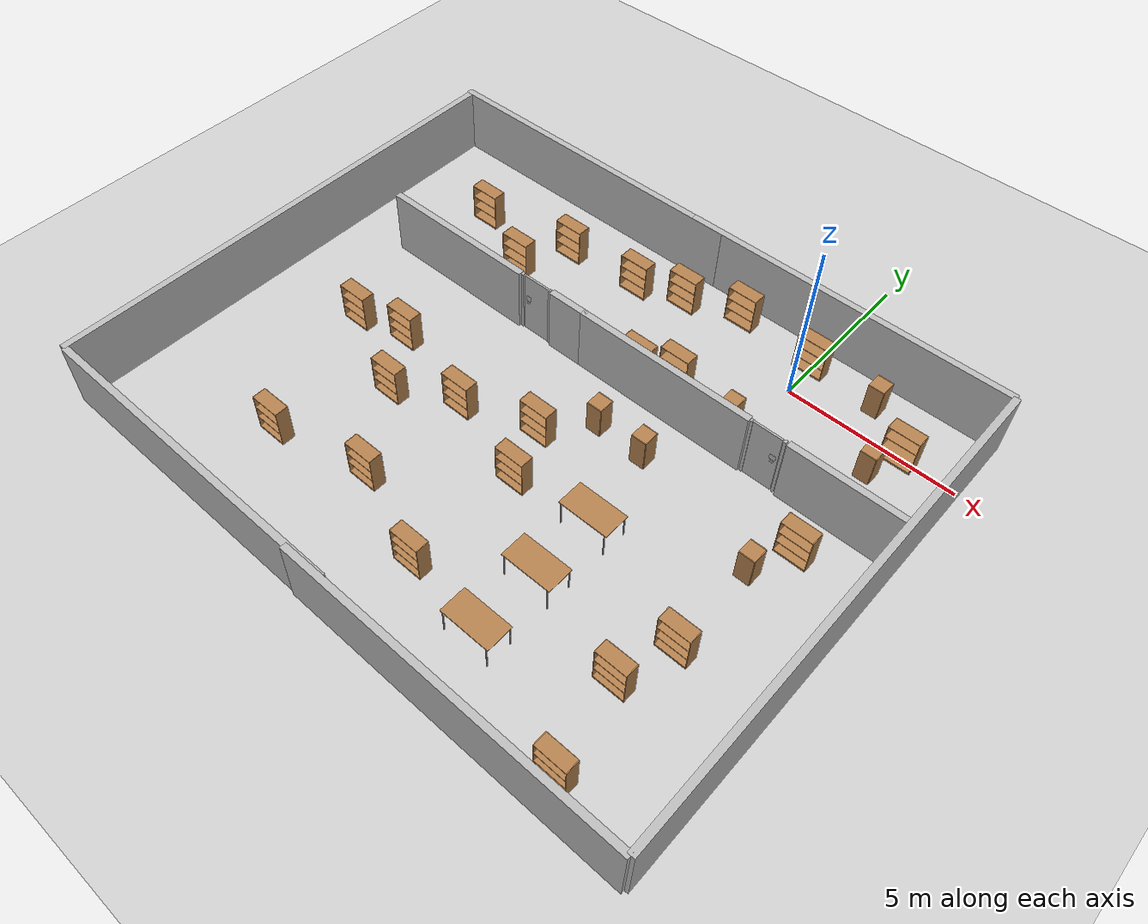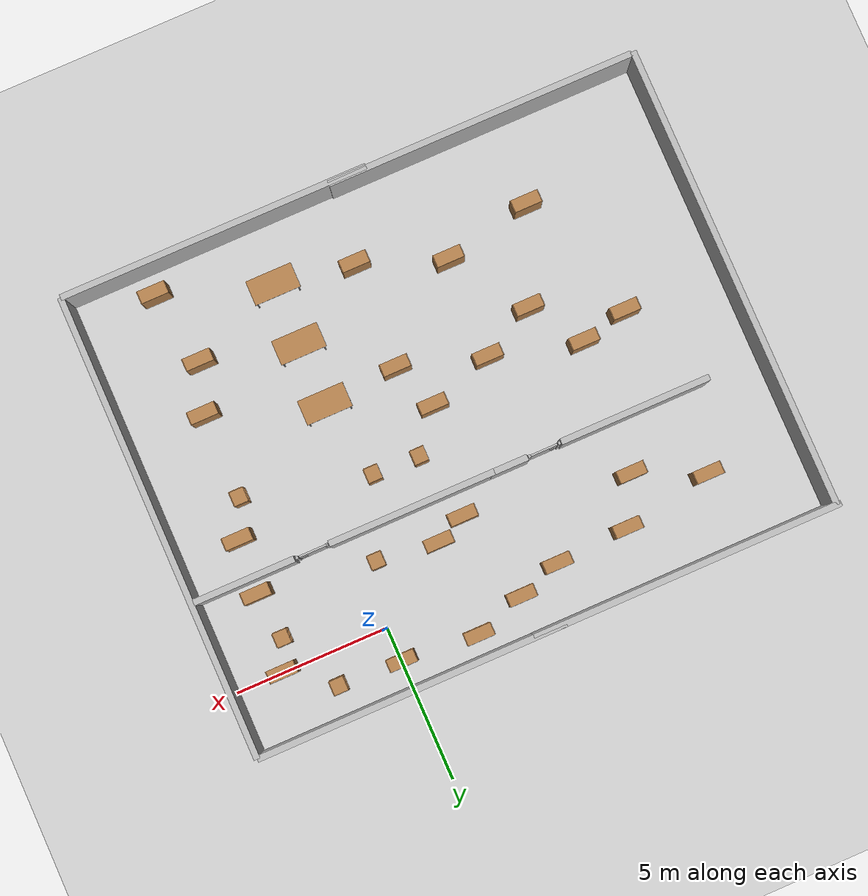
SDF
<sdf version='1.6'>
  <world name='default'>
    <physics name='default_physics' default='0' type='ode'>
      <ode>
        <solver>
          <type>quick</type>
          <iters>20</iters>
          <sor>1</sor>
          <use_dynamic_moi_rescaling>0</use_dynamic_moi_rescaling>
        </solver>
        <constraints>
          <cfm>0</cfm>
          <erp>0.2</erp>
          <contact_max_correcting_vel>100</contact_max_correcting_vel>
          <contact_surface_layer>0</contact_surface_layer>
        </constraints>
      </ode>
      <real_time_update_rate>1000</real_time_update_rate>
      <max_step_size>0.001</max_step_size>
      <real_time_factor>1</real_time_factor>
      <max_contacts>20</max_contacts>
    </physics>
    <light name='sun' type='directional'>
      <cast_shadows>1</cast_shadows>
      <pose frame=''>0 0 10 0 -0 0</pose>
      <diffuse>0.8 0.8 0.8 1</diffuse>
      <specular>0.2 0.2 0.2 1</specular>
      <attenuation>
        <range>1000</range>
        <constant>0.9</constant>
        <linear>0.01</linear>
        <quadratic>0.001</quadratic>
      </attenuation>
      <direction>0.5 0.1 -0.9</direction>
    </light>
    <model name='ground_plane'>
      <static>1</static>
      <link name='link'>
        <collision name='collision'>
          <geometry>
            <plane>
              <normal>0 0 1</normal>
              <size>100 100</size>
            </plane>
          </geometry>
          <surface>
            <friction>
              <ode>
                <mu>100</mu>
                <mu2>50</mu2>
              </ode>
              <torsional>
                <ode/>
              </torsional>
            </friction>
            <bounce/>
            <contact>
              <ode/>
            </contact>
          </surface>
          <max_contacts>10</max_contacts>
        </collision>
        <visual name='visual'>
          <cast_shadows>0</cast_shadows>
          <geometry>
            <plane>
              <normal>0 0 1</normal>
              <size>100 100</size>
            </plane>
          </geometry>
          <material>
            <script>
              <uri>file://media/materials/scripts/gazebo.material</uri>
              <name>Gazebo/Grey</name>
            </script>
          </material>
        </visual>
        <velocity_decay>
          <linear>0</linear>
          <angular>0</angular>
        </velocity_decay>
        <self_collide>0</self_collide>
        <kinematic>0</kinematic>
        <gravity>1</gravity>
        <enable_wind>0</enable_wind>
      </link>
    </model>
    <model name='wall_1_model'>
      <pose frame=''>0 -13 1 0 -0 0</pose>
      <static>1</static>
      <link name='wall_1_body'>
        <inertial>
          <mass>1</mass>
          <inertia>
            <ixx>1</ixx>
            <ixy>0</ixy>
            <ixz>0</ixz>
            <iyy>1</iyy>
            <iyz>0</iyz>
            <izz>1</izz>
          </inertia>
        </inertial>
        <collision name='collision'>
          <geometry>
            <box>
              <size>10 0.2 2</size>
            </box>
          </geometry>
          <max_contacts>10</max_contacts>
          <surface>
            <bounce/>
            <friction>
              <ode/>
              <torsional>
                <ode/>
              </torsional>
            </friction>
            <contact>
              <ode/>
            </contact>
          </surface>
        </collision>
        <visual name='visual'>
          <geometry>
            <box>
              <size>10 0.2 2</size>
            </box>
          </geometry>
        </visual>
        <velocity_decay>
          <linear>0</linear>
          <angular>0</angular>
        </velocity_decay>
        <self_collide>0</self_collide>
        <kinematic>0</kinematic>
        <gravity>1</gravity>
        <enable_wind>0</enable_wind>
      </link>
    </model>
    <model name='wall_2_model'>
      <pose frame=''>0 2 1 0 -0 0</pose>
      <static>1</static>
      <link name='wall_2_body'>
        <inertial>
          <mass>1</mass>
          <inertia>
            <ixx>1</ixx>
            <ixy>0</ixy>
            <ixz>0</ixz>
            <iyy>1</iyy>
            <iyz>0</iyz>
            <izz>1</izz>
          </inertia>
        </inertial>
        <collision name='collision'>
          <geometry>
            <box>
              <size>10 0.2 2</size>
            </box>
          </geometry>
          <max_contacts>10</max_contacts>
          <surface>
            <bounce/>
            <friction>
              <ode/>
              <torsional>
                <ode/>
              </torsional>
            </friction>
            <contact>
              <ode/>
            </contact>
          </surface>
        </collision>
        <visual name='visual'>
          <geometry>
            <box>
              <size>10 0.2 2</size>
            </box>
          </geometry>
        </visual>
        <velocity_decay>
          <linear>0</linear>
          <angular>0</angular>
        </velocity_decay>
        <self_collide>0</self_collide>
        <kinematic>0</kinematic>
        <gravity>1</gravity>
        <enable_wind>0</enable_wind>
      </link>
    </model>
    <model name='wall_3_model'>
      <pose frame=''>-13.8175 -5.49075 1 0 -0 0</pose>
      <static>1</static>
      <link name='wall_3_body'>
        <inertial>
          <mass>1</mass>
          <inertia>
            <ixx>1</ixx>
            <ixy>0</ixy>
            <ixz>0</ixz>
            <iyy>1</iyy>
            <iyz>0</iyz>
            <izz>1</izz>
          </inertia>
        </inertial>
        <collision name='collision'>
          <geometry>
            <box>
              <size>0.2 15 2</size>
            </box>
          </geometry>
          <max_contacts>10</max_contacts>
          <surface>
            <bounce/>
            <friction>
              <ode/>
              <torsional>
                <ode/>
              </torsional>
            </friction>
            <contact>
              <ode/>
            </contact>
          </surface>
        </collision>
        <visual name='visual'>
          <geometry>
            <box>
              <size>0.2 15 2</size>
            </box>
          </geometry>
        </visual>
        <velocity_decay>
          <linear>0</linear>
          <angular>0</angular>
        </velocity_decay>
        <self_collide>0</self_collide>
        <kinematic>0</kinematic>
        <gravity>1</gravity>
        <enable_wind>0</enable_wind>
      </link>
    </model>
    <model name='wall_4_model'>
      <pose frame=''>5 -5.5 1 0 -0 0</pose>
      <static>1</static>
      <link name='wall_4_body'>
        <inertial>
          <mass>1</mass>
          <inertia>
            <ixx>1</ixx>
            <ixy>0</ixy>
            <ixz>0</ixz>
            <iyy>1</iyy>
            <iyz>0</iyz>
            <izz>1</izz>
          </inertia>
        </inertial>
        <collision name='collision'>
          <geometry>
            <box>
              <size>0.2 15 2</size>
            </box>
          </geometry>
          <max_contacts>10</max_contacts>
          <surface>
            <bounce/>
            <friction>
              <ode/>
              <torsional>
                <ode/>
              </torsional>
            </friction>
            <contact>
              <ode/>
            </contact>
          </surface>
        </collision>
        <visual name='visual'>
          <geometry>
            <box>
              <size>0.2 15 2</size>
            </box>
          </geometry>
        </visual>
        <velocity_decay>
          <linear>0</linear>
          <angular>0</angular>
        </velocity_decay>
        <self_collide>0</self_collide>
        <kinematic>0</kinematic>
        <gravity>1</gravity>
        <enable_wind>0</enable_wind>
      </link>
    </model>
    <model name='wall_5_model'>
      <pose frame=''>-2.15636 -3 1 0 -0 0</pose>
      <static>1</static>
      <link name='wall_5_body'>
        <inertial>
          <mass>1</mass>
          <inertia>
            <ixx>1</ixx>
            <ixy>0</ixy>
            <ixz>0</ixz>
            <iyy>1</iyy>
            <iyz>0</iyz>
            <izz>1</izz>
          </inertia>
        </inertial>
        <collision name='collision'>
          <geometry>
            <box>
              <size>5.38601 0.2 2</size>
            </box>
          </geometry>
          <max_contacts>10</max_contacts>
          <surface>
            <bounce/>
            <friction>
              <ode/>
              <torsional>
                <ode/>
              </torsional>
            </friction>
            <contact>
              <ode/>
            </contact>
          </surface>
        </collision>
        <visual name='visual'>
          <geometry>
            <box>
              <size>5.38601 0.2 2</size>
            </box>
          </geometry>
        </visual>
        <velocity_decay>
          <linear>0</linear>
          <angular>0</angular>
        </velocity_decay>
        <self_collide>0</self_collide>
        <kinematic>0</kinematic>
        <gravity>1</gravity>
        <enable_wind>0</enable_wind>
      </link>
    </model>
    <model name='wall_6_model'>
      <pose frame=''>3.286786 -3.0 1.0 0 0 0</pose>
      <static>1</static>
      <link name='wall_6_body'>
        <inertial>
          <mass>1</mass>
          <inertia>
            <ixx>1</ixx>
            <ixy>0</ixy>
            <ixz>0</ixz>
            <iyy>1</iyy>
            <iyz>0</iyz>
            <izz>1</izz>
          </inertia>
        </inertial>
        <collision name='collision'>
          <geometry>
            <box>
              <size>3.27 0.2 2</size>
            </box>
          </geometry>
          <max_contacts>10</max_contacts>
          <surface>
            <bounce/>
            <friction>
              <ode/>
              <torsional>
                <ode/>
              </torsional>
            </friction>
            <contact>
              <ode/>
            </contact>
          </surface>
        </collision>
        <visual name='visual'>
          <geometry>
            <box>
              <size>3.27 0.2 2</size>
            </box>
          </geometry>
        </visual>
        <velocity_decay>
          <linear>0</linear>
          <angular>0</angular>
        </velocity_decay>
        <self_collide>0</self_collide>
        <kinematic>0</kinematic>
        <gravity>1</gravity>
        <enable_wind>0</enable_wind>
      </link>
    </model>
    <scene>
      <ambient>0.2 0.2 0.2 1</ambient>
      <background>0.7 0.7 0.7 1</background>
      <shadows>1</shadows>
    </scene>
    <model name='cabinet'>
      <static>0</static>
      <link name='cabinet_bottom_plate'>
        <inertial>
          <pose frame=''>0 0 -1 0 -0 0</pose>
          <inertia>
            <ixx>2.05</ixx>
            <ixy>0</ixy>
            <ixz>0</ixz>
            <iyy>2.05</iyy>
            <iyz>0</iyz>
            <izz>2.05</izz>
          </inertia>
          <mass>25</mass>
        </inertial>
        <collision name='cabinet_bottom_plate_geom'>
          <pose frame=''>0 0 0.01 0 -0 0</pose>
          <geometry>
            <box>
              <size>0.45 0.45 0.02</size>
            </box>
          </geometry>
          <surface>
            <bounce/>
            <friction>
              <ode/>
              <torsional>
                <ode/>
              </torsional>
            </friction>
            <contact>
              <ode/>
            </contact>
          </surface>
          <max_contacts>10</max_contacts>
        </collision>
        <visual name='cabinet_bottom_plate_geom_visual'>
          <pose frame=''>0 0 0.01 0 -0 0</pose>
          <geometry>
            <box>
              <size>0.45 0.45 0.02</size>
            </box>
          </geometry>
          <material>
            <script>
              <uri>file://media/materials/scripts/gazebo.material</uri>
              <name>Gazebo/Wood</name>
            </script>
          </material>
        </visual>
        <collision name='cabinet_bottom_plate_geom_cabinet_back_plate'>
          <pose frame=''>0.235 0 0.51 0 -0 0</pose>
          <geometry>
            <box>
              <size>0.02 0.45 1.02</size>
            </box>
          </geometry>
          <surface>
            <bounce/>
            <friction>
              <ode/>
              <torsional>
                <ode/>
              </torsional>
            </friction>
            <contact>
              <ode/>
            </contact>
          </surface>
          <max_contacts>10</max_contacts>
        </collision>
        <visual name='cabinet_bottom_plate_geom_cabinet_back_plate_visual'>
          <pose frame=''>0.235 0 0.51 0 -0 0</pose>
          <geometry>
            <box>
              <size>0.02 0.45 1.02</size>
            </box>
          </geometry>
          <material>
            <script>
              <uri>file://media/materials/scripts/gazebo.material</uri>
              <name>Gazebo/Wood</name>
            </script>
          </material>
        </visual>
        <collision name='cabinet_bottom_plate_geom_cabinet_left_plate'>
          <pose frame=''>0 0.235 0.51 0 -0 0</pose>
          <geometry>
            <box>
              <size>0.45 0.02 1.02</size>
            </box>
          </geometry>
          <surface>
            <bounce/>
            <friction>
              <ode/>
              <torsional>
                <ode/>
              </torsional>
            </friction>
            <contact>
              <ode/>
            </contact>
          </surface>
          <max_contacts>10</max_contacts>
        </collision>
        <visual name='cabinet_bottom_plate_geom_cabinet_left_plate_visual'>
          <pose frame=''>0 0.235 0.51 0 -0 0</pose>
          <geometry>
            <box>
              <size>0.45 0.02 1.02</size>
            </box>
          </geometry>
          <material>
            <script>
              <uri>file://media/materials/scripts/gazebo.material</uri>
              <name>Gazebo/Wood</name>
            </script>
          </material>
        </visual>
        <collision name='cabinet_bottom_plate_geom_cabinet_middle_plate'>
          <pose frame=''>0 0 0.51 0 -0 0</pose>
          <geometry>
            <box>
              <size>0.45 0.45 0.02</size>
            </box>
          </geometry>
          <surface>
            <bounce/>
            <friction>
              <ode/>
              <torsional>
                <ode/>
              </torsional>
            </friction>
            <contact>
              <ode/>
            </contact>
          </surface>
          <max_contacts>10</max_contacts>
        </collision>
        <visual name='cabinet_bottom_plate_geom_cabinet_middle_plate_visual'>
          <pose frame=''>0 0 0.51 0 -0 0</pose>
          <geometry>
            <box>
              <size>0.45 0.45 0.02</size>
            </box>
          </geometry>
          <material>
            <script>
              <uri>file://media/materials/scripts/gazebo.material</uri>
              <name>Gazebo/Wood</name>
            </script>
          </material>
        </visual>
        <collision name='cabinet_bottom_plate_geom_cabinet_right_plate'>
          <pose frame=''>0 -0.235 0.51 0 -0 0</pose>
          <geometry>
            <box>
              <size>0.45 0.02 1.02</size>
            </box>
          </geometry>
          <surface>
            <bounce/>
            <friction>
              <ode/>
              <torsional>
                <ode/>
              </torsional>
            </friction>
            <contact>
              <ode/>
            </contact>
          </surface>
          <max_contacts>10</max_contacts>
        </collision>
        <visual name='cabinet_bottom_plate_geom_cabinet_right_plate_visual'>
          <pose frame=''>0 -0.235 0.51 0 -0 0</pose>
          <geometry>
            <box>
              <size>0.45 0.02 1.02</size>
            </box>
          </geometry>
          <material>
            <script>
              <uri>file://media/materials/scripts/gazebo.material</uri>
              <name>Gazebo/Wood</name>
            </script>
          </material>
        </visual>
        <collision name='cabinet_bottom_plate_geom_cabinet_top_plate'>
          <pose frame=''>0 0 1.01 0 -0 0</pose>
          <geometry>
            <box>
              <size>0.45 0.45 0.02</size>
            </box>
          </geometry>
          <surface>
            <bounce/>
            <friction>
              <ode/>
              <torsional>
                <ode/>
              </torsional>
            </friction>
            <contact>
              <ode/>
            </contact>
          </surface>
          <max_contacts>10</max_contacts>
        </collision>
        <visual name='cabinet_bottom_plate_geom_cabinet_top_plate_visual'>
          <pose frame=''>0 0 1.01 0 -0 0</pose>
          <geometry>
            <box>
              <size>0.45 0.45 0.02</size>
            </box>
          </geometry>
          <material>
            <script>
              <uri>file://media/materials/scripts/gazebo.material</uri>
              <name>Gazebo/Wood</name>
            </script>
          </material>
        </visual>
        <velocity_decay>
          <linear>0</linear>
          <angular>0</angular>
        </velocity_decay>
        <self_collide>0</self_collide>
        <kinematic>0</kinematic>
        <gravity>1</gravity>
        <enable_wind>0</enable_wind>
      </link>
      <pose frame=''>2 1 0 0 -0 0</pose>
    </model>
    <model name='cabinet_0'>
      <static>0</static>
      <link name='cabinet_bottom_plate'>
        <inertial>
          <pose frame=''>0 0 -1 0 -0 0</pose>
          <inertia>
            <ixx>2.05</ixx>
            <ixy>0</ixy>
            <ixz>0</ixz>
            <iyy>2.05</iyy>
            <iyz>0</iyz>
            <izz>2.05</izz>
          </inertia>
          <mass>25</mass>
        </inertial>
        <collision name='cabinet_bottom_plate_geom'>
          <pose frame=''>0 0 0.01 0 -0 0</pose>
          <geometry>
            <box>
              <size>0.45 0.45 0.02</size>
            </box>
          </geometry>
          <surface>
            <bounce/>
            <friction>
              <ode/>
              <torsional>
                <ode/>
              </torsional>
            </friction>
            <contact>
              <ode/>
            </contact>
          </surface>
          <max_contacts>10</max_contacts>
        </collision>
        <visual name='cabinet_bottom_plate_geom_visual'>
          <pose frame=''>0 0 0.01 0 -0 0</pose>
          <geometry>
            <box>
              <size>0.45 0.45 0.02</size>
            </box>
          </geometry>
          <material>
            <script>
              <uri>file://media/materials/scripts/gazebo.material</uri>
              <name>Gazebo/Wood</name>
            </script>
          </material>
        </visual>
        <collision name='cabinet_bottom_plate_geom_cabinet_back_plate'>
          <pose frame=''>0.235 0 0.51 0 -0 0</pose>
          <geometry>
            <box>
              <size>0.02 0.45 1.02</size>
            </box>
          </geometry>
          <surface>
            <bounce/>
            <friction>
              <ode/>
              <torsional>
                <ode/>
              </torsional>
            </friction>
            <contact>
              <ode/>
            </contact>
          </surface>
          <max_contacts>10</max_contacts>
        </collision>
        <visual name='cabinet_bottom_plate_geom_cabinet_back_plate_visual'>
          <pose frame=''>0.235 0 0.51 0 -0 0</pose>
          <geometry>
            <box>
              <size>0.02 0.45 1.02</size>
            </box>
          </geometry>
          <material>
            <script>
              <uri>file://media/materials/scripts/gazebo.material</uri>
              <name>Gazebo/Wood</name>
            </script>
          </material>
        </visual>
        <collision name='cabinet_bottom_plate_geom_cabinet_left_plate'>
          <pose frame=''>0 0.235 0.51 0 -0 0</pose>
          <geometry>
            <box>
              <size>0.45 0.02 1.02</size>
            </box>
          </geometry>
          <surface>
            <bounce/>
            <friction>
              <ode/>
              <torsional>
                <ode/>
              </torsional>
            </friction>
            <contact>
              <ode/>
            </contact>
          </surface>
          <max_contacts>10</max_contacts>
        </collision>
        <visual name='cabinet_bottom_plate_geom_cabinet_left_plate_visual'>
          <pose frame=''>0 0.235 0.51 0 -0 0</pose>
          <geometry>
            <box>
              <size>0.45 0.02 1.02</size>
            </box>
          </geometry>
          <material>
            <script>
              <uri>file://media/materials/scripts/gazebo.material</uri>
              <name>Gazebo/Wood</name>
            </script>
          </material>
        </visual>
        <collision name='cabinet_bottom_plate_geom_cabinet_middle_plate'>
          <pose frame=''>0 0 0.51 0 -0 0</pose>
          <geometry>
            <box>
              <size>0.45 0.45 0.02</size>
            </box>
          </geometry>
          <surface>
            <bounce/>
            <friction>
              <ode/>
              <torsional>
                <ode/>
              </torsional>
            </friction>
            <contact>
              <ode/>
            </contact>
          </surface>
          <max_contacts>10</max_contacts>
        </collision>
        <visual name='cabinet_bottom_plate_geom_cabinet_middle_plate_visual'>
          <pose frame=''>0 0 0.51 0 -0 0</pose>
          <geometry>
            <box>
              <size>0.45 0.45 0.02</size>
            </box>
          </geometry>
          <material>
            <script>
              <uri>file://media/materials/scripts/gazebo.material</uri>
              <name>Gazebo/Wood</name>
            </script>
          </material>
        </visual>
        <collision name='cabinet_bottom_plate_geom_cabinet_right_plate'>
          <pose frame=''>0 -0.235 0.51 0 -0 0</pose>
          <geometry>
            <box>
              <size>0.45 0.02 1.02</size>
            </box>
          </geometry>
          <surface>
            <bounce/>
            <friction>
              <ode/>
              <torsional>
                <ode/>
              </torsional>
            </friction>
            <contact>
              <ode/>
            </contact>
          </surface>
          <max_contacts>10</max_contacts>
        </collision>
        <visual name='cabinet_bottom_plate_geom_cabinet_right_plate_visual'>
          <pose frame=''>0 -0.235 0.51 0 -0 0</pose>
          <geometry>
            <box>
              <size>0.45 0.02 1.02</size>
            </box>
          </geometry>
          <material>
            <script>
              <uri>file://media/materials/scripts/gazebo.material</uri>
              <name>Gazebo/Wood</name>
            </script>
          </material>
        </visual>
        <collision name='cabinet_bottom_plate_geom_cabinet_top_plate'>
          <pose frame=''>0 0 1.01 0 -0 0</pose>
          <geometry>
            <box>
              <size>0.45 0.45 0.02</size>
            </box>
          </geometry>
          <surface>
            <bounce/>
            <friction>
              <ode/>
              <torsional>
                <ode/>
              </torsional>
            </friction>
            <contact>
              <ode/>
            </contact>
          </surface>
          <max_contacts>10</max_contacts>
        </collision>
        <visual name='cabinet_bottom_plate_geom_cabinet_top_plate_visual'>
          <pose frame=''>0 0 1.01 0 -0 0</pose>
          <geometry>
            <box>
              <size>0.45 0.45 0.02</size>
            </box>
          </geometry>
          <material>
            <script>
              <uri>file://media/materials/scripts/gazebo.material</uri>
              <name>Gazebo/Wood</name>
            </script>
          </material>
        </visual>
        <velocity_decay>
          <linear>0</linear>
          <angular>0</angular>
        </velocity_decay>
        <self_collide>0</self_collide>
        <kinematic>0</kinematic>
        <gravity>1</gravity>
        <enable_wind>0</enable_wind>
      </link>
      <pose frame=''>2.51573 -5.43949 0 0 -0 0</pose>
    </model>
    <model name='bookshelf'>
      <static>0</static>
      <link name='link'>
        <inertial>
          <mass>1</mass>
          <inertia>
            <ixx>1</ixx>
            <ixy>0</ixy>
            <ixz>0</ixz>
            <iyy>1</iyy>
            <iyz>0</iyz>
            <izz>1</izz>
          </inertia>
        </inertial>
        <collision name='back'>
          <pose frame=''>0 0.005 0.6 0 -0 0</pose>
          <geometry>
            <box>
              <size>0.9 0.01 1.2</size>
            </box>
          </geometry>
          <surface>
            <bounce/>
            <friction>
              <ode/>
              <torsional>
                <ode/>
              </torsional>
            </friction>
            <contact>
              <ode/>
            </contact>
          </surface>
          <max_contacts>10</max_contacts>
        </collision>
        <visual name='visual1'>
          <pose frame=''>0 0.005 0.6 0 -0 0</pose>
          <geometry>
            <box>
              <size>0.9 0.01 1.2</size>
            </box>
          </geometry>
          <material>
            <script>
              <uri>file://media/materials/scripts/gazebo.material</uri>
              <name>Gazebo/Wood</name>
            </script>
          </material>
        </visual>
        <collision name='left_side'>
          <pose frame=''>0.45 -0.195 0.6 0 -0 0</pose>
          <geometry>
            <box>
              <size>0.02 0.4 1.2</size>
            </box>
          </geometry>
          <surface>
            <bounce/>
            <friction>
              <ode/>
              <torsional>
                <ode/>
              </torsional>
            </friction>
            <contact>
              <ode/>
            </contact>
          </surface>
          <max_contacts>10</max_contacts>
        </collision>
        <visual name='visual2'>
          <pose frame=''>0.45 -0.195 0.6 0 -0 0</pose>
          <geometry>
            <box>
              <size>0.02 0.4 1.2</size>
            </box>
          </geometry>
          <material>
            <script>
              <uri>file://media/materials/scripts/gazebo.material</uri>
              <name>Gazebo/Wood</name>
            </script>
          </material>
        </visual>
        <collision name='right_side'>
          <pose frame=''>-0.45 -0.195 0.6 0 -0 0</pose>
          <geometry>
            <box>
              <size>0.02 0.4 1.2</size>
            </box>
          </geometry>
          <surface>
            <bounce/>
            <friction>
              <ode/>
              <torsional>
                <ode/>
              </torsional>
            </friction>
            <contact>
              <ode/>
            </contact>
          </surface>
          <max_contacts>10</max_contacts>
        </collision>
        <visual name='visual3'>
          <pose frame=''>-0.45 -0.195 0.6 0 -0 0</pose>
          <geometry>
            <box>
              <size>0.02 0.4 1.2</size>
            </box>
          </geometry>
          <material>
            <script>
              <uri>file://media/materials/scripts/gazebo.material</uri>
              <name>Gazebo/Wood</name>
            </script>
          </material>
        </visual>
        <collision name='bottom'>
          <pose frame=''>0 -0.195 0.03 0 -0 0</pose>
          <geometry>
            <box>
              <size>0.88 0.4 0.06</size>
            </box>
          </geometry>
          <surface>
            <bounce/>
            <friction>
              <ode/>
              <torsional>
                <ode/>
              </torsional>
            </friction>
            <contact>
              <ode/>
            </contact>
          </surface>
          <max_contacts>10</max_contacts>
        </collision>
        <visual name='visual4'>
          <pose frame=''>0 -0.195 0.03 0 -0 0</pose>
          <geometry>
            <box>
              <size>0.88 0.4 0.06</size>
            </box>
          </geometry>
          <material>
            <script>
              <uri>file://media/materials/scripts/gazebo.material</uri>
              <name>Gazebo/Wood</name>
            </script>
          </material>
        </visual>
        <collision name='top'>
          <pose frame=''>0 -0.195 1.19 0 -0 0</pose>
          <geometry>
            <box>
              <size>0.88 0.4 0.02</size>
            </box>
          </geometry>
          <surface>
            <bounce/>
            <friction>
              <ode/>
              <torsional>
                <ode/>
              </torsional>
            </friction>
            <contact>
              <ode/>
            </contact>
          </surface>
          <max_contacts>10</max_contacts>
        </collision>
        <visual name='visual5'>
          <pose frame=''>0 -0.195 1.19 0 -0 0</pose>
          <geometry>
            <box>
              <size>0.88 0.4 0.02</size>
            </box>
          </geometry>
          <material>
            <script>
              <uri>file://media/materials/scripts/gazebo.material</uri>
              <name>Gazebo/Wood</name>
            </script>
          </material>
        </visual>
        <collision name='low_shelf'>
          <pose frame=''>0 -0.195 0.43 0 -0 0</pose>
          <geometry>
            <box>
              <size>0.88 0.4 0.02</size>
            </box>
          </geometry>
          <surface>
            <bounce/>
            <friction>
              <ode/>
              <torsional>
                <ode/>
              </torsional>
            </friction>
            <contact>
              <ode/>
            </contact>
          </surface>
          <max_contacts>10</max_contacts>
        </collision>
        <visual name='visual6'>
          <pose frame=''>0 -0.195 0.43 0 -0 0</pose>
          <geometry>
            <box>
              <size>0.88 0.4 0.02</size>
            </box>
          </geometry>
          <material>
            <script>
              <uri>file://media/materials/scripts/gazebo.material</uri>
              <name>Gazebo/Wood</name>
            </script>
          </material>
        </visual>
        <collision name='high_shelf'>
          <pose frame=''>0 -0.195 0.8 0 -0 0</pose>
          <geometry>
            <box>
              <size>0.88 0.4 0.02</size>
            </box>
          </geometry>
          <surface>
            <bounce/>
            <friction>
              <ode/>
              <torsional>
                <ode/>
              </torsional>
            </friction>
            <contact>
              <ode/>
            </contact>
          </surface>
          <max_contacts>10</max_contacts>
        </collision>
        <visual name='visual7'>
          <pose frame=''>0 -0.195 0.8 0 -0 0</pose>
          <geometry>
            <box>
              <size>0.88 0.4 0.02</size>
            </box>
          </geometry>
          <material>
            <script>
              <uri>file://media/materials/scripts/gazebo.material</uri>
              <name>Gazebo/Wood</name>
            </script>
          </material>
        </visual>
        <velocity_decay>
          <linear>0</linear>
          <angular>0</angular>
        </velocity_decay>
        <self_collide>0</self_collide>
        <kinematic>0</kinematic>
        <gravity>1</gravity>
        <enable_wind>0</enable_wind>
      </link>
      <pose frame=''>2 -9.55401 0 0 -0 0</pose>
    </model>
    <model name='bookshelf_0'>
      <static>0</static>
      <link name='link'>
        <inertial>
          <mass>1</mass>
          <inertia>
            <ixx>1</ixx>
            <ixy>0</ixy>
            <ixz>0</ixz>
            <iyy>1</iyy>
            <iyz>0</iyz>
            <izz>1</izz>
          </inertia>
        </inertial>
        <collision name='back'>
          <pose frame=''>0 0.005 0.6 0 -0 0</pose>
          <geometry>
            <box>
              <size>0.9 0.01 1.2</size>
            </box>
          </geometry>
          <surface>
            <bounce/>
            <friction>
              <ode/>
              <torsional>
                <ode/>
              </torsional>
            </friction>
            <contact>
              <ode/>
            </contact>
          </surface>
          <max_contacts>10</max_contacts>
        </collision>
        <visual name='visual1'>
          <pose frame=''>0 0.005 0.6 0 -0 0</pose>
          <geometry>
            <box>
              <size>0.9 0.01 1.2</size>
            </box>
          </geometry>
          <material>
            <script>
              <uri>file://media/materials/scripts/gazebo.material</uri>
              <name>Gazebo/Wood</name>
            </script>
          </material>
        </visual>
        <collision name='left_side'>
          <pose frame=''>0.45 -0.195 0.6 0 -0 0</pose>
          <geometry>
            <box>
              <size>0.02 0.4 1.2</size>
            </box>
          </geometry>
          <surface>
            <bounce/>
            <friction>
              <ode/>
              <torsional>
                <ode/>
              </torsional>
            </friction>
            <contact>
              <ode/>
            </contact>
          </surface>
          <max_contacts>10</max_contacts>
        </collision>
        <visual name='visual2'>
          <pose frame=''>0.45 -0.195 0.6 0 -0 0</pose>
          <geometry>
            <box>
              <size>0.02 0.4 1.2</size>
            </box>
          </geometry>
          <material>
            <script>
              <uri>file://media/materials/scripts/gazebo.material</uri>
              <name>Gazebo/Wood</name>
            </script>
          </material>
        </visual>
        <collision name='right_side'>
          <pose frame=''>-0.45 -0.195 0.6 0 -0 0</pose>
          <geometry>
            <box>
              <size>0.02 0.4 1.2</size>
            </box>
          </geometry>
          <surface>
            <bounce/>
            <friction>
              <ode/>
              <torsional>
                <ode/>
              </torsional>
            </friction>
            <contact>
              <ode/>
            </contact>
          </surface>
          <max_contacts>10</max_contacts>
        </collision>
        <visual name='visual3'>
          <pose frame=''>-0.45 -0.195 0.6 0 -0 0</pose>
          <geometry>
            <box>
              <size>0.02 0.4 1.2</size>
            </box>
          </geometry>
          <material>
            <script>
              <uri>file://media/materials/scripts/gazebo.material</uri>
              <name>Gazebo/Wood</name>
            </script>
          </material>
        </visual>
        <collision name='bottom'>
          <pose frame=''>0 -0.195 0.03 0 -0 0</pose>
          <geometry>
            <box>
              <size>0.88 0.4 0.06</size>
            </box>
          </geometry>
          <surface>
            <bounce/>
            <friction>
              <ode/>
              <torsional>
                <ode/>
              </torsional>
            </friction>
            <contact>
              <ode/>
            </contact>
          </surface>
          <max_contacts>10</max_contacts>
        </collision>
        <visual name='visual4'>
          <pose frame=''>0 -0.195 0.03 0 -0 0</pose>
          <geometry>
            <box>
              <size>0.88 0.4 0.06</size>
            </box>
          </geometry>
          <material>
            <script>
              <uri>file://media/materials/scripts/gazebo.material</uri>
              <name>Gazebo/Wood</name>
            </script>
          </material>
        </visual>
        <collision name='top'>
          <pose frame=''>0 -0.195 1.19 0 -0 0</pose>
          <geometry>
            <box>
              <size>0.88 0.4 0.02</size>
            </box>
          </geometry>
          <surface>
            <bounce/>
            <friction>
              <ode/>
              <torsional>
                <ode/>
              </torsional>
            </friction>
            <contact>
              <ode/>
            </contact>
          </surface>
          <max_contacts>10</max_contacts>
        </collision>
        <visual name='visual5'>
          <pose frame=''>0 -0.195 1.19 0 -0 0</pose>
          <geometry>
            <box>
              <size>0.88 0.4 0.02</size>
            </box>
          </geometry>
          <material>
            <script>
              <uri>file://media/materials/scripts/gazebo.material</uri>
              <name>Gazebo/Wood</name>
            </script>
          </material>
        </visual>
        <collision name='low_shelf'>
          <pose frame=''>0 -0.195 0.43 0 -0 0</pose>
          <geometry>
            <box>
              <size>0.88 0.4 0.02</size>
            </box>
          </geometry>
          <surface>
            <bounce/>
            <friction>
              <ode/>
              <torsional>
                <ode/>
              </torsional>
            </friction>
            <contact>
              <ode/>
            </contact>
          </surface>
          <max_contacts>10</max_contacts>
        </collision>
        <visual name='visual6'>
          <pose frame=''>0 -0.195 0.43 0 -0 0</pose>
          <geometry>
            <box>
              <size>0.88 0.4 0.02</size>
            </box>
          </geometry>
          <material>
            <script>
              <uri>file://media/materials/scripts/gazebo.material</uri>
              <name>Gazebo/Wood</name>
            </script>
          </material>
        </visual>
        <collision name='high_shelf'>
          <pose frame=''>0 -0.195 0.8 0 -0 0</pose>
          <geometry>
            <box>
              <size>0.88 0.4 0.02</size>
            </box>
          </geometry>
          <surface>
            <bounce/>
            <friction>
              <ode/>
              <torsional>
                <ode/>
              </torsional>
            </friction>
            <contact>
              <ode/>
            </contact>
          </surface>
          <max_contacts>10</max_contacts>
        </collision>
        <visual name='visual7'>
          <pose frame=''>0 -0.195 0.8 0 -0 0</pose>
          <geometry>
            <box>
              <size>0.88 0.4 0.02</size>
            </box>
          </geometry>
          <material>
            <script>
              <uri>file://media/materials/scripts/gazebo.material</uri>
              <name>Gazebo/Wood</name>
            </script>
          </material>
        </visual>
        <velocity_decay>
          <linear>0</linear>
          <angular>0</angular>
        </velocity_decay>
        <self_collide>0</self_collide>
        <kinematic>0</kinematic>
        <gravity>1</gravity>
        <enable_wind>0</enable_wind>
      </link>
      <pose frame=''>-2.49657 -1.57894 0 0 -0 0</pose>
    </model>
    <model name='bookshelf_1'>
      <static>0</static>
      <link name='link'>
        <inertial>
          <mass>1</mass>
          <inertia>
            <ixx>1</ixx>
            <ixy>0</ixy>
            <ixz>0</ixz>
            <iyy>1</iyy>
            <iyz>0</iyz>
            <izz>1</izz>
          </inertia>
        </inertial>
        <collision name='back'>
          <pose frame=''>0 0.005 0.6 0 -0 0</pose>
          <geometry>
            <box>
              <size>0.9 0.01 1.2</size>
            </box>
          </geometry>
          <surface>
            <bounce/>
            <friction>
              <ode/>
              <torsional>
                <ode/>
              </torsional>
            </friction>
            <contact>
              <ode/>
            </contact>
          </surface>
          <max_contacts>10</max_contacts>
        </collision>
        <visual name='visual1'>
          <pose frame=''>0 0.005 0.6 0 -0 0</pose>
          <geometry>
            <box>
              <size>0.9 0.01 1.2</size>
            </box>
          </geometry>
          <material>
            <script>
              <uri>file://media/materials/scripts/gazebo.material</uri>
              <name>Gazebo/Wood</name>
            </script>
          </material>
        </visual>
        <collision name='left_side'>
          <pose frame=''>0.45 -0.195 0.6 0 -0 0</pose>
          <geometry>
            <box>
              <size>0.02 0.4 1.2</size>
            </box>
          </geometry>
          <surface>
            <bounce/>
            <friction>
              <ode/>
              <torsional>
                <ode/>
              </torsional>
            </friction>
            <contact>
              <ode/>
            </contact>
          </surface>
          <max_contacts>10</max_contacts>
        </collision>
        <visual name='visual2'>
          <pose frame=''>0.45 -0.195 0.6 0 -0 0</pose>
          <geometry>
            <box>
              <size>0.02 0.4 1.2</size>
            </box>
          </geometry>
          <material>
            <script>
              <uri>file://media/materials/scripts/gazebo.material</uri>
              <name>Gazebo/Wood</name>
            </script>
          </material>
        </visual>
        <collision name='right_side'>
          <pose frame=''>-0.45 -0.195 0.6 0 -0 0</pose>
          <geometry>
            <box>
              <size>0.02 0.4 1.2</size>
            </box>
          </geometry>
          <surface>
            <bounce/>
            <friction>
              <ode/>
              <torsional>
                <ode/>
              </torsional>
            </friction>
            <contact>
              <ode/>
            </contact>
          </surface>
          <max_contacts>10</max_contacts>
        </collision>
        <visual name='visual3'>
          <pose frame=''>-0.45 -0.195 0.6 0 -0 0</pose>
          <geometry>
            <box>
              <size>0.02 0.4 1.2</size>
            </box>
          </geometry>
          <material>
            <script>
              <uri>file://media/materials/scripts/gazebo.material</uri>
              <name>Gazebo/Wood</name>
            </script>
          </material>
        </visual>
        <collision name='bottom'>
          <pose frame=''>0 -0.195 0.03 0 -0 0</pose>
          <geometry>
            <box>
              <size>0.88 0.4 0.06</size>
            </box>
          </geometry>
          <surface>
            <bounce/>
            <friction>
              <ode/>
              <torsional>
                <ode/>
              </torsional>
            </friction>
            <contact>
              <ode/>
            </contact>
          </surface>
          <max_contacts>10</max_contacts>
        </collision>
        <visual name='visual4'>
          <pose frame=''>0 -0.195 0.03 0 -0 0</pose>
          <geometry>
            <box>
              <size>0.88 0.4 0.06</size>
            </box>
          </geometry>
          <material>
            <script>
              <uri>file://media/materials/scripts/gazebo.material</uri>
              <name>Gazebo/Wood</name>
            </script>
          </material>
        </visual>
        <collision name='top'>
          <pose frame=''>0 -0.195 1.19 0 -0 0</pose>
          <geometry>
            <box>
              <size>0.88 0.4 0.02</size>
            </box>
          </geometry>
          <surface>
            <bounce/>
            <friction>
              <ode/>
              <torsional>
                <ode/>
              </torsional>
            </friction>
            <contact>
              <ode/>
            </contact>
          </surface>
          <max_contacts>10</max_contacts>
        </collision>
        <visual name='visual5'>
          <pose frame=''>0 -0.195 1.19 0 -0 0</pose>
          <geometry>
            <box>
              <size>0.88 0.4 0.02</size>
            </box>
          </geometry>
          <material>
            <script>
              <uri>file://media/materials/scripts/gazebo.material</uri>
              <name>Gazebo/Wood</name>
            </script>
          </material>
        </visual>
        <collision name='low_shelf'>
          <pose frame=''>0 -0.195 0.43 0 -0 0</pose>
          <geometry>
            <box>
              <size>0.88 0.4 0.02</size>
            </box>
          </geometry>
          <surface>
            <bounce/>
            <friction>
              <ode/>
              <torsional>
                <ode/>
              </torsional>
            </friction>
            <contact>
              <ode/>
            </contact>
          </surface>
          <max_contacts>10</max_contacts>
        </collision>
        <visual name='visual6'>
          <pose frame=''>0 -0.195 0.43 0 -0 0</pose>
          <geometry>
            <box>
              <size>0.88 0.4 0.02</size>
            </box>
          </geometry>
          <material>
            <script>
              <uri>file://media/materials/scripts/gazebo.material</uri>
              <name>Gazebo/Wood</name>
            </script>
          </material>
        </visual>
        <collision name='high_shelf'>
          <pose frame=''>0 -0.195 0.8 0 -0 0</pose>
          <geometry>
            <box>
              <size>0.88 0.4 0.02</size>
            </box>
          </geometry>
          <surface>
            <bounce/>
            <friction>
              <ode/>
              <torsional>
                <ode/>
              </torsional>
            </friction>
            <contact>
              <ode/>
            </contact>
          </surface>
          <max_contacts>10</max_contacts>
        </collision>
        <visual name='visual7'>
          <pose frame=''>0 -0.195 0.8 0 -0 0</pose>
          <geometry>
            <box>
              <size>0.88 0.4 0.02</size>
            </box>
          </geometry>
          <material>
            <script>
              <uri>file://media/materials/scripts/gazebo.material</uri>
              <name>Gazebo/Wood</name>
            </script>
          </material>
        </visual>
        <velocity_decay>
          <linear>0</linear>
          <angular>0</angular>
        </velocity_decay>
        <self_collide>0</self_collide>
        <kinematic>0</kinematic>
        <gravity>1</gravity>
        <enable_wind>0</enable_wind>
      </link>
      <pose frame=''>-2.49816 1.46785 0 0 -0 0</pose>
    </model>
    <model name='table'>
      <static>0</static>
      <link name='link'>
        <collision name='surface'>
          <pose frame=''>0 0 0.9 0 -0 0</pose>
          <geometry>
            <box>
              <size>1.5 0.8 0.03</size>
            </box>
          </geometry>
          <surface>
            <bounce/>
            <friction>
              <ode/>
              <torsional>
                <ode/>
              </torsional>
            </friction>
            <contact>
              <ode/>
            </contact>
          </surface>
          <max_contacts>10</max_contacts>
        </collision>
        <visual name='visual1'>
          <pose frame=''>0 0 0.9 0 -0 0</pose>
          <geometry>
            <box>
              <size>1.5 0.8 0.03</size>
            </box>
          </geometry>
          <material>
            <script>
              <uri>file://media/materials/scripts/gazebo.material</uri>
              <name>Gazebo/Wood</name>
            </script>
          </material>
        </visual>
        <collision name='front_left_leg'>
          <pose frame=''>0.68 0.38 0.5 0 -0 0</pose>
          <geometry>
            <cylinder>
              <radius>0.02</radius>
              <length>0.8</length>
            </cylinder>
          </geometry>
          <surface>
            <bounce/>
            <friction>
              <ode/>
              <torsional>
                <ode/>
              </torsional>
            </friction>
            <contact>
              <ode/>
            </contact>
          </surface>
          <max_contacts>10</max_contacts>
        </collision>
        <visual name='front_left_leg'>
          <pose frame=''>0.68 0.38 0.5 0 -0 0</pose>
          <geometry>
            <cylinder>
              <radius>0.02</radius>
              <length>0.8</length>
            </cylinder>
          </geometry>
          <material>
            <script>
              <uri>file://media/materials/scripts/gazebo.material</uri>
              <name>Gazebo/Grey</name>
            </script>
          </material>
        </visual>
        <collision name='front_right_leg'>
          <pose frame=''>0.68 -0.38 0.5 0 -0 0</pose>
          <geometry>
            <cylinder>
              <radius>0.02</radius>
              <length>0.8</length>
            </cylinder>
          </geometry>
          <surface>
            <bounce/>
            <friction>
              <ode/>
              <torsional>
                <ode/>
              </torsional>
            </friction>
            <contact>
              <ode/>
            </contact>
          </surface>
          <max_contacts>10</max_contacts>
        </collision>
        <visual name='front_right_leg'>
          <pose frame=''>0.68 -0.38 0.5 0 -0 0</pose>
          <geometry>
            <cylinder>
              <radius>0.02</radius>
              <length>0.8</length>
            </cylinder>
          </geometry>
          <material>
            <script>
              <uri>file://media/materials/scripts/gazebo.material</uri>
              <name>Gazebo/Grey</name>
            </script>
          </material>
        </visual>
        <collision name='back_right_leg'>
          <pose frame=''>-0.68 -0.38 0.5 0 -0 0</pose>
          <geometry>
            <cylinder>
              <radius>0.02</radius>
              <length>0.8</length>
            </cylinder>
          </geometry>
          <surface>
            <bounce/>
            <friction>
              <ode/>
              <torsional>
                <ode/>
              </torsional>
            </friction>
            <contact>
              <ode/>
            </contact>
          </surface>
          <max_contacts>10</max_contacts>
        </collision>
        <visual name='back_right_leg'>
          <pose frame=''>-0.68 -0.38 0.5 0 -0 0</pose>
          <geometry>
            <cylinder>
              <radius>0.02</radius>
              <length>0.8</length>
            </cylinder>
          </geometry>
          <material>
            <script>
              <uri>file://media/materials/scripts/gazebo.material</uri>
              <name>Gazebo/Grey</name>
            </script>
          </material>
        </visual>
        <collision name='back_left_leg'>
          <pose frame=''>-0.68 0.38 0.5 0 -0 0</pose>
          <geometry>
            <cylinder>
              <radius>0.02</radius>
              <length>0.8</length>
            </cylinder>
          </geometry>
          <surface>
            <bounce/>
            <friction>
              <ode/>
              <torsional>
                <ode/>
              </torsional>
            </friction>
            <contact>
              <ode/>
            </contact>
          </surface>
          <max_contacts>10</max_contacts>
        </collision>
        <visual name='back_left_leg'>
          <pose frame=''>-0.68 0.38 0.5 0 -0 0</pose>
          <geometry>
            <cylinder>
              <radius>0.02</radius>
              <length>0.8</length>
            </cylinder>
          </geometry>
          <material>
            <script>
              <uri>file://media/materials/scripts/gazebo.material</uri>
              <name>Gazebo/Grey</name>
            </script>
          </material>
        </visual>
        <velocity_decay>
          <linear>0</linear>
          <angular>0</angular>
        </velocity_decay>
        <self_collide>0</self_collide>
        <kinematic>0</kinematic>
        <gravity>1</gravity>
        <inertial>
          <inertia>
            <ixx>1</ixx>
            <ixy>0</ixy>
            <ixz>0</ixz>
            <iyy>1</iyy>
            <iyz>0</iyz>
            <izz>1</izz>
          </inertia>
          <mass>1</mass>
        </inertial>
        <enable_wind>0</enable_wind>
      </link>
      <pose frame=''>-1 -9 0 0 -0 0</pose>
    </model>
    <model name='cabinet_1'>
      <static>0</static>
      <link name='cabinet_bottom_plate'>
        <inertial>
          <pose frame=''>0 0 -1 0 -0 0</pose>
          <inertia>
            <ixx>2.05</ixx>
            <ixy>0</ixy>
            <ixz>0</ixz>
            <iyy>2.05</iyy>
            <iyz>0</iyz>
            <izz>2.05</izz>
          </inertia>
          <mass>25</mass>
        </inertial>
        <collision name='cabinet_bottom_plate_geom'>
          <pose frame=''>0 0 0.01 0 -0 0</pose>
          <geometry>
            <box>
              <size>0.45 0.45 0.02</size>
            </box>
          </geometry>
          <surface>
            <bounce/>
            <friction>
              <ode/>
              <torsional>
                <ode/>
              </torsional>
            </friction>
            <contact>
              <ode/>
            </contact>
          </surface>
          <max_contacts>10</max_contacts>
        </collision>
        <visual name='cabinet_bottom_plate_geom_visual'>
          <pose frame=''>0 0 0.01 0 -0 0</pose>
          <geometry>
            <box>
              <size>0.45 0.45 0.02</size>
            </box>
          </geometry>
          <material>
            <script>
              <uri>file://media/materials/scripts/gazebo.material</uri>
              <name>Gazebo/Wood</name>
            </script>
          </material>
        </visual>
        <collision name='cabinet_bottom_plate_geom_cabinet_back_plate'>
          <pose frame=''>0.235 0 0.51 0 -0 0</pose>
          <geometry>
            <box>
              <size>0.02 0.45 1.02</size>
            </box>
          </geometry>
          <surface>
            <bounce/>
            <friction>
              <ode/>
              <torsional>
                <ode/>
              </torsional>
            </friction>
            <contact>
              <ode/>
            </contact>
          </surface>
          <max_contacts>10</max_contacts>
        </collision>
        <visual name='cabinet_bottom_plate_geom_cabinet_back_plate_visual'>
          <pose frame=''>0.235 0 0.51 0 -0 0</pose>
          <geometry>
            <box>
              <size>0.02 0.45 1.02</size>
            </box>
          </geometry>
          <material>
            <script>
              <uri>file://media/materials/scripts/gazebo.material</uri>
              <name>Gazebo/Wood</name>
            </script>
          </material>
        </visual>
        <collision name='cabinet_bottom_plate_geom_cabinet_left_plate'>
          <pose frame=''>0 0.235 0.51 0 -0 0</pose>
          <geometry>
            <box>
              <size>0.45 0.02 1.02</size>
            </box>
          </geometry>
          <surface>
            <bounce/>
            <friction>
              <ode/>
              <torsional>
                <ode/>
              </torsional>
            </friction>
            <contact>
              <ode/>
            </contact>
          </surface>
          <max_contacts>10</max_contacts>
        </collision>
        <visual name='cabinet_bottom_plate_geom_cabinet_left_plate_visual'>
          <pose frame=''>0 0.235 0.51 0 -0 0</pose>
          <geometry>
            <box>
              <size>0.45 0.02 1.02</size>
            </box>
          </geometry>
          <material>
            <script>
              <uri>file://media/materials/scripts/gazebo.material</uri>
              <name>Gazebo/Wood</name>
            </script>
          </material>
        </visual>
        <collision name='cabinet_bottom_plate_geom_cabinet_middle_plate'>
          <pose frame=''>0 0 0.51 0 -0 0</pose>
          <geometry>
            <box>
              <size>0.45 0.45 0.02</size>
            </box>
          </geometry>
          <surface>
            <bounce/>
            <friction>
              <ode/>
              <torsional>
                <ode/>
              </torsional>
            </friction>
            <contact>
              <ode/>
            </contact>
          </surface>
          <max_contacts>10</max_contacts>
        </collision>
        <visual name='cabinet_bottom_plate_geom_cabinet_middle_plate_visual'>
          <pose frame=''>0 0 0.51 0 -0 0</pose>
          <geometry>
            <box>
              <size>0.45 0.45 0.02</size>
            </box>
          </geometry>
          <material>
            <script>
              <uri>file://media/materials/scripts/gazebo.material</uri>
              <name>Gazebo/Wood</name>
            </script>
          </material>
        </visual>
        <collision name='cabinet_bottom_plate_geom_cabinet_right_plate'>
          <pose frame=''>0 -0.235 0.51 0 -0 0</pose>
          <geometry>
            <box>
              <size>0.45 0.02 1.02</size>
            </box>
          </geometry>
          <surface>
            <bounce/>
            <friction>
              <ode/>
              <torsional>
                <ode/>
              </torsional>
            </friction>
            <contact>
              <ode/>
            </contact>
          </surface>
          <max_contacts>10</max_contacts>
        </collision>
        <visual name='cabinet_bottom_plate_geom_cabinet_right_plate_visual'>
          <pose frame=''>0 -0.235 0.51 0 -0 0</pose>
          <geometry>
            <box>
              <size>0.45 0.02 1.02</size>
            </box>
          </geometry>
          <material>
            <script>
              <uri>file://media/materials/scripts/gazebo.material</uri>
              <name>Gazebo/Wood</name>
            </script>
          </material>
        </visual>
        <collision name='cabinet_bottom_plate_geom_cabinet_top_plate'>
          <pose frame=''>0 0 1.01 0 -0 0</pose>
          <geometry>
            <box>
              <size>0.45 0.45 0.02</size>
            </box>
          </geometry>
          <surface>
            <bounce/>
            <friction>
              <ode/>
              <torsional>
                <ode/>
              </torsional>
            </friction>
            <contact>
              <ode/>
            </contact>
          </surface>
          <max_contacts>10</max_contacts>
        </collision>
        <visual name='cabinet_bottom_plate_geom_cabinet_top_plate_visual'>
          <pose frame=''>0 0 1.01 0 -0 0</pose>
          <geometry>
            <box>
              <size>0.45 0.45 0.02</size>
            </box>
          </geometry>
          <material>
            <script>
              <uri>file://media/materials/scripts/gazebo.material</uri>
              <name>Gazebo/Wood</name>
            </script>
          </material>
        </visual>
        <velocity_decay>
          <linear>0</linear>
          <angular>0</angular>
        </velocity_decay>
        <self_collide>0</self_collide>
        <kinematic>0</kinematic>
        <gravity>1</gravity>
        <enable_wind>0</enable_wind>
      </link>
      <pose frame=''>-3 -4.40005 0 0 -0 0</pose>
    </model>
    <model name='cabinet_2'>
      <static>0</static>
      <link name='cabinet_bottom_plate'>
        <inertial>
          <pose frame=''>0 0 -1 0 -0 0</pose>
          <inertia>
            <ixx>2.05</ixx>
            <ixy>0</ixy>
            <ixz>0</ixz>
            <iyy>2.05</iyy>
            <iyz>0</iyz>
            <izz>2.05</izz>
          </inertia>
          <mass>25</mass>
        </inertial>
        <collision name='cabinet_bottom_plate_geom'>
          <pose frame=''>0 0 0.01 0 -0 0</pose>
          <geometry>
            <box>
              <size>0.45 0.45 0.02</size>
            </box>
          </geometry>
          <surface>
            <bounce/>
            <friction>
              <ode/>
              <torsional>
                <ode/>
              </torsional>
            </friction>
            <contact>
              <ode/>
            </contact>
          </surface>
          <max_contacts>10</max_contacts>
        </collision>
        <visual name='cabinet_bottom_plate_geom_visual'>
          <pose frame=''>0 0 0.01 0 -0 0</pose>
          <geometry>
            <box>
              <size>0.45 0.45 0.02</size>
            </box>
          </geometry>
          <material>
            <script>
              <uri>file://media/materials/scripts/gazebo.material</uri>
              <name>Gazebo/Wood</name>
            </script>
          </material>
        </visual>
        <collision name='cabinet_bottom_plate_geom_cabinet_back_plate'>
          <pose frame=''>0.235 0 0.51 0 -0 0</pose>
          <geometry>
            <box>
              <size>0.02 0.45 1.02</size>
            </box>
          </geometry>
          <surface>
            <bounce/>
            <friction>
              <ode/>
              <torsional>
                <ode/>
              </torsional>
            </friction>
            <contact>
              <ode/>
            </contact>
          </surface>
          <max_contacts>10</max_contacts>
        </collision>
        <visual name='cabinet_bottom_plate_geom_cabinet_back_plate_visual'>
          <pose frame=''>0.235 0 0.51 0 -0 0</pose>
          <geometry>
            <box>
              <size>0.02 0.45 1.02</size>
            </box>
          </geometry>
          <material>
            <script>
              <uri>file://media/materials/scripts/gazebo.material</uri>
              <name>Gazebo/Wood</name>
            </script>
          </material>
        </visual>
        <collision name='cabinet_bottom_plate_geom_cabinet_left_plate'>
          <pose frame=''>0 0.235 0.51 0 -0 0</pose>
          <geometry>
            <box>
              <size>0.45 0.02 1.02</size>
            </box>
          </geometry>
          <surface>
            <bounce/>
            <friction>
              <ode/>
              <torsional>
                <ode/>
              </torsional>
            </friction>
            <contact>
              <ode/>
            </contact>
          </surface>
          <max_contacts>10</max_contacts>
        </collision>
        <visual name='cabinet_bottom_plate_geom_cabinet_left_plate_visual'>
          <pose frame=''>0 0.235 0.51 0 -0 0</pose>
          <geometry>
            <box>
              <size>0.45 0.02 1.02</size>
            </box>
          </geometry>
          <material>
            <script>
              <uri>file://media/materials/scripts/gazebo.material</uri>
              <name>Gazebo/Wood</name>
            </script>
          </material>
        </visual>
        <collision name='cabinet_bottom_plate_geom_cabinet_middle_plate'>
          <pose frame=''>0 0 0.51 0 -0 0</pose>
          <geometry>
            <box>
              <size>0.45 0.45 0.02</size>
            </box>
          </geometry>
          <surface>
            <bounce/>
            <friction>
              <ode/>
              <torsional>
                <ode/>
              </torsional>
            </friction>
            <contact>
              <ode/>
            </contact>
          </surface>
          <max_contacts>10</max_contacts>
        </collision>
        <visual name='cabinet_bottom_plate_geom_cabinet_middle_plate_visual'>
          <pose frame=''>0 0 0.51 0 -0 0</pose>
          <geometry>
            <box>
              <size>0.45 0.45 0.02</size>
            </box>
          </geometry>
          <material>
            <script>
              <uri>file://media/materials/scripts/gazebo.material</uri>
              <name>Gazebo/Wood</name>
            </script>
          </material>
        </visual>
        <collision name='cabinet_bottom_plate_geom_cabinet_right_plate'>
          <pose frame=''>0 -0.235 0.51 0 -0 0</pose>
          <geometry>
            <box>
              <size>0.45 0.02 1.02</size>
            </box>
          </geometry>
          <surface>
            <bounce/>
            <friction>
              <ode/>
              <torsional>
                <ode/>
              </torsional>
            </friction>
            <contact>
              <ode/>
            </contact>
          </surface>
          <max_contacts>10</max_contacts>
        </collision>
        <visual name='cabinet_bottom_plate_geom_cabinet_right_plate_visual'>
          <pose frame=''>0 -0.235 0.51 0 -0 0</pose>
          <geometry>
            <box>
              <size>0.45 0.02 1.02</size>
            </box>
          </geometry>
          <material>
            <script>
              <uri>file://media/materials/scripts/gazebo.material</uri>
              <name>Gazebo/Wood</name>
            </script>
          </material>
        </visual>
        <collision name='cabinet_bottom_plate_geom_cabinet_top_plate'>
          <pose frame=''>0 0 1.01 0 -0 0</pose>
          <geometry>
            <box>
              <size>0.45 0.45 0.02</size>
            </box>
          </geometry>
          <surface>
            <bounce/>
            <friction>
              <ode/>
              <torsional>
                <ode/>
              </torsional>
            </friction>
            <contact>
              <ode/>
            </contact>
          </surface>
          <max_contacts>10</max_contacts>
        </collision>
        <visual name='cabinet_bottom_plate_geom_cabinet_top_plate_visual'>
          <pose frame=''>0 0 1.01 0 -0 0</pose>
          <geometry>
            <box>
              <size>0.45 0.45 0.02</size>
            </box>
          </geometry>
          <material>
            <script>
              <uri>file://media/materials/scripts/gazebo.material</uri>
              <name>Gazebo/Wood</name>
            </script>
          </material>
        </visual>
        <velocity_decay>
          <linear>0</linear>
          <angular>0</angular>
        </velocity_decay>
        <self_collide>0</self_collide>
        <kinematic>0</kinematic>
        <gravity>1</gravity>
        <enable_wind>0</enable_wind>
      </link>
      <pose frame=''>-1.49183 -4.45622 0 0 -0 0</pose>
    </model>
    <model name='bookshelf_2'>
      <static>0</static>
      <link name='link'>
        <inertial>
          <mass>1</mass>
          <inertia>
            <ixx>1</ixx>
            <ixy>0</ixy>
            <ixz>0</ixz>
            <iyy>1</iyy>
            <iyz>0</iyz>
            <izz>1</izz>
          </inertia>
        </inertial>
        <collision name='back'>
          <pose frame=''>0 0.005 0.6 0 -0 0</pose>
          <geometry>
            <box>
              <size>0.9 0.01 1.2</size>
            </box>
          </geometry>
          <surface>
            <bounce/>
            <friction>
              <ode/>
              <torsional>
                <ode/>
              </torsional>
            </friction>
            <contact>
              <ode/>
            </contact>
          </surface>
          <max_contacts>10</max_contacts>
        </collision>
        <visual name='visual1'>
          <pose frame=''>0 0.005 0.6 0 -0 0</pose>
          <geometry>
            <box>
              <size>0.9 0.01 1.2</size>
            </box>
          </geometry>
          <material>
            <script>
              <uri>file://media/materials/scripts/gazebo.material</uri>
              <name>Gazebo/Wood</name>
            </script>
          </material>
        </visual>
        <collision name='left_side'>
          <pose frame=''>0.45 -0.195 0.6 0 -0 0</pose>
          <geometry>
            <box>
              <size>0.02 0.4 1.2</size>
            </box>
          </geometry>
          <surface>
            <bounce/>
            <friction>
              <ode/>
              <torsional>
                <ode/>
              </torsional>
            </friction>
            <contact>
              <ode/>
            </contact>
          </surface>
          <max_contacts>10</max_contacts>
        </collision>
        <visual name='visual2'>
          <pose frame=''>0.45 -0.195 0.6 0 -0 0</pose>
          <geometry>
            <box>
              <size>0.02 0.4 1.2</size>
            </box>
          </geometry>
          <material>
            <script>
              <uri>file://media/materials/scripts/gazebo.material</uri>
              <name>Gazebo/Wood</name>
            </script>
          </material>
        </visual>
        <collision name='right_side'>
          <pose frame=''>-0.45 -0.195 0.6 0 -0 0</pose>
          <geometry>
            <box>
              <size>0.02 0.4 1.2</size>
            </box>
          </geometry>
          <surface>
            <bounce/>
            <friction>
              <ode/>
              <torsional>
                <ode/>
              </torsional>
            </friction>
            <contact>
              <ode/>
            </contact>
          </surface>
          <max_contacts>10</max_contacts>
        </collision>
        <visual name='visual3'>
          <pose frame=''>-0.45 -0.195 0.6 0 -0 0</pose>
          <geometry>
            <box>
              <size>0.02 0.4 1.2</size>
            </box>
          </geometry>
          <material>
            <script>
              <uri>file://media/materials/scripts/gazebo.material</uri>
              <name>Gazebo/Wood</name>
            </script>
          </material>
        </visual>
        <collision name='bottom'>
          <pose frame=''>0 -0.195 0.03 0 -0 0</pose>
          <geometry>
            <box>
              <size>0.88 0.4 0.06</size>
            </box>
          </geometry>
          <surface>
            <bounce/>
            <friction>
              <ode/>
              <torsional>
                <ode/>
              </torsional>
            </friction>
            <contact>
              <ode/>
            </contact>
          </surface>
          <max_contacts>10</max_contacts>
        </collision>
        <visual name='visual4'>
          <pose frame=''>0 -0.195 0.03 0 -0 0</pose>
          <geometry>
            <box>
              <size>0.88 0.4 0.06</size>
            </box>
          </geometry>
          <material>
            <script>
              <uri>file://media/materials/scripts/gazebo.material</uri>
              <name>Gazebo/Wood</name>
            </script>
          </material>
        </visual>
        <collision name='top'>
          <pose frame=''>0 -0.195 1.19 0 -0 0</pose>
          <geometry>
            <box>
              <size>0.88 0.4 0.02</size>
            </box>
          </geometry>
          <surface>
            <bounce/>
            <friction>
              <ode/>
              <torsional>
                <ode/>
              </torsional>
            </friction>
            <contact>
              <ode/>
            </contact>
          </surface>
          <max_contacts>10</max_contacts>
        </collision>
        <visual name='visual5'>
          <pose frame=''>0 -0.195 1.19 0 -0 0</pose>
          <geometry>
            <box>
              <size>0.88 0.4 0.02</size>
            </box>
          </geometry>
          <material>
            <script>
              <uri>file://media/materials/scripts/gazebo.material</uri>
              <name>Gazebo/Wood</name>
            </script>
          </material>
        </visual>
        <collision name='low_shelf'>
          <pose frame=''>0 -0.195 0.43 0 -0 0</pose>
          <geometry>
            <box>
              <size>0.88 0.4 0.02</size>
            </box>
          </geometry>
          <surface>
            <bounce/>
            <friction>
              <ode/>
              <torsional>
                <ode/>
              </torsional>
            </friction>
            <contact>
              <ode/>
            </contact>
          </surface>
          <max_contacts>10</max_contacts>
        </collision>
        <visual name='visual6'>
          <pose frame=''>0 -0.195 0.43 0 -0 0</pose>
          <geometry>
            <box>
              <size>0.88 0.4 0.02</size>
            </box>
          </geometry>
          <material>
            <script>
              <uri>file://media/materials/scripts/gazebo.material</uri>
              <name>Gazebo/Wood</name>
            </script>
          </material>
        </visual>
        <collision name='high_shelf'>
          <pose frame=''>0 -0.195 0.8 0 -0 0</pose>
          <geometry>
            <box>
              <size>0.88 0.4 0.02</size>
            </box>
          </geometry>
          <surface>
            <bounce/>
            <friction>
              <ode/>
              <torsional>
                <ode/>
              </torsional>
            </friction>
            <contact>
              <ode/>
            </contact>
          </surface>
          <max_contacts>10</max_contacts>
        </collision>
        <visual name='visual7'>
          <pose frame=''>0 -0.195 0.8 0 -0 0</pose>
          <geometry>
            <box>
              <size>0.88 0.4 0.02</size>
            </box>
          </geometry>
          <material>
            <script>
              <uri>file://media/materials/scripts/gazebo.material</uri>
              <name>Gazebo/Wood</name>
            </script>
          </material>
        </visual>
        <velocity_decay>
          <linear>0</linear>
          <angular>0</angular>
        </velocity_decay>
        <self_collide>0</self_collide>
        <kinematic>0</kinematic>
        <gravity>1</gravity>
        <enable_wind>0</enable_wind>
      </link>
      <pose frame=''>-3.41849 -7 0 0 -0 0</pose>
    </model>
    <model name='table_0'>
      <static>0</static>
      <link name='link'>
        <collision name='surface'>
          <pose frame=''>0 0 0.9 0 -0 0</pose>
          <geometry>
            <box>
              <size>1.5 0.8 0.03</size>
            </box>
          </geometry>
          <surface>
            <bounce/>
            <friction>
              <ode/>
              <torsional>
                <ode/>
              </torsional>
            </friction>
            <contact>
              <ode/>
            </contact>
          </surface>
          <max_contacts>10</max_contacts>
        </collision>
        <visual name='visual1'>
          <pose frame=''>0 0 0.9 0 -0 0</pose>
          <geometry>
            <box>
              <size>1.5 0.8 0.03</size>
            </box>
          </geometry>
          <material>
            <script>
              <uri>file://media/materials/scripts/gazebo.material</uri>
              <name>Gazebo/Wood</name>
            </script>
          </material>
        </visual>
        <collision name='front_left_leg'>
          <pose frame=''>0.68 0.38 0.5 0 -0 0</pose>
          <geometry>
            <cylinder>
              <radius>0.02</radius>
              <length>0.8</length>
            </cylinder>
          </geometry>
          <surface>
            <bounce/>
            <friction>
              <ode/>
              <torsional>
                <ode/>
              </torsional>
            </friction>
            <contact>
              <ode/>
            </contact>
          </surface>
          <max_contacts>10</max_contacts>
        </collision>
        <visual name='front_left_leg'>
          <pose frame=''>0.68 0.38 0.5 0 -0 0</pose>
          <geometry>
            <cylinder>
              <radius>0.02</radius>
              <length>0.8</length>
            </cylinder>
          </geometry>
          <material>
            <script>
              <uri>file://media/materials/scripts/gazebo.material</uri>
              <name>Gazebo/Grey</name>
            </script>
          </material>
        </visual>
        <collision name='front_right_leg'>
          <pose frame=''>0.68 -0.38 0.5 0 -0 0</pose>
          <geometry>
            <cylinder>
              <radius>0.02</radius>
              <length>0.8</length>
            </cylinder>
          </geometry>
          <surface>
            <bounce/>
            <friction>
              <ode/>
              <torsional>
                <ode/>
              </torsional>
            </friction>
            <contact>
              <ode/>
            </contact>
          </surface>
          <max_contacts>10</max_contacts>
        </collision>
        <visual name='front_right_leg'>
          <pose frame=''>0.68 -0.38 0.5 0 -0 0</pose>
          <geometry>
            <cylinder>
              <radius>0.02</radius>
              <length>0.8</length>
            </cylinder>
          </geometry>
          <material>
            <script>
              <uri>file://media/materials/scripts/gazebo.material</uri>
              <name>Gazebo/Grey</name>
            </script>
          </material>
        </visual>
        <collision name='back_right_leg'>
          <pose frame=''>-0.68 -0.38 0.5 0 -0 0</pose>
          <geometry>
            <cylinder>
              <radius>0.02</radius>
              <length>0.8</length>
            </cylinder>
          </geometry>
          <surface>
            <bounce/>
            <friction>
              <ode/>
              <torsional>
                <ode/>
              </torsional>
            </friction>
            <contact>
              <ode/>
            </contact>
          </surface>
          <max_contacts>10</max_contacts>
        </collision>
        <visual name='back_right_leg'>
          <pose frame=''>-0.68 -0.38 0.5 0 -0 0</pose>
          <geometry>
            <cylinder>
              <radius>0.02</radius>
              <length>0.8</length>
            </cylinder>
          </geometry>
          <material>
            <script>
              <uri>file://media/materials/scripts/gazebo.material</uri>
              <name>Gazebo/Grey</name>
            </script>
          </material>
        </visual>
        <collision name='back_left_leg'>
          <pose frame=''>-0.68 0.38 0.5 0 -0 0</pose>
          <geometry>
            <cylinder>
              <radius>0.02</radius>
              <length>0.8</length>
            </cylinder>
          </geometry>
          <surface>
            <bounce/>
            <friction>
              <ode/>
              <torsional>
                <ode/>
              </torsional>
            </friction>
            <contact>
              <ode/>
            </contact>
          </surface>
          <max_contacts>10</max_contacts>
        </collision>
        <visual name='back_left_leg'>
          <pose frame=''>-0.68 0.38 0.5 0 -0 0</pose>
          <geometry>
            <cylinder>
              <radius>0.02</radius>
              <length>0.8</length>
            </cylinder>
          </geometry>
          <material>
            <script>
              <uri>file://media/materials/scripts/gazebo.material</uri>
              <name>Gazebo/Grey</name>
            </script>
          </material>
        </visual>
        <velocity_decay>
          <linear>0</linear>
          <angular>0</angular>
        </velocity_decay>
        <self_collide>0</self_collide>
        <kinematic>0</kinematic>
        <gravity>1</gravity>
        <inertial>
          <inertia>
            <ixx>1</ixx>
            <ixy>0</ixy>
            <ixz>0</ixz>
            <iyy>1</iyy>
            <iyz>0</iyz>
            <izz>1</izz>
          </inertia>
          <mass>1</mass>
        </inertial>
        <enable_wind>0</enable_wind>
      </link>
      <pose frame=''>-1 -7 0 0 -0 0</pose>
    </model>
    <model name='table_1'>
      <static>0</static>
      <link name='link'>
        <collision name='surface'>
          <pose frame=''>0 0 0.9 0 -0 0</pose>
          <geometry>
            <box>
              <size>1.5 0.8 0.03</size>
            </box>
          </geometry>
          <surface>
            <bounce/>
            <friction>
              <ode/>
              <torsional>
                <ode/>
              </torsional>
            </friction>
            <contact>
              <ode/>
            </contact>
          </surface>
          <max_contacts>10</max_contacts>
        </collision>
        <visual name='visual1'>
          <pose frame=''>0 0 0.9 0 -0 0</pose>
          <geometry>
            <box>
              <size>1.5 0.8 0.03</size>
            </box>
          </geometry>
          <material>
            <script>
              <uri>file://media/materials/scripts/gazebo.material</uri>
              <name>Gazebo/Wood</name>
            </script>
          </material>
        </visual>
        <collision name='front_left_leg'>
          <pose frame=''>0.68 0.38 0.5 0 -0 0</pose>
          <geometry>
            <cylinder>
              <radius>0.02</radius>
              <length>0.8</length>
            </cylinder>
          </geometry>
          <surface>
            <bounce/>
            <friction>
              <ode/>
              <torsional>
                <ode/>
              </torsional>
            </friction>
            <contact>
              <ode/>
            </contact>
          </surface>
          <max_contacts>10</max_contacts>
        </collision>
        <visual name='front_left_leg'>
          <pose frame=''>0.68 0.38 0.5 0 -0 0</pose>
          <geometry>
            <cylinder>
              <radius>0.02</radius>
              <length>0.8</length>
            </cylinder>
          </geometry>
          <material>
            <script>
              <uri>file://media/materials/scripts/gazebo.material</uri>
              <name>Gazebo/Grey</name>
            </script>
          </material>
        </visual>
        <collision name='front_right_leg'>
          <pose frame=''>0.68 -0.38 0.5 0 -0 0</pose>
          <geometry>
            <cylinder>
              <radius>0.02</radius>
              <length>0.8</length>
            </cylinder>
          </geometry>
          <surface>
            <bounce/>
            <friction>
              <ode/>
              <torsional>
                <ode/>
              </torsional>
            </friction>
            <contact>
              <ode/>
            </contact>
          </surface>
          <max_contacts>10</max_contacts>
        </collision>
        <visual name='front_right_leg'>
          <pose frame=''>0.68 -0.38 0.5 0 -0 0</pose>
          <geometry>
            <cylinder>
              <radius>0.02</radius>
              <length>0.8</length>
            </cylinder>
          </geometry>
          <material>
            <script>
              <uri>file://media/materials/scripts/gazebo.material</uri>
              <name>Gazebo/Grey</name>
            </script>
          </material>
        </visual>
        <collision name='back_right_leg'>
          <pose frame=''>-0.68 -0.38 0.5 0 -0 0</pose>
          <geometry>
            <cylinder>
              <radius>0.02</radius>
              <length>0.8</length>
            </cylinder>
          </geometry>
          <surface>
            <bounce/>
            <friction>
              <ode/>
              <torsional>
                <ode/>
              </torsional>
            </friction>
            <contact>
              <ode/>
            </contact>
          </surface>
          <max_contacts>10</max_contacts>
        </collision>
        <visual name='back_right_leg'>
          <pose frame=''>-0.68 -0.38 0.5 0 -0 0</pose>
          <geometry>
            <cylinder>
              <radius>0.02</radius>
              <length>0.8</length>
            </cylinder>
          </geometry>
          <material>
            <script>
              <uri>file://media/materials/scripts/gazebo.material</uri>
              <name>Gazebo/Grey</name>
            </script>
          </material>
        </visual>
        <collision name='back_left_leg'>
          <pose frame=''>-0.68 0.38 0.5 0 -0 0</pose>
          <geometry>
            <cylinder>
              <radius>0.02</radius>
              <length>0.8</length>
            </cylinder>
          </geometry>
          <surface>
            <bounce/>
            <friction>
              <ode/>
              <torsional>
                <ode/>
              </torsional>
            </friction>
            <contact>
              <ode/>
            </contact>
          </surface>
          <max_contacts>10</max_contacts>
        </collision>
        <visual name='back_left_leg'>
          <pose frame=''>-0.68 0.38 0.5 0 -0 0</pose>
          <geometry>
            <cylinder>
              <radius>0.02</radius>
              <length>0.8</length>
            </cylinder>
          </geometry>
          <material>
            <script>
              <uri>file://media/materials/scripts/gazebo.material</uri>
              <name>Gazebo/Grey</name>
            </script>
          </material>
        </visual>
        <velocity_decay>
          <linear>0</linear>
          <angular>0</angular>
        </velocity_decay>
        <self_collide>0</self_collide>
        <kinematic>0</kinematic>
        <gravity>1</gravity>
        <inertial>
          <inertia>
            <ixx>1</ixx>
            <ixy>0</ixy>
            <ixz>0</ixz>
            <iyy>1</iyy>
            <iyz>0</iyz>
            <izz>1</izz>
          </inertia>
          <mass>1</mass>
        </inertial>
        <enable_wind>0</enable_wind>
      </link>
      <pose frame=''>-1 -11 0 0 -0 0</pose>
    </model>
    <model name='cabinet_3'>
      <static>0</static>
      <link name='cabinet_bottom_plate'>
        <inertial>
          <pose frame=''>0 0 -1 0 -0 0</pose>
          <inertia>
            <ixx>2.05</ixx>
            <ixy>0</ixy>
            <ixz>0</ixz>
            <iyy>2.05</iyy>
            <iyz>0</iyz>
            <izz>2.05</izz>
          </inertia>
          <mass>25</mass>
        </inertial>
        <collision name='cabinet_bottom_plate_geom'>
          <pose frame=''>0 0 0.01 0 -0 0</pose>
          <geometry>
            <box>
              <size>0.45 0.45 0.02</size>
            </box>
          </geometry>
          <surface>
            <bounce/>
            <friction>
              <ode/>
              <torsional>
                <ode/>
              </torsional>
            </friction>
            <contact>
              <ode/>
            </contact>
          </surface>
          <max_contacts>10</max_contacts>
        </collision>
        <visual name='cabinet_bottom_plate_geom_visual'>
          <pose frame=''>0 0 0.01 0 -0 0</pose>
          <geometry>
            <box>
              <size>0.45 0.45 0.02</size>
            </box>
          </geometry>
          <material>
            <script>
              <uri>file://media/materials/scripts/gazebo.material</uri>
              <name>Gazebo/Wood</name>
            </script>
          </material>
        </visual>
        <collision name='cabinet_bottom_plate_geom_cabinet_back_plate'>
          <pose frame=''>0.235 0 0.51 0 -0 0</pose>
          <geometry>
            <box>
              <size>0.02 0.45 1.02</size>
            </box>
          </geometry>
          <surface>
            <bounce/>
            <friction>
              <ode/>
              <torsional>
                <ode/>
              </torsional>
            </friction>
            <contact>
              <ode/>
            </contact>
          </surface>
          <max_contacts>10</max_contacts>
        </collision>
        <visual name='cabinet_bottom_plate_geom_cabinet_back_plate_visual'>
          <pose frame=''>0.235 0 0.51 0 -0 0</pose>
          <geometry>
            <box>
              <size>0.02 0.45 1.02</size>
            </box>
          </geometry>
          <material>
            <script>
              <uri>file://media/materials/scripts/gazebo.material</uri>
              <name>Gazebo/Wood</name>
            </script>
          </material>
        </visual>
        <collision name='cabinet_bottom_plate_geom_cabinet_left_plate'>
          <pose frame=''>0 0.235 0.51 0 -0 0</pose>
          <geometry>
            <box>
              <size>0.45 0.02 1.02</size>
            </box>
          </geometry>
          <surface>
            <bounce/>
            <friction>
              <ode/>
              <torsional>
                <ode/>
              </torsional>
            </friction>
            <contact>
              <ode/>
            </contact>
          </surface>
          <max_contacts>10</max_contacts>
        </collision>
        <visual name='cabinet_bottom_plate_geom_cabinet_left_plate_visual'>
          <pose frame=''>0 0.235 0.51 0 -0 0</pose>
          <geometry>
            <box>
              <size>0.45 0.02 1.02</size>
            </box>
          </geometry>
          <material>
            <script>
              <uri>file://media/materials/scripts/gazebo.material</uri>
              <name>Gazebo/Wood</name>
            </script>
          </material>
        </visual>
        <collision name='cabinet_bottom_plate_geom_cabinet_middle_plate'>
          <pose frame=''>0 0 0.51 0 -0 0</pose>
          <geometry>
            <box>
              <size>0.45 0.45 0.02</size>
            </box>
          </geometry>
          <surface>
            <bounce/>
            <friction>
              <ode/>
              <torsional>
                <ode/>
              </torsional>
            </friction>
            <contact>
              <ode/>
            </contact>
          </surface>
          <max_contacts>10</max_contacts>
        </collision>
        <visual name='cabinet_bottom_plate_geom_cabinet_middle_plate_visual'>
          <pose frame=''>0 0 0.51 0 -0 0</pose>
          <geometry>
            <box>
              <size>0.45 0.45 0.02</size>
            </box>
          </geometry>
          <material>
            <script>
              <uri>file://media/materials/scripts/gazebo.material</uri>
              <name>Gazebo/Wood</name>
            </script>
          </material>
        </visual>
        <collision name='cabinet_bottom_plate_geom_cabinet_right_plate'>
          <pose frame=''>0 -0.235 0.51 0 -0 0</pose>
          <geometry>
            <box>
              <size>0.45 0.02 1.02</size>
            </box>
          </geometry>
          <surface>
            <bounce/>
            <friction>
              <ode/>
              <torsional>
                <ode/>
              </torsional>
            </friction>
            <contact>
              <ode/>
            </contact>
          </surface>
          <max_contacts>10</max_contacts>
        </collision>
        <visual name='cabinet_bottom_plate_geom_cabinet_right_plate_visual'>
          <pose frame=''>0 -0.235 0.51 0 -0 0</pose>
          <geometry>
            <box>
              <size>0.45 0.02 1.02</size>
            </box>
          </geometry>
          <material>
            <script>
              <uri>file://media/materials/scripts/gazebo.material</uri>
              <name>Gazebo/Wood</name>
            </script>
          </material>
        </visual>
        <collision name='cabinet_bottom_plate_geom_cabinet_top_plate'>
          <pose frame=''>0 0 1.01 0 -0 0</pose>
          <geometry>
            <box>
              <size>0.45 0.45 0.02</size>
            </box>
          </geometry>
          <surface>
            <bounce/>
            <friction>
              <ode/>
              <torsional>
                <ode/>
              </torsional>
            </friction>
            <contact>
              <ode/>
            </contact>
          </surface>
          <max_contacts>10</max_contacts>
        </collision>
        <visual name='cabinet_bottom_plate_geom_cabinet_top_plate_visual'>
          <pose frame=''>0 0 1.01 0 -0 0</pose>
          <geometry>
            <box>
              <size>0.45 0.45 0.02</size>
            </box>
          </geometry>
          <material>
            <script>
              <uri>file://media/materials/scripts/gazebo.material</uri>
              <name>Gazebo/Wood</name>
            </script>
          </material>
        </visual>
        <velocity_decay>
          <linear>0</linear>
          <angular>0</angular>
        </velocity_decay>
        <self_collide>0</self_collide>
        <kinematic>0</kinematic>
        <gravity>1</gravity>
        <enable_wind>0</enable_wind>
      </link>
      <pose frame=''>3 -1 0 0 -0 0</pose>
    </model>
    <model name='bookshelf_3'>
      <static>0</static>
      <link name='link'>
        <inertial>
          <mass>1</mass>
          <inertia>
            <ixx>1</ixx>
            <ixy>0</ixy>
            <ixz>0</ixz>
            <iyy>1</iyy>
            <iyz>0</iyz>
            <izz>1</izz>
          </inertia>
        </inertial>
        <collision name='back'>
          <pose frame=''>0 0.005 0.6 0 -0 0</pose>
          <geometry>
            <box>
              <size>0.9 0.01 1.2</size>
            </box>
          </geometry>
          <surface>
            <bounce/>
            <friction>
              <ode/>
              <torsional>
                <ode/>
              </torsional>
            </friction>
            <contact>
              <ode/>
            </contact>
          </surface>
          <max_contacts>10</max_contacts>
        </collision>
        <visual name='visual1'>
          <pose frame=''>0 0.005 0.6 0 -0 0</pose>
          <geometry>
            <box>
              <size>0.9 0.01 1.2</size>
            </box>
          </geometry>
          <material>
            <script>
              <uri>file://media/materials/scripts/gazebo.material</uri>
              <name>Gazebo/Wood</name>
            </script>
          </material>
        </visual>
        <collision name='left_side'>
          <pose frame=''>0.45 -0.195 0.6 0 -0 0</pose>
          <geometry>
            <box>
              <size>0.02 0.4 1.2</size>
            </box>
          </geometry>
          <surface>
            <bounce/>
            <friction>
              <ode/>
              <torsional>
                <ode/>
              </torsional>
            </friction>
            <contact>
              <ode/>
            </contact>
          </surface>
          <max_contacts>10</max_contacts>
        </collision>
        <visual name='visual2'>
          <pose frame=''>0.45 -0.195 0.6 0 -0 0</pose>
          <geometry>
            <box>
              <size>0.02 0.4 1.2</size>
            </box>
          </geometry>
          <material>
            <script>
              <uri>file://media/materials/scripts/gazebo.material</uri>
              <name>Gazebo/Wood</name>
            </script>
          </material>
        </visual>
        <collision name='right_side'>
          <pose frame=''>-0.45 -0.195 0.6 0 -0 0</pose>
          <geometry>
            <box>
              <size>0.02 0.4 1.2</size>
            </box>
          </geometry>
          <surface>
            <bounce/>
            <friction>
              <ode/>
              <torsional>
                <ode/>
              </torsional>
            </friction>
            <contact>
              <ode/>
            </contact>
          </surface>
          <max_contacts>10</max_contacts>
        </collision>
        <visual name='visual3'>
          <pose frame=''>-0.45 -0.195 0.6 0 -0 0</pose>
          <geometry>
            <box>
              <size>0.02 0.4 1.2</size>
            </box>
          </geometry>
          <material>
            <script>
              <uri>file://media/materials/scripts/gazebo.material</uri>
              <name>Gazebo/Wood</name>
            </script>
          </material>
        </visual>
        <collision name='bottom'>
          <pose frame=''>0 -0.195 0.03 0 -0 0</pose>
          <geometry>
            <box>
              <size>0.88 0.4 0.06</size>
            </box>
          </geometry>
          <surface>
            <bounce/>
            <friction>
              <ode/>
              <torsional>
                <ode/>
              </torsional>
            </friction>
            <contact>
              <ode/>
            </contact>
          </surface>
          <max_contacts>10</max_contacts>
        </collision>
        <visual name='visual4'>
          <pose frame=''>0 -0.195 0.03 0 -0 0</pose>
          <geometry>
            <box>
              <size>0.88 0.4 0.06</size>
            </box>
          </geometry>
          <material>
            <script>
              <uri>file://media/materials/scripts/gazebo.material</uri>
              <name>Gazebo/Wood</name>
            </script>
          </material>
        </visual>
        <collision name='top'>
          <pose frame=''>0 -0.195 1.19 0 -0 0</pose>
          <geometry>
            <box>
              <size>0.88 0.4 0.02</size>
            </box>
          </geometry>
          <surface>
            <bounce/>
            <friction>
              <ode/>
              <torsional>
                <ode/>
              </torsional>
            </friction>
            <contact>
              <ode/>
            </contact>
          </surface>
          <max_contacts>10</max_contacts>
        </collision>
        <visual name='visual5'>
          <pose frame=''>0 -0.195 1.19 0 -0 0</pose>
          <geometry>
            <box>
              <size>0.88 0.4 0.02</size>
            </box>
          </geometry>
          <material>
            <script>
              <uri>file://media/materials/scripts/gazebo.material</uri>
              <name>Gazebo/Wood</name>
            </script>
          </material>
        </visual>
        <collision name='low_shelf'>
          <pose frame=''>0 -0.195 0.43 0 -0 0</pose>
          <geometry>
            <box>
              <size>0.88 0.4 0.02</size>
            </box>
          </geometry>
          <surface>
            <bounce/>
            <friction>
              <ode/>
              <torsional>
                <ode/>
              </torsional>
            </friction>
            <contact>
              <ode/>
            </contact>
          </surface>
          <max_contacts>10</max_contacts>
        </collision>
        <visual name='visual6'>
          <pose frame=''>0 -0.195 0.43 0 -0 0</pose>
          <geometry>
            <box>
              <size>0.88 0.4 0.02</size>
            </box>
          </geometry>
          <material>
            <script>
              <uri>file://media/materials/scripts/gazebo.material</uri>
              <name>Gazebo/Wood</name>
            </script>
          </material>
        </visual>
        <collision name='high_shelf'>
          <pose frame=''>0 -0.195 0.8 0 -0 0</pose>
          <geometry>
            <box>
              <size>0.88 0.4 0.02</size>
            </box>
          </geometry>
          <surface>
            <bounce/>
            <friction>
              <ode/>
              <torsional>
                <ode/>
              </torsional>
            </friction>
            <contact>
              <ode/>
            </contact>
          </surface>
          <max_contacts>10</max_contacts>
        </collision>
        <visual name='visual7'>
          <pose frame=''>0 -0.195 0.8 0 -0 0</pose>
          <geometry>
            <box>
              <size>0.88 0.4 0.02</size>
            </box>
          </geometry>
          <material>
            <script>
              <uri>file://media/materials/scripts/gazebo.material</uri>
              <name>Gazebo/Wood</name>
            </script>
          </material>
        </visual>
        <velocity_decay>
          <linear>0</linear>
          <angular>0</angular>
        </velocity_decay>
        <self_collide>0</self_collide>
        <kinematic>0</kinematic>
        <gravity>1</gravity>
        <enable_wind>0</enable_wind>
      </link>
      <pose frame=''>2.45055 -12 0 0 -0 0</pose>
    </model>
    <model name='bookshelf_4'>
      <static>0</static>
      <link name='link'>
        <inertial>
          <mass>1</mass>
          <inertia>
            <ixx>1</ixx>
            <ixy>0</ixy>
            <ixz>0</ixz>
            <iyy>1</iyy>
            <iyz>0</iyz>
            <izz>1</izz>
          </inertia>
        </inertial>
        <collision name='back'>
          <pose frame=''>0 0.005 0.6 0 -0 0</pose>
          <geometry>
            <box>
              <size>0.9 0.01 1.2</size>
            </box>
          </geometry>
          <surface>
            <bounce/>
            <friction>
              <ode/>
              <torsional>
                <ode/>
              </torsional>
            </friction>
            <contact>
              <ode/>
            </contact>
          </surface>
          <max_contacts>10</max_contacts>
        </collision>
        <visual name='visual1'>
          <pose frame=''>0 0.005 0.6 0 -0 0</pose>
          <geometry>
            <box>
              <size>0.9 0.01 1.2</size>
            </box>
          </geometry>
          <material>
            <script>
              <uri>file://media/materials/scripts/gazebo.material</uri>
              <name>Gazebo/Wood</name>
            </script>
          </material>
        </visual>
        <collision name='left_side'>
          <pose frame=''>0.45 -0.195 0.6 0 -0 0</pose>
          <geometry>
            <box>
              <size>0.02 0.4 1.2</size>
            </box>
          </geometry>
          <surface>
            <bounce/>
            <friction>
              <ode/>
              <torsional>
                <ode/>
              </torsional>
            </friction>
            <contact>
              <ode/>
            </contact>
          </surface>
          <max_contacts>10</max_contacts>
        </collision>
        <visual name='visual2'>
          <pose frame=''>0.45 -0.195 0.6 0 -0 0</pose>
          <geometry>
            <box>
              <size>0.02 0.4 1.2</size>
            </box>
          </geometry>
          <material>
            <script>
              <uri>file://media/materials/scripts/gazebo.material</uri>
              <name>Gazebo/Wood</name>
            </script>
          </material>
        </visual>
        <collision name='right_side'>
          <pose frame=''>-0.45 -0.195 0.6 0 -0 0</pose>
          <geometry>
            <box>
              <size>0.02 0.4 1.2</size>
            </box>
          </geometry>
          <surface>
            <bounce/>
            <friction>
              <ode/>
              <torsional>
                <ode/>
              </torsional>
            </friction>
            <contact>
              <ode/>
            </contact>
          </surface>
          <max_contacts>10</max_contacts>
        </collision>
        <visual name='visual3'>
          <pose frame=''>-0.45 -0.195 0.6 0 -0 0</pose>
          <geometry>
            <box>
              <size>0.02 0.4 1.2</size>
            </box>
          </geometry>
          <material>
            <script>
              <uri>file://media/materials/scripts/gazebo.material</uri>
              <name>Gazebo/Wood</name>
            </script>
          </material>
        </visual>
        <collision name='bottom'>
          <pose frame=''>0 -0.195 0.03 0 -0 0</pose>
          <geometry>
            <box>
              <size>0.88 0.4 0.06</size>
            </box>
          </geometry>
          <surface>
            <bounce/>
            <friction>
              <ode/>
              <torsional>
                <ode/>
              </torsional>
            </friction>
            <contact>
              <ode/>
            </contact>
          </surface>
          <max_contacts>10</max_contacts>
        </collision>
        <visual name='visual4'>
          <pose frame=''>0 -0.195 0.03 0 -0 0</pose>
          <geometry>
            <box>
              <size>0.88 0.4 0.06</size>
            </box>
          </geometry>
          <material>
            <script>
              <uri>file://media/materials/scripts/gazebo.material</uri>
              <name>Gazebo/Wood</name>
            </script>
          </material>
        </visual>
        <collision name='top'>
          <pose frame=''>0 -0.195 1.19 0 -0 0</pose>
          <geometry>
            <box>
              <size>0.88 0.4 0.02</size>
            </box>
          </geometry>
          <surface>
            <bounce/>
            <friction>
              <ode/>
              <torsional>
                <ode/>
              </torsional>
            </friction>
            <contact>
              <ode/>
            </contact>
          </surface>
          <max_contacts>10</max_contacts>
        </collision>
        <visual name='visual5'>
          <pose frame=''>0 -0.195 1.19 0 -0 0</pose>
          <geometry>
            <box>
              <size>0.88 0.4 0.02</size>
            </box>
          </geometry>
          <material>
            <script>
              <uri>file://media/materials/scripts/gazebo.material</uri>
              <name>Gazebo/Wood</name>
            </script>
          </material>
        </visual>
        <collision name='low_shelf'>
          <pose frame=''>0 -0.195 0.43 0 -0 0</pose>
          <geometry>
            <box>
              <size>0.88 0.4 0.02</size>
            </box>
          </geometry>
          <surface>
            <bounce/>
            <friction>
              <ode/>
              <torsional>
                <ode/>
              </torsional>
            </friction>
            <contact>
              <ode/>
            </contact>
          </surface>
          <max_contacts>10</max_contacts>
        </collision>
        <visual name='visual6'>
          <pose frame=''>0 -0.195 0.43 0 -0 0</pose>
          <geometry>
            <box>
              <size>0.88 0.4 0.02</size>
            </box>
          </geometry>
          <material>
            <script>
              <uri>file://media/materials/scripts/gazebo.material</uri>
              <name>Gazebo/Wood</name>
            </script>
          </material>
        </visual>
        <collision name='high_shelf'>
          <pose frame=''>0 -0.195 0.8 0 -0 0</pose>
          <geometry>
            <box>
              <size>0.88 0.4 0.02</size>
            </box>
          </geometry>
          <surface>
            <bounce/>
            <friction>
              <ode/>
              <torsional>
                <ode/>
              </torsional>
            </friction>
            <contact>
              <ode/>
            </contact>
          </surface>
          <max_contacts>10</max_contacts>
        </collision>
        <visual name='visual7'>
          <pose frame=''>0 -0.195 0.8 0 -0 0</pose>
          <geometry>
            <box>
              <size>0.88 0.4 0.02</size>
            </box>
          </geometry>
          <material>
            <script>
              <uri>file://media/materials/scripts/gazebo.material</uri>
              <name>Gazebo/Wood</name>
            </script>
          </material>
        </visual>
        <velocity_decay>
          <linear>0</linear>
          <angular>0</angular>
        </velocity_decay>
        <self_collide>0</self_collide>
        <kinematic>0</kinematic>
        <gravity>1</gravity>
        <enable_wind>0</enable_wind>
      </link>
      <pose frame=''>2.51316 -8 0 0 -0 0</pose>
    </model>
    <model name='bookshelf_5'>
      <static>0</static>
      <link name='link'>
        <inertial>
          <mass>1</mass>
          <inertia>
            <ixx>1</ixx>
            <ixy>0</ixy>
            <ixz>0</ixz>
            <iyy>1</iyy>
            <iyz>0</iyz>
            <izz>1</izz>
          </inertia>
        </inertial>
        <collision name='back'>
          <pose frame=''>0 0.005 0.6 0 -0 0</pose>
          <geometry>
            <box>
              <size>0.9 0.01 1.2</size>
            </box>
          </geometry>
          <surface>
            <bounce/>
            <friction>
              <ode/>
              <torsional>
                <ode/>
              </torsional>
            </friction>
            <contact>
              <ode/>
            </contact>
          </surface>
          <max_contacts>10</max_contacts>
        </collision>
        <visual name='visual1'>
          <pose frame=''>0 0.005 0.6 0 -0 0</pose>
          <geometry>
            <box>
              <size>0.9 0.01 1.2</size>
            </box>
          </geometry>
          <material>
            <script>
              <uri>file://media/materials/scripts/gazebo.material</uri>
              <name>Gazebo/Wood</name>
            </script>
          </material>
        </visual>
        <collision name='left_side'>
          <pose frame=''>0.45 -0.195 0.6 0 -0 0</pose>
          <geometry>
            <box>
              <size>0.02 0.4 1.2</size>
            </box>
          </geometry>
          <surface>
            <bounce/>
            <friction>
              <ode/>
              <torsional>
                <ode/>
              </torsional>
            </friction>
            <contact>
              <ode/>
            </contact>
          </surface>
          <max_contacts>10</max_contacts>
        </collision>
        <visual name='visual2'>
          <pose frame=''>0.45 -0.195 0.6 0 -0 0</pose>
          <geometry>
            <box>
              <size>0.02 0.4 1.2</size>
            </box>
          </geometry>
          <material>
            <script>
              <uri>file://media/materials/scripts/gazebo.material</uri>
              <name>Gazebo/Wood</name>
            </script>
          </material>
        </visual>
        <collision name='right_side'>
          <pose frame=''>-0.45 -0.195 0.6 0 -0 0</pose>
          <geometry>
            <box>
              <size>0.02 0.4 1.2</size>
            </box>
          </geometry>
          <surface>
            <bounce/>
            <friction>
              <ode/>
              <torsional>
                <ode/>
              </torsional>
            </friction>
            <contact>
              <ode/>
            </contact>
          </surface>
          <max_contacts>10</max_contacts>
        </collision>
        <visual name='visual3'>
          <pose frame=''>-0.45 -0.195 0.6 0 -0 0</pose>
          <geometry>
            <box>
              <size>0.02 0.4 1.2</size>
            </box>
          </geometry>
          <material>
            <script>
              <uri>file://media/materials/scripts/gazebo.material</uri>
              <name>Gazebo/Wood</name>
            </script>
          </material>
        </visual>
        <collision name='bottom'>
          <pose frame=''>0 -0.195 0.03 0 -0 0</pose>
          <geometry>
            <box>
              <size>0.88 0.4 0.06</size>
            </box>
          </geometry>
          <surface>
            <bounce/>
            <friction>
              <ode/>
              <torsional>
                <ode/>
              </torsional>
            </friction>
            <contact>
              <ode/>
            </contact>
          </surface>
          <max_contacts>10</max_contacts>
        </collision>
        <visual name='visual4'>
          <pose frame=''>0 -0.195 0.03 0 -0 0</pose>
          <geometry>
            <box>
              <size>0.88 0.4 0.06</size>
            </box>
          </geometry>
          <material>
            <script>
              <uri>file://media/materials/scripts/gazebo.material</uri>
              <name>Gazebo/Wood</name>
            </script>
          </material>
        </visual>
        <collision name='top'>
          <pose frame=''>0 -0.195 1.19 0 -0 0</pose>
          <geometry>
            <box>
              <size>0.88 0.4 0.02</size>
            </box>
          </geometry>
          <surface>
            <bounce/>
            <friction>
              <ode/>
              <torsional>
                <ode/>
              </torsional>
            </friction>
            <contact>
              <ode/>
            </contact>
          </surface>
          <max_contacts>10</max_contacts>
        </collision>
        <visual name='visual5'>
          <pose frame=''>0 -0.195 1.19 0 -0 0</pose>
          <geometry>
            <box>
              <size>0.88 0.4 0.02</size>
            </box>
          </geometry>
          <material>
            <script>
              <uri>file://media/materials/scripts/gazebo.material</uri>
              <name>Gazebo/Wood</name>
            </script>
          </material>
        </visual>
        <collision name='low_shelf'>
          <pose frame=''>0 -0.195 0.43 0 -0 0</pose>
          <geometry>
            <box>
              <size>0.88 0.4 0.02</size>
            </box>
          </geometry>
          <surface>
            <bounce/>
            <friction>
              <ode/>
              <torsional>
                <ode/>
              </torsional>
            </friction>
            <contact>
              <ode/>
            </contact>
          </surface>
          <max_contacts>10</max_contacts>
        </collision>
        <visual name='visual6'>
          <pose frame=''>0 -0.195 0.43 0 -0 0</pose>
          <geometry>
            <box>
              <size>0.88 0.4 0.02</size>
            </box>
          </geometry>
          <material>
            <script>
              <uri>file://media/materials/scripts/gazebo.material</uri>
              <name>Gazebo/Wood</name>
            </script>
          </material>
        </visual>
        <collision name='high_shelf'>
          <pose frame=''>0 -0.195 0.8 0 -0 0</pose>
          <geometry>
            <box>
              <size>0.88 0.4 0.02</size>
            </box>
          </geometry>
          <surface>
            <bounce/>
            <friction>
              <ode/>
              <torsional>
                <ode/>
              </torsional>
            </friction>
            <contact>
              <ode/>
            </contact>
          </surface>
          <max_contacts>10</max_contacts>
        </collision>
        <visual name='visual7'>
          <pose frame=''>0 -0.195 0.8 0 -0 0</pose>
          <geometry>
            <box>
              <size>0.88 0.4 0.02</size>
            </box>
          </geometry>
          <material>
            <script>
              <uri>file://media/materials/scripts/gazebo.material</uri>
              <name>Gazebo/Wood</name>
            </script>
          </material>
        </visual>
        <velocity_decay>
          <linear>0</linear>
          <angular>0</angular>
        </velocity_decay>
        <self_collide>0</self_collide>
        <kinematic>0</kinematic>
        <gravity>1</gravity>
        <enable_wind>0</enable_wind>
      </link>
      <pose frame=''>-3.53929 -10.4222 0 0 -0 0</pose>
    </model>
    <model name='bookshelf_6'>
      <static>0</static>
      <link name='link'>
        <inertial>
          <mass>1</mass>
          <inertia>
            <ixx>1</ixx>
            <ixy>0</ixy>
            <ixz>0</ixz>
            <iyy>1</iyy>
            <iyz>0</iyz>
            <izz>1</izz>
          </inertia>
        </inertial>
        <collision name='back'>
          <pose frame=''>0 0.005 0.6 0 -0 0</pose>
          <geometry>
            <box>
              <size>0.9 0.01 1.2</size>
            </box>
          </geometry>
          <surface>
            <bounce/>
            <friction>
              <ode/>
              <torsional>
                <ode/>
              </torsional>
            </friction>
            <contact>
              <ode/>
            </contact>
          </surface>
          <max_contacts>10</max_contacts>
        </collision>
        <visual name='visual1'>
          <pose frame=''>0 0.005 0.6 0 -0 0</pose>
          <geometry>
            <box>
              <size>0.9 0.01 1.2</size>
            </box>
          </geometry>
          <material>
            <script>
              <uri>file://media/materials/scripts/gazebo.material</uri>
              <name>Gazebo/Wood</name>
            </script>
          </material>
        </visual>
        <collision name='left_side'>
          <pose frame=''>0.45 -0.195 0.6 0 -0 0</pose>
          <geometry>
            <box>
              <size>0.02 0.4 1.2</size>
            </box>
          </geometry>
          <surface>
            <bounce/>
            <friction>
              <ode/>
              <torsional>
                <ode/>
              </torsional>
            </friction>
            <contact>
              <ode/>
            </contact>
          </surface>
          <max_contacts>10</max_contacts>
        </collision>
        <visual name='visual2'>
          <pose frame=''>0.45 -0.195 0.6 0 -0 0</pose>
          <geometry>
            <box>
              <size>0.02 0.4 1.2</size>
            </box>
          </geometry>
          <material>
            <script>
              <uri>file://media/materials/scripts/gazebo.material</uri>
              <name>Gazebo/Wood</name>
            </script>
          </material>
        </visual>
        <collision name='right_side'>
          <pose frame=''>-0.45 -0.195 0.6 0 -0 0</pose>
          <geometry>
            <box>
              <size>0.02 0.4 1.2</size>
            </box>
          </geometry>
          <surface>
            <bounce/>
            <friction>
              <ode/>
              <torsional>
                <ode/>
              </torsional>
            </friction>
            <contact>
              <ode/>
            </contact>
          </surface>
          <max_contacts>10</max_contacts>
        </collision>
        <visual name='visual3'>
          <pose frame=''>-0.45 -0.195 0.6 0 -0 0</pose>
          <geometry>
            <box>
              <size>0.02 0.4 1.2</size>
            </box>
          </geometry>
          <material>
            <script>
              <uri>file://media/materials/scripts/gazebo.material</uri>
              <name>Gazebo/Wood</name>
            </script>
          </material>
        </visual>
        <collision name='bottom'>
          <pose frame=''>0 -0.195 0.03 0 -0 0</pose>
          <geometry>
            <box>
              <size>0.88 0.4 0.06</size>
            </box>
          </geometry>
          <surface>
            <bounce/>
            <friction>
              <ode/>
              <torsional>
                <ode/>
              </torsional>
            </friction>
            <contact>
              <ode/>
            </contact>
          </surface>
          <max_contacts>10</max_contacts>
        </collision>
        <visual name='visual4'>
          <pose frame=''>0 -0.195 0.03 0 -0 0</pose>
          <geometry>
            <box>
              <size>0.88 0.4 0.06</size>
            </box>
          </geometry>
          <material>
            <script>
              <uri>file://media/materials/scripts/gazebo.material</uri>
              <name>Gazebo/Wood</name>
            </script>
          </material>
        </visual>
        <collision name='top'>
          <pose frame=''>0 -0.195 1.19 0 -0 0</pose>
          <geometry>
            <box>
              <size>0.88 0.4 0.02</size>
            </box>
          </geometry>
          <surface>
            <bounce/>
            <friction>
              <ode/>
              <torsional>
                <ode/>
              </torsional>
            </friction>
            <contact>
              <ode/>
            </contact>
          </surface>
          <max_contacts>10</max_contacts>
        </collision>
        <visual name='visual5'>
          <pose frame=''>0 -0.195 1.19 0 -0 0</pose>
          <geometry>
            <box>
              <size>0.88 0.4 0.02</size>
            </box>
          </geometry>
          <material>
            <script>
              <uri>file://media/materials/scripts/gazebo.material</uri>
              <name>Gazebo/Wood</name>
            </script>
          </material>
        </visual>
        <collision name='low_shelf'>
          <pose frame=''>0 -0.195 0.43 0 -0 0</pose>
          <geometry>
            <box>
              <size>0.88 0.4 0.02</size>
            </box>
          </geometry>
          <surface>
            <bounce/>
            <friction>
              <ode/>
              <torsional>
                <ode/>
              </torsional>
            </friction>
            <contact>
              <ode/>
            </contact>
          </surface>
          <max_contacts>10</max_contacts>
        </collision>
        <visual name='visual6'>
          <pose frame=''>0 -0.195 0.43 0 -0 0</pose>
          <geometry>
            <box>
              <size>0.88 0.4 0.02</size>
            </box>
          </geometry>
          <material>
            <script>
              <uri>file://media/materials/scripts/gazebo.material</uri>
              <name>Gazebo/Wood</name>
            </script>
          </material>
        </visual>
        <collision name='high_shelf'>
          <pose frame=''>0 -0.195 0.8 0 -0 0</pose>
          <geometry>
            <box>
              <size>0.88 0.4 0.02</size>
            </box>
          </geometry>
          <surface>
            <bounce/>
            <friction>
              <ode/>
              <torsional>
                <ode/>
              </torsional>
            </friction>
            <contact>
              <ode/>
            </contact>
          </surface>
          <max_contacts>10</max_contacts>
        </collision>
        <visual name='visual7'>
          <pose frame=''>0 -0.195 0.8 0 -0 0</pose>
          <geometry>
            <box>
              <size>0.88 0.4 0.02</size>
            </box>
          </geometry>
          <material>
            <script>
              <uri>file://media/materials/scripts/gazebo.material</uri>
              <name>Gazebo/Wood</name>
            </script>
          </material>
        </visual>
        <velocity_decay>
          <linear>0</linear>
          <angular>0</angular>
        </velocity_decay>
        <self_collide>0</self_collide>
        <kinematic>0</kinematic>
        <gravity>1</gravity>
        <enable_wind>0</enable_wind>
      </link>
      <pose frame=''>-4 -5.47465 0 0 -0 0</pose>
    </model>
    <model name='cabinet_4'>
      <static>0</static>
      <link name='cabinet_bottom_plate'>
        <inertial>
          <pose frame=''>0 0 -1 0 -0 0</pose>
          <inertia>
            <ixx>2.05</ixx>
            <ixy>0</ixy>
            <ixz>0</ixz>
            <iyy>2.05</iyy>
            <iyz>0</iyz>
            <izz>2.05</izz>
          </inertia>
          <mass>25</mass>
        </inertial>
        <collision name='cabinet_bottom_plate_geom'>
          <pose frame=''>0 0 0.01 0 -0 0</pose>
          <geometry>
            <box>
              <size>0.45 0.45 0.02</size>
            </box>
          </geometry>
          <surface>
            <bounce/>
            <friction>
              <ode/>
              <torsional>
                <ode/>
              </torsional>
            </friction>
            <contact>
              <ode/>
            </contact>
          </surface>
          <max_contacts>10</max_contacts>
        </collision>
        <visual name='cabinet_bottom_plate_geom_visual'>
          <pose frame=''>0 0 0.01 0 -0 0</pose>
          <geometry>
            <box>
              <size>0.45 0.45 0.02</size>
            </box>
          </geometry>
          <material>
            <script>
              <uri>file://media/materials/scripts/gazebo.material</uri>
              <name>Gazebo/Wood</name>
            </script>
          </material>
        </visual>
        <collision name='cabinet_bottom_plate_geom_cabinet_back_plate'>
          <pose frame=''>0.235 0 0.51 0 -0 0</pose>
          <geometry>
            <box>
              <size>0.02 0.45 1.02</size>
            </box>
          </geometry>
          <surface>
            <bounce/>
            <friction>
              <ode/>
              <torsional>
                <ode/>
              </torsional>
            </friction>
            <contact>
              <ode/>
            </contact>
          </surface>
          <max_contacts>10</max_contacts>
        </collision>
        <visual name='cabinet_bottom_plate_geom_cabinet_back_plate_visual'>
          <pose frame=''>0.235 0 0.51 0 -0 0</pose>
          <geometry>
            <box>
              <size>0.02 0.45 1.02</size>
            </box>
          </geometry>
          <material>
            <script>
              <uri>file://media/materials/scripts/gazebo.material</uri>
              <name>Gazebo/Wood</name>
            </script>
          </material>
        </visual>
        <collision name='cabinet_bottom_plate_geom_cabinet_left_plate'>
          <pose frame=''>0 0.235 0.51 0 -0 0</pose>
          <geometry>
            <box>
              <size>0.45 0.02 1.02</size>
            </box>
          </geometry>
          <surface>
            <bounce/>
            <friction>
              <ode/>
              <torsional>
                <ode/>
              </torsional>
            </friction>
            <contact>
              <ode/>
            </contact>
          </surface>
          <max_contacts>10</max_contacts>
        </collision>
        <visual name='cabinet_bottom_plate_geom_cabinet_left_plate_visual'>
          <pose frame=''>0 0.235 0.51 0 -0 0</pose>
          <geometry>
            <box>
              <size>0.45 0.02 1.02</size>
            </box>
          </geometry>
          <material>
            <script>
              <uri>file://media/materials/scripts/gazebo.material</uri>
              <name>Gazebo/Wood</name>
            </script>
          </material>
        </visual>
        <collision name='cabinet_bottom_plate_geom_cabinet_middle_plate'>
          <pose frame=''>0 0 0.51 0 -0 0</pose>
          <geometry>
            <box>
              <size>0.45 0.45 0.02</size>
            </box>
          </geometry>
          <surface>
            <bounce/>
            <friction>
              <ode/>
              <torsional>
                <ode/>
              </torsional>
            </friction>
            <contact>
              <ode/>
            </contact>
          </surface>
          <max_contacts>10</max_contacts>
        </collision>
        <visual name='cabinet_bottom_plate_geom_cabinet_middle_plate_visual'>
          <pose frame=''>0 0 0.51 0 -0 0</pose>
          <geometry>
            <box>
              <size>0.45 0.45 0.02</size>
            </box>
          </geometry>
          <material>
            <script>
              <uri>file://media/materials/scripts/gazebo.material</uri>
              <name>Gazebo/Wood</name>
            </script>
          </material>
        </visual>
        <collision name='cabinet_bottom_plate_geom_cabinet_right_plate'>
          <pose frame=''>0 -0.235 0.51 0 -0 0</pose>
          <geometry>
            <box>
              <size>0.45 0.02 1.02</size>
            </box>
          </geometry>
          <surface>
            <bounce/>
            <friction>
              <ode/>
              <torsional>
                <ode/>
              </torsional>
            </friction>
            <contact>
              <ode/>
            </contact>
          </surface>
          <max_contacts>10</max_contacts>
        </collision>
        <visual name='cabinet_bottom_plate_geom_cabinet_right_plate_visual'>
          <pose frame=''>0 -0.235 0.51 0 -0 0</pose>
          <geometry>
            <box>
              <size>0.45 0.02 1.02</size>
            </box>
          </geometry>
          <material>
            <script>
              <uri>file://media/materials/scripts/gazebo.material</uri>
              <name>Gazebo/Wood</name>
            </script>
          </material>
        </visual>
        <collision name='cabinet_bottom_plate_geom_cabinet_top_plate'>
          <pose frame=''>0 0 1.01 0 -0 0</pose>
          <geometry>
            <box>
              <size>0.45 0.45 0.02</size>
            </box>
          </geometry>
          <surface>
            <bounce/>
            <friction>
              <ode/>
              <torsional>
                <ode/>
              </torsional>
            </friction>
            <contact>
              <ode/>
            </contact>
          </surface>
          <max_contacts>10</max_contacts>
        </collision>
        <visual name='cabinet_bottom_plate_geom_cabinet_top_plate_visual'>
          <pose frame=''>0 0 1.01 0 -0 0</pose>
          <geometry>
            <box>
              <size>0.45 0.45 0.02</size>
            </box>
          </geometry>
          <material>
            <script>
              <uri>file://media/materials/scripts/gazebo.material</uri>
              <name>Gazebo/Wood</name>
            </script>
          </material>
        </visual>
        <velocity_decay>
          <linear>0</linear>
          <angular>0</angular>
        </velocity_decay>
        <self_collide>0</self_collide>
        <kinematic>0</kinematic>
        <gravity>1</gravity>
        <enable_wind>0</enable_wind>
      </link>
      <pose frame=''>-0.537023 -2 0 0 -0 0</pose>
    </model>
    <gui fullscreen='0'>
      <camera name='user_camera'>
        <pose frame=''>0.907374 12.0474 40.9648 -0 1.1618 -1.54151</pose>
        <view_controller>orbit</view_controller>
        <projection_type>perspective</projection_type>
      </camera>
    </gui>
    <model name='hinged_door_right'>
      <static>0</static>
      <self_collide>0</self_collide>
      <link name='frame'>
        <pose frame=''>0 0 1 0 -0 0</pose>
        <visual name='frame_visual'>
          <geometry>
            <box>
              <size>0.08 0.1 2</size>
            </box>
          </geometry>
        </visual>
        <collision name='frame_collision'>
          <geometry>
            <box>
              <size>0.08 0.1 2</size>
            </box>
          </geometry>
          <max_contacts>10</max_contacts>
          <surface>
            <contact>
              <ode/>
            </contact>
            <bounce/>
            <friction>
              <torsional>
                <ode/>
              </torsional>
              <ode/>
            </friction>
          </surface>
        </collision>
        <inertial>
          <mass>20</mass>
          <inertia>
            <ixx>1</ixx>
            <iyy>1</iyy>
            <izz>1</izz>
            <ixy>0</ixy>
            <ixz>0</ixz>
            <iyz>0</iyz>
          </inertia>
        </inertial>
        <self_collide>0</self_collide>
        <enable_wind>0</enable_wind>
        <kinematic>0</kinematic>
      </link>
      <joint name='frame_to_world' type='fixed'>
        <parent>world</parent>
        <child>frame</child>
      </joint>
      <link name='door_panel'>
        <pose frame=''>0 0 1 0 -0 0</pose>
        <visual name='door_visual'>
          <pose frame=''>0.45 0 0 0 -0 0</pose>
          <geometry>
            <box>
              <size>0.9 0.06 2</size>
            </box>
          </geometry>
        </visual>
        <collision name='door_collision'>
          <pose frame=''>0.45 0 0 0 -0 0</pose>
          <geometry>
            <box>
              <size>0.9 0.06 2</size>
            </box>
          </geometry>
          <surface>
            <friction>
              <ode>
                <mu>0.5</mu>
                <mu2>0.5</mu2>
              </ode>
              <torsional>
                <ode/>
              </torsional>
            </friction>
            <contact>
              <ode/>
            </contact>
            <bounce/>
          </surface>
          <max_contacts>10</max_contacts>
        </collision>
        <inertial>
          <pose frame=''>0.45 0 0 0 -0 0</pose>
          <mass>20</mass>
          <inertia>
            <ixx>2</ixx>
            <iyy>2</iyy>
            <izz>2</izz>
            <ixy>0</ixy>
            <ixz>0</ixz>
            <iyz>0</iyz>
          </inertia>
        </inertial>
        <self_collide>0</self_collide>
        <enable_wind>0</enable_wind>
        <kinematic>0</kinematic>
      </link>
      <joint name='hinge' type='revolute'>
        <parent>frame</parent>
        <child>door_panel</child>
        <pose frame=''>0 0 0 0 -0 0</pose>
        <axis>
          <xyz>0 0 1</xyz>
          <limit>
            <lower>-1.57</lower>
            <upper>0</upper>
            <effort>200</effort>
            <velocity>2</velocity>
          </limit>
          <dynamics>
            <damping>0.05</damping>
            <friction>0</friction>
            <spring_reference>0</spring_reference>
            <spring_stiffness>0</spring_stiffness>
          </dynamics>
          <use_parent_model_frame>0</use_parent_model_frame>
        </axis>
      </joint>
      <link name='handle_front'>
        <pose frame=''>0.75 0.045 1.05 3.14159 1.57079 3.14159</pose>
        <collision name='handle_front_collision'>
          <geometry>
            <cylinder>
              <radius>0.012</radius>
              <length>0.12</length>
            </cylinder>
          </geometry>
          <max_contacts>10</max_contacts>
          <surface>
            <contact>
              <ode/>
            </contact>
            <bounce/>
            <friction>
              <torsional>
                <ode/>
              </torsional>
              <ode/>
            </friction>
          </surface>
        </collision>
        <visual name='handle_front_visual'>
          <geometry>
            <cylinder>
              <radius>0.012</radius>
              <length>0.12</length>
            </cylinder>
          </geometry>
        </visual>
        <inertial>
          <mass>0.5</mass>
          <inertia>
            <ixx>0.001</ixx>
            <iyy>0.001</iyy>
            <izz>0.001</izz>
            <ixy>0</ixy>
            <ixz>0</ixz>
            <iyz>0</iyz>
          </inertia>
        </inertial>
        <self_collide>0</self_collide>
        <enable_wind>0</enable_wind>
        <kinematic>0</kinematic>
      </link>
      <joint name='handle_front_fixed' type='fixed'>
        <parent>door_panel</parent>
        <child>handle_front</child>
      </joint>
      <link name='handle_back'>
        <pose frame=''>0.75 -0.045 1.05 3.14159 1.57079 3.14159</pose>
        <collision name='handle_back_collision'>
          <geometry>
            <cylinder>
              <radius>0.012</radius>
              <length>0.12</length>
            </cylinder>
          </geometry>
          <max_contacts>10</max_contacts>
          <surface>
            <contact>
              <ode/>
            </contact>
            <bounce/>
            <friction>
              <torsional>
                <ode/>
              </torsional>
              <ode/>
            </friction>
          </surface>
        </collision>
        <visual name='handle_back_visual'>
          <geometry>
            <cylinder>
              <radius>0.012</radius>
              <length>0.12</length>
            </cylinder>
          </geometry>
        </visual>
        <inertial>
          <mass>0.5</mass>
          <inertia>
            <ixx>0.001</ixx>
            <iyy>0.001</iyy>
            <izz>0.001</izz>
            <ixy>0</ixy>
            <ixz>0</ixz>
            <iyz>0</iyz>
          </inertia>
        </inertial>
        <self_collide>0</self_collide>
        <enable_wind>0</enable_wind>
        <kinematic>0</kinematic>
      </link>
      <joint name='handle_back_fixed' type='fixed'>
        <parent>door_panel</parent>
        <child>handle_back</child>
      </joint>
      <static>1</static>
      <link name='tag_front_model::tag_link'>
        <visual name='tag_visual'>
          <geometry>
            <box>
              <size>0.18 0.002 0.18</size>
            </box>
          </geometry>
          <material>
            <script>
              <uri>model://apriltag_plate_0/materials/scripts</uri>
              <uri>model://apriltag_plate_0/materials/textures</uri>
              <name>Apriltag/Tag0</name>
            </script>
          </material>
          <cast_shadows>0</cast_shadows>
        </visual>
        <collision name='tag_collision'>
          <geometry>
            <box>
              <size>0.18 0.002 0.18</size>
            </box>
          </geometry>
          <max_contacts>10</max_contacts>
          <surface>
            <contact>
              <ode/>
            </contact>
            <bounce/>
            <friction>
              <torsional>
                <ode/>
              </torsional>
              <ode/>
            </friction>
          </surface>
        </collision>
        <pose frame=''>0.75 0.031 1.2 3.14159 -0 3.14159</pose>
        <self_collide>0</self_collide>
        <inertial>
          <inertia>
            <ixx>1</ixx>
            <ixy>0</ixy>
            <ixz>0</ixz>
            <iyy>1</iyy>
            <iyz>0</iyz>
            <izz>1</izz>
          </inertia>
          <mass>1</mass>
        </inertial>
        <enable_wind>0</enable_wind>
        <kinematic>0</kinematic>
      </link>
      <joint name='tag_front_fixed' type='fixed'>
        <parent>door_panel</parent>
        <child>tag_front_model::tag_link</child>
      </joint>
      <static>1</static>
      <link name='tag_back_model::tag_link'>
        <visual name='tag_visual'>
          <geometry>
            <box>
              <size>0.18 0.002 0.18</size>
            </box>
          </geometry>
          <material>
            <script>
              <uri>model://apriltag_plate_1/materials/scripts</uri>
              <uri>model://apriltag_plate_1/materials/textures</uri>
              <name>Apriltag/Tag1</name>
            </script>
          </material>
          <cast_shadows>0</cast_shadows>
        </visual>
        <collision name='tag_collision'>
          <geometry>
            <box>
              <size>0.18 0.002 0.18</size>
            </box>
          </geometry>
          <max_contacts>10</max_contacts>
          <surface>
            <contact>
              <ode/>
            </contact>
            <bounce/>
            <friction>
              <torsional>
                <ode/>
              </torsional>
              <ode/>
            </friction>
          </surface>
        </collision>
        <pose frame=''>0.75 -0.031 1.2 0 -0 0</pose>
        <self_collide>0</self_collide>
        <inertial>
          <inertia>
            <ixx>1</ixx>
            <ixy>0</ixy>
            <ixz>0</ixz>
            <iyy>1</iyy>
            <iyz>0</iyz>
            <izz>1</izz>
          </inertia>
          <mass>1</mass>
        </inertial>
        <enable_wind>0</enable_wind>
        <kinematic>0</kinematic>
      </link>
      <joint name='tag_back_fixed' type='fixed'>
        <parent>door_panel</parent>
        <child>tag_back_model::tag_link</child>
      </joint>
      <link name='frame_far'>
        <pose frame=''>0.97 0 1 0 -0 0</pose>
        <visual name='frame_far_visual'>
          <geometry>
            <box>
              <size>0.08 0.1 2</size>
            </box>
          </geometry>
        </visual>
        <collision name='frame_far_collision'>
          <geometry>
            <box>
              <size>0.08 0.1 2</size>
            </box>
          </geometry>
          <max_contacts>10</max_contacts>
          <surface>
            <contact>
              <ode/>
            </contact>
            <bounce/>
            <friction>
              <torsional>
                <ode/>
              </torsional>
              <ode/>
            </friction>
          </surface>
        </collision>
        <inertial>
          <mass>20</mass>
          <inertia>
            <ixx>1</ixx>
            <iyy>1</iyy>
            <izz>1</izz>
            <ixy>0</ixy>
            <ixz>0</ixz>
            <iyz>0</iyz>
          </inertia>
        </inertial>
        <self_collide>0</self_collide>
        <enable_wind>0</enable_wind>
        <kinematic>0</kinematic>
      </link>
      <joint name='frame_far_to_world' type='fixed'>
        <parent>world</parent>
        <child>frame_far</child>
      </joint>
      <pose frame=''>0.6 -3 0 0 -0 0</pose>
    </model>
    <gravity>0 0 -9.81</gravity>
    <magnetic_field>6e-06 2.3e-05 -4.2e-05</magnetic_field>
    <atmosphere type='adiabatic'/>
    <audio>
      <device>default</device>
    </audio>
    <wind/>
    <spherical_coordinates>
      <surface_model>EARTH_WGS84</surface_model>
      <latitude_deg>0</latitude_deg>
      <longitude_deg>0</longitude_deg>
      <elevation>0</elevation>
      <heading_deg>0</heading_deg>
    </spherical_coordinates>
    <model name='wall_2_model_clone'>
      <pose frame=''>-8.95614 1.99382 1 0 -0 0</pose>
      <static>1</static>
      <link name='wall_2_body'>
        <inertial>
          <mass>1</mass>
          <inertia>
            <ixx>1</ixx>
            <ixy>0</ixy>
            <ixz>0</ixz>
            <iyy>1</iyy>
            <iyz>0</iyz>
            <izz>1</izz>
          </inertia>
        </inertial>
        <collision name='collision'>
          <geometry>
            <box>
              <size>10 0.2 2</size>
            </box>
          </geometry>
          <max_contacts>10</max_contacts>
          <surface>
            <bounce/>
            <friction>
              <ode/>
              <torsional>
                <ode/>
              </torsional>
            </friction>
            <contact>
              <ode/>
            </contact>
          </surface>
        </collision>
        <visual name='visual'>
          <geometry>
            <box>
              <size>10 0.2 2</size>
            </box>
          </geometry>
        </visual>
        <velocity_decay>
          <linear>0</linear>
          <angular>0</angular>
        </velocity_decay>
        <self_collide>0</self_collide>
        <kinematic>0</kinematic>
        <gravity>1</gravity>
        <enable_wind>0</enable_wind>
      </link>
    </model>
    <model name='wall_2_model_clone_0'>
      <pose frame=''>-8.74815 -12.9526 1 0 -0 0</pose>
      <static>1</static>
      <link name='wall_2_body'>
        <inertial>
          <mass>1</mass>
          <inertia>
            <ixx>1</ixx>
            <ixy>0</ixy>
            <ixz>0</ixz>
            <iyy>1</iyy>
            <iyz>0</iyz>
            <izz>1</izz>
          </inertia>
        </inertial>
        <collision name='collision'>
          <geometry>
            <box>
              <size>10 0.2 2</size>
            </box>
          </geometry>
          <max_contacts>10</max_contacts>
          <surface>
            <bounce/>
            <friction>
              <ode/>
              <torsional>
                <ode/>
              </torsional>
            </friction>
            <contact>
              <ode/>
            </contact>
          </surface>
        </collision>
        <visual name='visual'>
          <geometry>
            <box>
              <size>10 0.2 2</size>
            </box>
          </geometry>
        </visual>
        <velocity_decay>
          <linear>0</linear>
          <angular>0</angular>
        </velocity_decay>
        <self_collide>0</self_collide>
        <kinematic>0</kinematic>
        <gravity>1</gravity>
        <enable_wind>0</enable_wind>
      </link>
    </model>
    <model name='wall_6_model_clone'>
      <pose frame=''>-9.46438 -3.01774 1 0 -0 0</pose>
      <static>1</static>
      <link name='wall_6_body'>
        <inertial>
          <mass>1</mass>
          <inertia>
            <ixx>1</ixx>
            <ixy>0</ixy>
            <ixz>0</ixz>
            <iyy>1</iyy>
            <iyz>0</iyz>
            <izz>1</izz>
          </inertia>
        </inertial>
        <collision name='collision'>
          <geometry>
            <box>
              <size>4.86137 0.2 2</size>
            </box>
          </geometry>
          <max_contacts>10</max_contacts>
          <surface>
            <bounce/>
            <friction>
              <ode/>
              <torsional>
                <ode/>
              </torsional>
            </friction>
            <contact>
              <ode/>
            </contact>
          </surface>
        </collision>
        <visual name='visual'>
          <geometry>
            <box>
              <size>4.86137 0.2 2</size>
            </box>
          </geometry>
        </visual>
        <velocity_decay>
          <linear>0</linear>
          <angular>0</angular>
        </velocity_decay>
        <self_collide>0</self_collide>
        <kinematic>0</kinematic>
        <gravity>1</gravity>
        <enable_wind>0</enable_wind>
      </link>
    </model>
    <model name='bookshelf_0_clone'>
      <static>0</static>
      <link name='link'>
        <inertial>
          <mass>1</mass>
          <inertia>
            <ixx>1</ixx>
            <ixy>0</ixy>
            <ixz>0</ixz>
            <iyy>1</iyy>
            <iyz>0</iyz>
            <izz>1</izz>
          </inertia>
        </inertial>
        <collision name='back'>
          <pose frame=''>0 0.005 0.6 0 -0 0</pose>
          <geometry>
            <box>
              <size>0.9 0.01 1.2</size>
            </box>
          </geometry>
          <surface>
            <bounce/>
            <friction>
              <ode/>
              <torsional>
                <ode/>
              </torsional>
            </friction>
            <contact>
              <ode/>
            </contact>
          </surface>
          <max_contacts>10</max_contacts>
        </collision>
        <visual name='visual1'>
          <pose frame=''>0 0.005 0.6 0 -0 0</pose>
          <geometry>
            <box>
              <size>0.9 0.01 1.2</size>
            </box>
          </geometry>
          <material>
            <script>
              <uri>file://media/materials/scripts/gazebo.material</uri>
              <name>Gazebo/Wood</name>
            </script>
          </material>
        </visual>
        <collision name='left_side'>
          <pose frame=''>0.45 -0.195 0.6 0 -0 0</pose>
          <geometry>
            <box>
              <size>0.02 0.4 1.2</size>
            </box>
          </geometry>
          <surface>
            <bounce/>
            <friction>
              <ode/>
              <torsional>
                <ode/>
              </torsional>
            </friction>
            <contact>
              <ode/>
            </contact>
          </surface>
          <max_contacts>10</max_contacts>
        </collision>
        <visual name='visual2'>
          <pose frame=''>0.45 -0.195 0.6 0 -0 0</pose>
          <geometry>
            <box>
              <size>0.02 0.4 1.2</size>
            </box>
          </geometry>
          <material>
            <script>
              <uri>file://media/materials/scripts/gazebo.material</uri>
              <name>Gazebo/Wood</name>
            </script>
          </material>
        </visual>
        <collision name='right_side'>
          <pose frame=''>-0.45 -0.195 0.6 0 -0 0</pose>
          <geometry>
            <box>
              <size>0.02 0.4 1.2</size>
            </box>
          </geometry>
          <surface>
            <bounce/>
            <friction>
              <ode/>
              <torsional>
                <ode/>
              </torsional>
            </friction>
            <contact>
              <ode/>
            </contact>
          </surface>
          <max_contacts>10</max_contacts>
        </collision>
        <visual name='visual3'>
          <pose frame=''>-0.45 -0.195 0.6 0 -0 0</pose>
          <geometry>
            <box>
              <size>0.02 0.4 1.2</size>
            </box>
          </geometry>
          <material>
            <script>
              <uri>file://media/materials/scripts/gazebo.material</uri>
              <name>Gazebo/Wood</name>
            </script>
          </material>
        </visual>
        <collision name='bottom'>
          <pose frame=''>0 -0.195 0.03 0 -0 0</pose>
          <geometry>
            <box>
              <size>0.88 0.4 0.06</size>
            </box>
          </geometry>
          <surface>
            <bounce/>
            <friction>
              <ode/>
              <torsional>
                <ode/>
              </torsional>
            </friction>
            <contact>
              <ode/>
            </contact>
          </surface>
          <max_contacts>10</max_contacts>
        </collision>
        <visual name='visual4'>
          <pose frame=''>0 -0.195 0.03 0 -0 0</pose>
          <geometry>
            <box>
              <size>0.88 0.4 0.06</size>
            </box>
          </geometry>
          <material>
            <script>
              <uri>file://media/materials/scripts/gazebo.material</uri>
              <name>Gazebo/Wood</name>
            </script>
          </material>
        </visual>
        <collision name='top'>
          <pose frame=''>0 -0.195 1.19 0 -0 0</pose>
          <geometry>
            <box>
              <size>0.88 0.4 0.02</size>
            </box>
          </geometry>
          <surface>
            <bounce/>
            <friction>
              <ode/>
              <torsional>
                <ode/>
              </torsional>
            </friction>
            <contact>
              <ode/>
            </contact>
          </surface>
          <max_contacts>10</max_contacts>
        </collision>
        <visual name='visual5'>
          <pose frame=''>0 -0.195 1.19 0 -0 0</pose>
          <geometry>
            <box>
              <size>0.88 0.4 0.02</size>
            </box>
          </geometry>
          <material>
            <script>
              <uri>file://media/materials/scripts/gazebo.material</uri>
              <name>Gazebo/Wood</name>
            </script>
          </material>
        </visual>
        <collision name='low_shelf'>
          <pose frame=''>0 -0.195 0.43 0 -0 0</pose>
          <geometry>
            <box>
              <size>0.88 0.4 0.02</size>
            </box>
          </geometry>
          <surface>
            <bounce/>
            <friction>
              <ode/>
              <torsional>
                <ode/>
              </torsional>
            </friction>
            <contact>
              <ode/>
            </contact>
          </surface>
          <max_contacts>10</max_contacts>
        </collision>
        <visual name='visual6'>
          <pose frame=''>0 -0.195 0.43 0 -0 0</pose>
          <geometry>
            <box>
              <size>0.88 0.4 0.02</size>
            </box>
          </geometry>
          <material>
            <script>
              <uri>file://media/materials/scripts/gazebo.material</uri>
              <name>Gazebo/Wood</name>
            </script>
          </material>
        </visual>
        <collision name='high_shelf'>
          <pose frame=''>0 -0.195 0.8 0 -0 0</pose>
          <geometry>
            <box>
              <size>0.88 0.4 0.02</size>
            </box>
          </geometry>
          <surface>
            <bounce/>
            <friction>
              <ode/>
              <torsional>
                <ode/>
              </torsional>
            </friction>
            <contact>
              <ode/>
            </contact>
          </surface>
          <max_contacts>10</max_contacts>
        </collision>
        <visual name='visual7'>
          <pose frame=''>0 -0.195 0.8 0 -0 0</pose>
          <geometry>
            <box>
              <size>0.88 0.4 0.02</size>
            </box>
          </geometry>
          <material>
            <script>
              <uri>file://media/materials/scripts/gazebo.material</uri>
              <name>Gazebo/Wood</name>
            </script>
          </material>
        </visual>
        <velocity_decay>
          <linear>0</linear>
          <angular>0</angular>
        </velocity_decay>
        <self_collide>0</self_collide>
        <kinematic>0</kinematic>
        <gravity>1</gravity>
        <enable_wind>0</enable_wind>
      </link>
      <pose frame=''>-8.68338 -1.16265 1e-06 -6.3e-05 -0 0</pose>
    </model>
    <model name='bookshelf_0_clone_0'>
      <static>0</static>
      <link name='link'>
        <inertial>
          <mass>1</mass>
          <inertia>
            <ixx>1</ixx>
            <ixy>0</ixy>
            <ixz>0</ixz>
            <iyy>1</iyy>
            <iyz>0</iyz>
            <izz>1</izz>
          </inertia>
        </inertial>
        <collision name='back'>
          <pose frame=''>0 0.005 0.6 0 -0 0</pose>
          <geometry>
            <box>
              <size>0.9 0.01 1.2</size>
            </box>
          </geometry>
          <surface>
            <bounce/>
            <friction>
              <ode/>
              <torsional>
                <ode/>
              </torsional>
            </friction>
            <contact>
              <ode/>
            </contact>
          </surface>
          <max_contacts>10</max_contacts>
        </collision>
        <visual name='visual1'>
          <pose frame=''>0 0.005 0.6 0 -0 0</pose>
          <geometry>
            <box>
              <size>0.9 0.01 1.2</size>
            </box>
          </geometry>
          <material>
            <script>
              <uri>file://media/materials/scripts/gazebo.material</uri>
              <name>Gazebo/Wood</name>
            </script>
          </material>
        </visual>
        <collision name='left_side'>
          <pose frame=''>0.45 -0.195 0.6 0 -0 0</pose>
          <geometry>
            <box>
              <size>0.02 0.4 1.2</size>
            </box>
          </geometry>
          <surface>
            <bounce/>
            <friction>
              <ode/>
              <torsional>
                <ode/>
              </torsional>
            </friction>
            <contact>
              <ode/>
            </contact>
          </surface>
          <max_contacts>10</max_contacts>
        </collision>
        <visual name='visual2'>
          <pose frame=''>0.45 -0.195 0.6 0 -0 0</pose>
          <geometry>
            <box>
              <size>0.02 0.4 1.2</size>
            </box>
          </geometry>
          <material>
            <script>
              <uri>file://media/materials/scripts/gazebo.material</uri>
              <name>Gazebo/Wood</name>
            </script>
          </material>
        </visual>
        <collision name='right_side'>
          <pose frame=''>-0.45 -0.195 0.6 0 -0 0</pose>
          <geometry>
            <box>
              <size>0.02 0.4 1.2</size>
            </box>
          </geometry>
          <surface>
            <bounce/>
            <friction>
              <ode/>
              <torsional>
                <ode/>
              </torsional>
            </friction>
            <contact>
              <ode/>
            </contact>
          </surface>
          <max_contacts>10</max_contacts>
        </collision>
        <visual name='visual3'>
          <pose frame=''>-0.45 -0.195 0.6 0 -0 0</pose>
          <geometry>
            <box>
              <size>0.02 0.4 1.2</size>
            </box>
          </geometry>
          <material>
            <script>
              <uri>file://media/materials/scripts/gazebo.material</uri>
              <name>Gazebo/Wood</name>
            </script>
          </material>
        </visual>
        <collision name='bottom'>
          <pose frame=''>0 -0.195 0.03 0 -0 0</pose>
          <geometry>
            <box>
              <size>0.88 0.4 0.06</size>
            </box>
          </geometry>
          <surface>
            <bounce/>
            <friction>
              <ode/>
              <torsional>
                <ode/>
              </torsional>
            </friction>
            <contact>
              <ode/>
            </contact>
          </surface>
          <max_contacts>10</max_contacts>
        </collision>
        <visual name='visual4'>
          <pose frame=''>0 -0.195 0.03 0 -0 0</pose>
          <geometry>
            <box>
              <size>0.88 0.4 0.06</size>
            </box>
          </geometry>
          <material>
            <script>
              <uri>file://media/materials/scripts/gazebo.material</uri>
              <name>Gazebo/Wood</name>
            </script>
          </material>
        </visual>
        <collision name='top'>
          <pose frame=''>0 -0.195 1.19 0 -0 0</pose>
          <geometry>
            <box>
              <size>0.88 0.4 0.02</size>
            </box>
          </geometry>
          <surface>
            <bounce/>
            <friction>
              <ode/>
              <torsional>
                <ode/>
              </torsional>
            </friction>
            <contact>
              <ode/>
            </contact>
          </surface>
          <max_contacts>10</max_contacts>
        </collision>
        <visual name='visual5'>
          <pose frame=''>0 -0.195 1.19 0 -0 0</pose>
          <geometry>
            <box>
              <size>0.88 0.4 0.02</size>
            </box>
          </geometry>
          <material>
            <script>
              <uri>file://media/materials/scripts/gazebo.material</uri>
              <name>Gazebo/Wood</name>
            </script>
          </material>
        </visual>
        <collision name='low_shelf'>
          <pose frame=''>0 -0.195 0.43 0 -0 0</pose>
          <geometry>
            <box>
              <size>0.88 0.4 0.02</size>
            </box>
          </geometry>
          <surface>
            <bounce/>
            <friction>
              <ode/>
              <torsional>
                <ode/>
              </torsional>
            </friction>
            <contact>
              <ode/>
            </contact>
          </surface>
          <max_contacts>10</max_contacts>
        </collision>
        <visual name='visual6'>
          <pose frame=''>0 -0.195 0.43 0 -0 0</pose>
          <geometry>
            <box>
              <size>0.88 0.4 0.02</size>
            </box>
          </geometry>
          <material>
            <script>
              <uri>file://media/materials/scripts/gazebo.material</uri>
              <name>Gazebo/Wood</name>
            </script>
          </material>
        </visual>
        <collision name='high_shelf'>
          <pose frame=''>0 -0.195 0.8 0 -0 0</pose>
          <geometry>
            <box>
              <size>0.88 0.4 0.02</size>
            </box>
          </geometry>
          <surface>
            <bounce/>
            <friction>
              <ode/>
              <torsional>
                <ode/>
              </torsional>
            </friction>
            <contact>
              <ode/>
            </contact>
          </surface>
          <max_contacts>10</max_contacts>
        </collision>
        <visual name='visual7'>
          <pose frame=''>0 -0.195 0.8 0 -0 0</pose>
          <geometry>
            <box>
              <size>0.88 0.4 0.02</size>
            </box>
          </geometry>
          <material>
            <script>
              <uri>file://media/materials/scripts/gazebo.material</uri>
              <name>Gazebo/Wood</name>
            </script>
          </material>
        </visual>
        <velocity_decay>
          <linear>0</linear>
          <angular>0</angular>
        </velocity_decay>
        <self_collide>0</self_collide>
        <kinematic>0</kinematic>
        <gravity>1</gravity>
        <enable_wind>0</enable_wind>
      </link>
      <pose frame=''>-7.90183 0.3103 1e-06 -6.3e-05 -0 0</pose>
    </model>
    <model name='bookshelf_0_clone_1'>
      <static>0</static>
      <link name='link'>
        <inertial>
          <mass>1</mass>
          <inertia>
            <ixx>1</ixx>
            <ixy>0</ixy>
            <ixz>0</ixz>
            <iyy>1</iyy>
            <iyz>0</iyz>
            <izz>1</izz>
          </inertia>
        </inertial>
        <collision name='back'>
          <pose frame=''>0 0.005 0.6 0 -0 0</pose>
          <geometry>
            <box>
              <size>0.9 0.01 1.2</size>
            </box>
          </geometry>
          <surface>
            <bounce/>
            <friction>
              <ode/>
              <torsional>
                <ode/>
              </torsional>
            </friction>
            <contact>
              <ode/>
            </contact>
          </surface>
          <max_contacts>10</max_contacts>
        </collision>
        <visual name='visual1'>
          <pose frame=''>0 0.005 0.6 0 -0 0</pose>
          <geometry>
            <box>
              <size>0.9 0.01 1.2</size>
            </box>
          </geometry>
          <material>
            <script>
              <uri>file://media/materials/scripts/gazebo.material</uri>
              <name>Gazebo/Wood</name>
            </script>
          </material>
        </visual>
        <collision name='left_side'>
          <pose frame=''>0.45 -0.195 0.6 0 -0 0</pose>
          <geometry>
            <box>
              <size>0.02 0.4 1.2</size>
            </box>
          </geometry>
          <surface>
            <bounce/>
            <friction>
              <ode/>
              <torsional>
                <ode/>
              </torsional>
            </friction>
            <contact>
              <ode/>
            </contact>
          </surface>
          <max_contacts>10</max_contacts>
        </collision>
        <visual name='visual2'>
          <pose frame=''>0.45 -0.195 0.6 0 -0 0</pose>
          <geometry>
            <box>
              <size>0.02 0.4 1.2</size>
            </box>
          </geometry>
          <material>
            <script>
              <uri>file://media/materials/scripts/gazebo.material</uri>
              <name>Gazebo/Wood</name>
            </script>
          </material>
        </visual>
        <collision name='right_side'>
          <pose frame=''>-0.45 -0.195 0.6 0 -0 0</pose>
          <geometry>
            <box>
              <size>0.02 0.4 1.2</size>
            </box>
          </geometry>
          <surface>
            <bounce/>
            <friction>
              <ode/>
              <torsional>
                <ode/>
              </torsional>
            </friction>
            <contact>
              <ode/>
            </contact>
          </surface>
          <max_contacts>10</max_contacts>
        </collision>
        <visual name='visual3'>
          <pose frame=''>-0.45 -0.195 0.6 0 -0 0</pose>
          <geometry>
            <box>
              <size>0.02 0.4 1.2</size>
            </box>
          </geometry>
          <material>
            <script>
              <uri>file://media/materials/scripts/gazebo.material</uri>
              <name>Gazebo/Wood</name>
            </script>
          </material>
        </visual>
        <collision name='bottom'>
          <pose frame=''>0 -0.195 0.03 0 -0 0</pose>
          <geometry>
            <box>
              <size>0.88 0.4 0.06</size>
            </box>
          </geometry>
          <surface>
            <bounce/>
            <friction>
              <ode/>
              <torsional>
                <ode/>
              </torsional>
            </friction>
            <contact>
              <ode/>
            </contact>
          </surface>
          <max_contacts>10</max_contacts>
        </collision>
        <visual name='visual4'>
          <pose frame=''>0 -0.195 0.03 0 -0 0</pose>
          <geometry>
            <box>
              <size>0.88 0.4 0.06</size>
            </box>
          </geometry>
          <material>
            <script>
              <uri>file://media/materials/scripts/gazebo.material</uri>
              <name>Gazebo/Wood</name>
            </script>
          </material>
        </visual>
        <collision name='top'>
          <pose frame=''>0 -0.195 1.19 0 -0 0</pose>
          <geometry>
            <box>
              <size>0.88 0.4 0.02</size>
            </box>
          </geometry>
          <surface>
            <bounce/>
            <friction>
              <ode/>
              <torsional>
                <ode/>
              </torsional>
            </friction>
            <contact>
              <ode/>
            </contact>
          </surface>
          <max_contacts>10</max_contacts>
        </collision>
        <visual name='visual5'>
          <pose frame=''>0 -0.195 1.19 0 -0 0</pose>
          <geometry>
            <box>
              <size>0.88 0.4 0.02</size>
            </box>
          </geometry>
          <material>
            <script>
              <uri>file://media/materials/scripts/gazebo.material</uri>
              <name>Gazebo/Wood</name>
            </script>
          </material>
        </visual>
        <collision name='low_shelf'>
          <pose frame=''>0 -0.195 0.43 0 -0 0</pose>
          <geometry>
            <box>
              <size>0.88 0.4 0.02</size>
            </box>
          </geometry>
          <surface>
            <bounce/>
            <friction>
              <ode/>
              <torsional>
                <ode/>
              </torsional>
            </friction>
            <contact>
              <ode/>
            </contact>
          </surface>
          <max_contacts>10</max_contacts>
        </collision>
        <visual name='visual6'>
          <pose frame=''>0 -0.195 0.43 0 -0 0</pose>
          <geometry>
            <box>
              <size>0.88 0.4 0.02</size>
            </box>
          </geometry>
          <material>
            <script>
              <uri>file://media/materials/scripts/gazebo.material</uri>
              <name>Gazebo/Wood</name>
            </script>
          </material>
        </visual>
        <collision name='high_shelf'>
          <pose frame=''>0 -0.195 0.8 0 -0 0</pose>
          <geometry>
            <box>
              <size>0.88 0.4 0.02</size>
            </box>
          </geometry>
          <surface>
            <bounce/>
            <friction>
              <ode/>
              <torsional>
                <ode/>
              </torsional>
            </friction>
            <contact>
              <ode/>
            </contact>
          </surface>
          <max_contacts>10</max_contacts>
        </collision>
        <visual name='visual7'>
          <pose frame=''>0 -0.195 0.8 0 -0 0</pose>
          <geometry>
            <box>
              <size>0.88 0.4 0.02</size>
            </box>
          </geometry>
          <material>
            <script>
              <uri>file://media/materials/scripts/gazebo.material</uri>
              <name>Gazebo/Wood</name>
            </script>
          </material>
        </visual>
        <velocity_decay>
          <linear>0</linear>
          <angular>0</angular>
        </velocity_decay>
        <self_collide>0</self_collide>
        <kinematic>0</kinematic>
        <gravity>1</gravity>
        <enable_wind>0</enable_wind>
      </link>
      <pose frame=''>-7.86995 -7.06577 1e-06 -6.3e-05 -0 0</pose>
    </model>
    <model name='bookshelf_0_clone_2'>
      <static>0</static>
      <link name='link'>
        <inertial>
          <mass>1</mass>
          <inertia>
            <ixx>1</ixx>
            <ixy>0</ixy>
            <ixz>0</ixz>
            <iyy>1</iyy>
            <iyz>0</iyz>
            <izz>1</izz>
          </inertia>
        </inertial>
        <collision name='back'>
          <pose frame=''>0 0.005 0.6 0 -0 0</pose>
          <geometry>
            <box>
              <size>0.9 0.01 1.2</size>
            </box>
          </geometry>
          <surface>
            <bounce/>
            <friction>
              <ode/>
              <torsional>
                <ode/>
              </torsional>
            </friction>
            <contact>
              <ode/>
            </contact>
          </surface>
          <max_contacts>10</max_contacts>
        </collision>
        <visual name='visual1'>
          <pose frame=''>0 0.005 0.6 0 -0 0</pose>
          <geometry>
            <box>
              <size>0.9 0.01 1.2</size>
            </box>
          </geometry>
          <material>
            <script>
              <uri>file://media/materials/scripts/gazebo.material</uri>
              <name>Gazebo/Wood</name>
            </script>
          </material>
        </visual>
        <collision name='left_side'>
          <pose frame=''>0.45 -0.195 0.6 0 -0 0</pose>
          <geometry>
            <box>
              <size>0.02 0.4 1.2</size>
            </box>
          </geometry>
          <surface>
            <bounce/>
            <friction>
              <ode/>
              <torsional>
                <ode/>
              </torsional>
            </friction>
            <contact>
              <ode/>
            </contact>
          </surface>
          <max_contacts>10</max_contacts>
        </collision>
        <visual name='visual2'>
          <pose frame=''>0.45 -0.195 0.6 0 -0 0</pose>
          <geometry>
            <box>
              <size>0.02 0.4 1.2</size>
            </box>
          </geometry>
          <material>
            <script>
              <uri>file://media/materials/scripts/gazebo.material</uri>
              <name>Gazebo/Wood</name>
            </script>
          </material>
        </visual>
        <collision name='right_side'>
          <pose frame=''>-0.45 -0.195 0.6 0 -0 0</pose>
          <geometry>
            <box>
              <size>0.02 0.4 1.2</size>
            </box>
          </geometry>
          <surface>
            <bounce/>
            <friction>
              <ode/>
              <torsional>
                <ode/>
              </torsional>
            </friction>
            <contact>
              <ode/>
            </contact>
          </surface>
          <max_contacts>10</max_contacts>
        </collision>
        <visual name='visual3'>
          <pose frame=''>-0.45 -0.195 0.6 0 -0 0</pose>
          <geometry>
            <box>
              <size>0.02 0.4 1.2</size>
            </box>
          </geometry>
          <material>
            <script>
              <uri>file://media/materials/scripts/gazebo.material</uri>
              <name>Gazebo/Wood</name>
            </script>
          </material>
        </visual>
        <collision name='bottom'>
          <pose frame=''>0 -0.195 0.03 0 -0 0</pose>
          <geometry>
            <box>
              <size>0.88 0.4 0.06</size>
            </box>
          </geometry>
          <surface>
            <bounce/>
            <friction>
              <ode/>
              <torsional>
                <ode/>
              </torsional>
            </friction>
            <contact>
              <ode/>
            </contact>
          </surface>
          <max_contacts>10</max_contacts>
        </collision>
        <visual name='visual4'>
          <pose frame=''>0 -0.195 0.03 0 -0 0</pose>
          <geometry>
            <box>
              <size>0.88 0.4 0.06</size>
            </box>
          </geometry>
          <material>
            <script>
              <uri>file://media/materials/scripts/gazebo.material</uri>
              <name>Gazebo/Wood</name>
            </script>
          </material>
        </visual>
        <collision name='top'>
          <pose frame=''>0 -0.195 1.19 0 -0 0</pose>
          <geometry>
            <box>
              <size>0.88 0.4 0.02</size>
            </box>
          </geometry>
          <surface>
            <bounce/>
            <friction>
              <ode/>
              <torsional>
                <ode/>
              </torsional>
            </friction>
            <contact>
              <ode/>
            </contact>
          </surface>
          <max_contacts>10</max_contacts>
        </collision>
        <visual name='visual5'>
          <pose frame=''>0 -0.195 1.19 0 -0 0</pose>
          <geometry>
            <box>
              <size>0.88 0.4 0.02</size>
            </box>
          </geometry>
          <material>
            <script>
              <uri>file://media/materials/scripts/gazebo.material</uri>
              <name>Gazebo/Wood</name>
            </script>
          </material>
        </visual>
        <collision name='low_shelf'>
          <pose frame=''>0 -0.195 0.43 0 -0 0</pose>
          <geometry>
            <box>
              <size>0.88 0.4 0.02</size>
            </box>
          </geometry>
          <surface>
            <bounce/>
            <friction>
              <ode/>
              <torsional>
                <ode/>
              </torsional>
            </friction>
            <contact>
              <ode/>
            </contact>
          </surface>
          <max_contacts>10</max_contacts>
        </collision>
        <visual name='visual6'>
          <pose frame=''>0 -0.195 0.43 0 -0 0</pose>
          <geometry>
            <box>
              <size>0.88 0.4 0.02</size>
            </box>
          </geometry>
          <material>
            <script>
              <uri>file://media/materials/scripts/gazebo.material</uri>
              <name>Gazebo/Wood</name>
            </script>
          </material>
        </visual>
        <collision name='high_shelf'>
          <pose frame=''>0 -0.195 0.8 0 -0 0</pose>
          <geometry>
            <box>
              <size>0.88 0.4 0.02</size>
            </box>
          </geometry>
          <surface>
            <bounce/>
            <friction>
              <ode/>
              <torsional>
                <ode/>
              </torsional>
            </friction>
            <contact>
              <ode/>
            </contact>
          </surface>
          <max_contacts>10</max_contacts>
        </collision>
        <visual name='visual7'>
          <pose frame=''>0 -0.195 0.8 0 -0 0</pose>
          <geometry>
            <box>
              <size>0.88 0.4 0.02</size>
            </box>
          </geometry>
          <material>
            <script>
              <uri>file://media/materials/scripts/gazebo.material</uri>
              <name>Gazebo/Wood</name>
            </script>
          </material>
        </visual>
        <velocity_decay>
          <linear>0</linear>
          <angular>0</angular>
        </velocity_decay>
        <self_collide>0</self_collide>
        <kinematic>0</kinematic>
        <gravity>1</gravity>
        <enable_wind>0</enable_wind>
      </link>
      <pose frame=''>-6.24179 -9.41728 1e-06 -6.3e-05 -0 0</pose>
    </model>
    <model name='bookshelf_0_clone_3'>
      <static>0</static>
      <link name='link'>
        <inertial>
          <mass>1</mass>
          <inertia>
            <ixx>1</ixx>
            <ixy>0</ixy>
            <ixz>0</ixz>
            <iyy>1</iyy>
            <iyz>0</iyz>
            <izz>1</izz>
          </inertia>
        </inertial>
        <collision name='back'>
          <pose frame=''>0 0.005 0.6 0 -0 0</pose>
          <geometry>
            <box>
              <size>0.9 0.01 1.2</size>
            </box>
          </geometry>
          <surface>
            <bounce/>
            <friction>
              <ode/>
              <torsional>
                <ode/>
              </torsional>
            </friction>
            <contact>
              <ode/>
            </contact>
          </surface>
          <max_contacts>10</max_contacts>
        </collision>
        <visual name='visual1'>
          <pose frame=''>0 0.005 0.6 0 -0 0</pose>
          <geometry>
            <box>
              <size>0.9 0.01 1.2</size>
            </box>
          </geometry>
          <material>
            <script>
              <uri>file://media/materials/scripts/gazebo.material</uri>
              <name>Gazebo/Wood</name>
            </script>
          </material>
        </visual>
        <collision name='left_side'>
          <pose frame=''>0.45 -0.195 0.6 0 -0 0</pose>
          <geometry>
            <box>
              <size>0.02 0.4 1.2</size>
            </box>
          </geometry>
          <surface>
            <bounce/>
            <friction>
              <ode/>
              <torsional>
                <ode/>
              </torsional>
            </friction>
            <contact>
              <ode/>
            </contact>
          </surface>
          <max_contacts>10</max_contacts>
        </collision>
        <visual name='visual2'>
          <pose frame=''>0.45 -0.195 0.6 0 -0 0</pose>
          <geometry>
            <box>
              <size>0.02 0.4 1.2</size>
            </box>
          </geometry>
          <material>
            <script>
              <uri>file://media/materials/scripts/gazebo.material</uri>
              <name>Gazebo/Wood</name>
            </script>
          </material>
        </visual>
        <collision name='right_side'>
          <pose frame=''>-0.45 -0.195 0.6 0 -0 0</pose>
          <geometry>
            <box>
              <size>0.02 0.4 1.2</size>
            </box>
          </geometry>
          <surface>
            <bounce/>
            <friction>
              <ode/>
              <torsional>
                <ode/>
              </torsional>
            </friction>
            <contact>
              <ode/>
            </contact>
          </surface>
          <max_contacts>10</max_contacts>
        </collision>
        <visual name='visual3'>
          <pose frame=''>-0.45 -0.195 0.6 0 -0 0</pose>
          <geometry>
            <box>
              <size>0.02 0.4 1.2</size>
            </box>
          </geometry>
          <material>
            <script>
              <uri>file://media/materials/scripts/gazebo.material</uri>
              <name>Gazebo/Wood</name>
            </script>
          </material>
        </visual>
        <collision name='bottom'>
          <pose frame=''>0 -0.195 0.03 0 -0 0</pose>
          <geometry>
            <box>
              <size>0.88 0.4 0.06</size>
            </box>
          </geometry>
          <surface>
            <bounce/>
            <friction>
              <ode/>
              <torsional>
                <ode/>
              </torsional>
            </friction>
            <contact>
              <ode/>
            </contact>
          </surface>
          <max_contacts>10</max_contacts>
        </collision>
        <visual name='visual4'>
          <pose frame=''>0 -0.195 0.03 0 -0 0</pose>
          <geometry>
            <box>
              <size>0.88 0.4 0.06</size>
            </box>
          </geometry>
          <material>
            <script>
              <uri>file://media/materials/scripts/gazebo.material</uri>
              <name>Gazebo/Wood</name>
            </script>
          </material>
        </visual>
        <collision name='top'>
          <pose frame=''>0 -0.195 1.19 0 -0 0</pose>
          <geometry>
            <box>
              <size>0.88 0.4 0.02</size>
            </box>
          </geometry>
          <surface>
            <bounce/>
            <friction>
              <ode/>
              <torsional>
                <ode/>
              </torsional>
            </friction>
            <contact>
              <ode/>
            </contact>
          </surface>
          <max_contacts>10</max_contacts>
        </collision>
        <visual name='visual5'>
          <pose frame=''>0 -0.195 1.19 0 -0 0</pose>
          <geometry>
            <box>
              <size>0.88 0.4 0.02</size>
            </box>
          </geometry>
          <material>
            <script>
              <uri>file://media/materials/scripts/gazebo.material</uri>
              <name>Gazebo/Wood</name>
            </script>
          </material>
        </visual>
        <collision name='low_shelf'>
          <pose frame=''>0 -0.195 0.43 0 -0 0</pose>
          <geometry>
            <box>
              <size>0.88 0.4 0.02</size>
            </box>
          </geometry>
          <surface>
            <bounce/>
            <friction>
              <ode/>
              <torsional>
                <ode/>
              </torsional>
            </friction>
            <contact>
              <ode/>
            </contact>
          </surface>
          <max_contacts>10</max_contacts>
        </collision>
        <visual name='visual6'>
          <pose frame=''>0 -0.195 0.43 0 -0 0</pose>
          <geometry>
            <box>
              <size>0.88 0.4 0.02</size>
            </box>
          </geometry>
          <material>
            <script>
              <uri>file://media/materials/scripts/gazebo.material</uri>
              <name>Gazebo/Wood</name>
            </script>
          </material>
        </visual>
        <collision name='high_shelf'>
          <pose frame=''>0 -0.195 0.8 0 -0 0</pose>
          <geometry>
            <box>
              <size>0.88 0.4 0.02</size>
            </box>
          </geometry>
          <surface>
            <bounce/>
            <friction>
              <ode/>
              <torsional>
                <ode/>
              </torsional>
            </friction>
            <contact>
              <ode/>
            </contact>
          </surface>
          <max_contacts>10</max_contacts>
        </collision>
        <visual name='visual7'>
          <pose frame=''>0 -0.195 0.8 0 -0 0</pose>
          <geometry>
            <box>
              <size>0.88 0.4 0.02</size>
            </box>
          </geometry>
          <material>
            <script>
              <uri>file://media/materials/scripts/gazebo.material</uri>
              <name>Gazebo/Wood</name>
            </script>
          </material>
        </visual>
        <velocity_decay>
          <linear>0</linear>
          <angular>0</angular>
        </velocity_decay>
        <self_collide>0</self_collide>
        <kinematic>0</kinematic>
        <gravity>1</gravity>
        <enable_wind>0</enable_wind>
      </link>
      <pose frame=''>-9.08829 -10.0179 1e-06 -6.3e-05 -0 0</pose>
    </model>
    <model name='bookshelf_0_clone_4'>
      <static>0</static>
      <link name='link'>
        <inertial>
          <mass>1</mass>
          <inertia>
            <ixx>1</ixx>
            <ixy>0</ixy>
            <ixz>0</ixz>
            <iyy>1</iyy>
            <iyz>0</iyz>
            <izz>1</izz>
          </inertia>
        </inertial>
        <collision name='back'>
          <pose frame=''>0 0.005 0.6 0 -0 0</pose>
          <geometry>
            <box>
              <size>0.9 0.01 1.2</size>
            </box>
          </geometry>
          <surface>
            <bounce/>
            <friction>
              <ode/>
              <torsional>
                <ode/>
              </torsional>
            </friction>
            <contact>
              <ode/>
            </contact>
          </surface>
          <max_contacts>10</max_contacts>
        </collision>
        <visual name='visual1'>
          <pose frame=''>0 0.005 0.6 0 -0 0</pose>
          <geometry>
            <box>
              <size>0.9 0.01 1.2</size>
            </box>
          </geometry>
          <material>
            <script>
              <uri>file://media/materials/scripts/gazebo.material</uri>
              <name>Gazebo/Wood</name>
            </script>
          </material>
        </visual>
        <collision name='left_side'>
          <pose frame=''>0.45 -0.195 0.6 0 -0 0</pose>
          <geometry>
            <box>
              <size>0.02 0.4 1.2</size>
            </box>
          </geometry>
          <surface>
            <bounce/>
            <friction>
              <ode/>
              <torsional>
                <ode/>
              </torsional>
            </friction>
            <contact>
              <ode/>
            </contact>
          </surface>
          <max_contacts>10</max_contacts>
        </collision>
        <visual name='visual2'>
          <pose frame=''>0.45 -0.195 0.6 0 -0 0</pose>
          <geometry>
            <box>
              <size>0.02 0.4 1.2</size>
            </box>
          </geometry>
          <material>
            <script>
              <uri>file://media/materials/scripts/gazebo.material</uri>
              <name>Gazebo/Wood</name>
            </script>
          </material>
        </visual>
        <collision name='right_side'>
          <pose frame=''>-0.45 -0.195 0.6 0 -0 0</pose>
          <geometry>
            <box>
              <size>0.02 0.4 1.2</size>
            </box>
          </geometry>
          <surface>
            <bounce/>
            <friction>
              <ode/>
              <torsional>
                <ode/>
              </torsional>
            </friction>
            <contact>
              <ode/>
            </contact>
          </surface>
          <max_contacts>10</max_contacts>
        </collision>
        <visual name='visual3'>
          <pose frame=''>-0.45 -0.195 0.6 0 -0 0</pose>
          <geometry>
            <box>
              <size>0.02 0.4 1.2</size>
            </box>
          </geometry>
          <material>
            <script>
              <uri>file://media/materials/scripts/gazebo.material</uri>
              <name>Gazebo/Wood</name>
            </script>
          </material>
        </visual>
        <collision name='bottom'>
          <pose frame=''>0 -0.195 0.03 0 -0 0</pose>
          <geometry>
            <box>
              <size>0.88 0.4 0.06</size>
            </box>
          </geometry>
          <surface>
            <bounce/>
            <friction>
              <ode/>
              <torsional>
                <ode/>
              </torsional>
            </friction>
            <contact>
              <ode/>
            </contact>
          </surface>
          <max_contacts>10</max_contacts>
        </collision>
        <visual name='visual4'>
          <pose frame=''>0 -0.195 0.03 0 -0 0</pose>
          <geometry>
            <box>
              <size>0.88 0.4 0.06</size>
            </box>
          </geometry>
          <material>
            <script>
              <uri>file://media/materials/scripts/gazebo.material</uri>
              <name>Gazebo/Wood</name>
            </script>
          </material>
        </visual>
        <collision name='top'>
          <pose frame=''>0 -0.195 1.19 0 -0 0</pose>
          <geometry>
            <box>
              <size>0.88 0.4 0.02</size>
            </box>
          </geometry>
          <surface>
            <bounce/>
            <friction>
              <ode/>
              <torsional>
                <ode/>
              </torsional>
            </friction>
            <contact>
              <ode/>
            </contact>
          </surface>
          <max_contacts>10</max_contacts>
        </collision>
        <visual name='visual5'>
          <pose frame=''>0 -0.195 1.19 0 -0 0</pose>
          <geometry>
            <box>
              <size>0.88 0.4 0.02</size>
            </box>
          </geometry>
          <material>
            <script>
              <uri>file://media/materials/scripts/gazebo.material</uri>
              <name>Gazebo/Wood</name>
            </script>
          </material>
        </visual>
        <collision name='low_shelf'>
          <pose frame=''>0 -0.195 0.43 0 -0 0</pose>
          <geometry>
            <box>
              <size>0.88 0.4 0.02</size>
            </box>
          </geometry>
          <surface>
            <bounce/>
            <friction>
              <ode/>
              <torsional>
                <ode/>
              </torsional>
            </friction>
            <contact>
              <ode/>
            </contact>
          </surface>
          <max_contacts>10</max_contacts>
        </collision>
        <visual name='visual6'>
          <pose frame=''>0 -0.195 0.43 0 -0 0</pose>
          <geometry>
            <box>
              <size>0.88 0.4 0.02</size>
            </box>
          </geometry>
          <material>
            <script>
              <uri>file://media/materials/scripts/gazebo.material</uri>
              <name>Gazebo/Wood</name>
            </script>
          </material>
        </visual>
        <collision name='high_shelf'>
          <pose frame=''>0 -0.195 0.8 0 -0 0</pose>
          <geometry>
            <box>
              <size>0.88 0.4 0.02</size>
            </box>
          </geometry>
          <surface>
            <bounce/>
            <friction>
              <ode/>
              <torsional>
                <ode/>
              </torsional>
            </friction>
            <contact>
              <ode/>
            </contact>
          </surface>
          <max_contacts>10</max_contacts>
        </collision>
        <visual name='visual7'>
          <pose frame=''>0 -0.195 0.8 0 -0 0</pose>
          <geometry>
            <box>
              <size>0.88 0.4 0.02</size>
            </box>
          </geometry>
          <material>
            <script>
              <uri>file://media/materials/scripts/gazebo.material</uri>
              <name>Gazebo/Wood</name>
            </script>
          </material>
        </visual>
        <velocity_decay>
          <linear>0</linear>
          <angular>0</angular>
        </velocity_decay>
        <self_collide>0</self_collide>
        <kinematic>0</kinematic>
        <gravity>1</gravity>
        <enable_wind>0</enable_wind>
      </link>
      <pose frame=''>-9.00217 -5.4424 1e-06 -6.3e-05 -0 0</pose>
    </model>
    <model name='bookshelf_0_clone_5'>
      <static>0</static>
      <link name='link'>
        <inertial>
          <mass>1</mass>
          <inertia>
            <ixx>1</ixx>
            <ixy>0</ixy>
            <ixz>0</ixz>
            <iyy>1</iyy>
            <iyz>0</iyz>
            <izz>1</izz>
          </inertia>
        </inertial>
        <collision name='back'>
          <pose frame=''>0 0.005 0.6 0 -0 0</pose>
          <geometry>
            <box>
              <size>0.9 0.01 1.2</size>
            </box>
          </geometry>
          <surface>
            <bounce/>
            <friction>
              <ode/>
              <torsional>
                <ode/>
              </torsional>
            </friction>
            <contact>
              <ode/>
            </contact>
          </surface>
          <max_contacts>10</max_contacts>
        </collision>
        <visual name='visual1'>
          <pose frame=''>0 0.005 0.6 0 -0 0</pose>
          <geometry>
            <box>
              <size>0.9 0.01 1.2</size>
            </box>
          </geometry>
          <material>
            <script>
              <uri>file://media/materials/scripts/gazebo.material</uri>
              <name>Gazebo/Wood</name>
            </script>
          </material>
        </visual>
        <collision name='left_side'>
          <pose frame=''>0.45 -0.195 0.6 0 -0 0</pose>
          <geometry>
            <box>
              <size>0.02 0.4 1.2</size>
            </box>
          </geometry>
          <surface>
            <bounce/>
            <friction>
              <ode/>
              <torsional>
                <ode/>
              </torsional>
            </friction>
            <contact>
              <ode/>
            </contact>
          </surface>
          <max_contacts>10</max_contacts>
        </collision>
        <visual name='visual2'>
          <pose frame=''>0.45 -0.195 0.6 0 -0 0</pose>
          <geometry>
            <box>
              <size>0.02 0.4 1.2</size>
            </box>
          </geometry>
          <material>
            <script>
              <uri>file://media/materials/scripts/gazebo.material</uri>
              <name>Gazebo/Wood</name>
            </script>
          </material>
        </visual>
        <collision name='right_side'>
          <pose frame=''>-0.45 -0.195 0.6 0 -0 0</pose>
          <geometry>
            <box>
              <size>0.02 0.4 1.2</size>
            </box>
          </geometry>
          <surface>
            <bounce/>
            <friction>
              <ode/>
              <torsional>
                <ode/>
              </torsional>
            </friction>
            <contact>
              <ode/>
            </contact>
          </surface>
          <max_contacts>10</max_contacts>
        </collision>
        <visual name='visual3'>
          <pose frame=''>-0.45 -0.195 0.6 0 -0 0</pose>
          <geometry>
            <box>
              <size>0.02 0.4 1.2</size>
            </box>
          </geometry>
          <material>
            <script>
              <uri>file://media/materials/scripts/gazebo.material</uri>
              <name>Gazebo/Wood</name>
            </script>
          </material>
        </visual>
        <collision name='bottom'>
          <pose frame=''>0 -0.195 0.03 0 -0 0</pose>
          <geometry>
            <box>
              <size>0.88 0.4 0.06</size>
            </box>
          </geometry>
          <surface>
            <bounce/>
            <friction>
              <ode/>
              <torsional>
                <ode/>
              </torsional>
            </friction>
            <contact>
              <ode/>
            </contact>
          </surface>
          <max_contacts>10</max_contacts>
        </collision>
        <visual name='visual4'>
          <pose frame=''>0 -0.195 0.03 0 -0 0</pose>
          <geometry>
            <box>
              <size>0.88 0.4 0.06</size>
            </box>
          </geometry>
          <material>
            <script>
              <uri>file://media/materials/scripts/gazebo.material</uri>
              <name>Gazebo/Wood</name>
            </script>
          </material>
        </visual>
        <collision name='top'>
          <pose frame=''>0 -0.195 1.19 0 -0 0</pose>
          <geometry>
            <box>
              <size>0.88 0.4 0.02</size>
            </box>
          </geometry>
          <surface>
            <bounce/>
            <friction>
              <ode/>
              <torsional>
                <ode/>
              </torsional>
            </friction>
            <contact>
              <ode/>
            </contact>
          </surface>
          <max_contacts>10</max_contacts>
        </collision>
        <visual name='visual5'>
          <pose frame=''>0 -0.195 1.19 0 -0 0</pose>
          <geometry>
            <box>
              <size>0.88 0.4 0.02</size>
            </box>
          </geometry>
          <material>
            <script>
              <uri>file://media/materials/scripts/gazebo.material</uri>
              <name>Gazebo/Wood</name>
            </script>
          </material>
        </visual>
        <collision name='low_shelf'>
          <pose frame=''>0 -0.195 0.43 0 -0 0</pose>
          <geometry>
            <box>
              <size>0.88 0.4 0.02</size>
            </box>
          </geometry>
          <surface>
            <bounce/>
            <friction>
              <ode/>
              <torsional>
                <ode/>
              </torsional>
            </friction>
            <contact>
              <ode/>
            </contact>
          </surface>
          <max_contacts>10</max_contacts>
        </collision>
        <visual name='visual6'>
          <pose frame=''>0 -0.195 0.43 0 -0 0</pose>
          <geometry>
            <box>
              <size>0.88 0.4 0.02</size>
            </box>
          </geometry>
          <material>
            <script>
              <uri>file://media/materials/scripts/gazebo.material</uri>
              <name>Gazebo/Wood</name>
            </script>
          </material>
        </visual>
        <collision name='high_shelf'>
          <pose frame=''>0 -0.195 0.8 0 -0 0</pose>
          <geometry>
            <box>
              <size>0.88 0.4 0.02</size>
            </box>
          </geometry>
          <surface>
            <bounce/>
            <friction>
              <ode/>
              <torsional>
                <ode/>
              </torsional>
            </friction>
            <contact>
              <ode/>
            </contact>
          </surface>
          <max_contacts>10</max_contacts>
        </collision>
        <visual name='visual7'>
          <pose frame=''>0 -0.195 0.8 0 -0 0</pose>
          <geometry>
            <box>
              <size>0.88 0.4 0.02</size>
            </box>
          </geometry>
          <material>
            <script>
              <uri>file://media/materials/scripts/gazebo.material</uri>
              <name>Gazebo/Wood</name>
            </script>
          </material>
        </visual>
        <velocity_decay>
          <linear>0</linear>
          <angular>0</angular>
        </velocity_decay>
        <self_collide>0</self_collide>
        <kinematic>0</kinematic>
        <gravity>1</gravity>
        <enable_wind>0</enable_wind>
      </link>
      <pose frame=''>-6.12679 -6.18232 1e-06 -6.3e-05 -0 0</pose>
    </model>
    <model name='bookshelf_0_clone_6'>
      <static>0</static>
      <link name='link'>
        <inertial>
          <mass>1</mass>
          <inertia>
            <ixx>1</ixx>
            <ixy>0</ixy>
            <ixz>0</ixz>
            <iyy>1</iyy>
            <iyz>0</iyz>
            <izz>1</izz>
          </inertia>
        </inertial>
        <collision name='back'>
          <pose frame=''>0 0.005 0.6 0 -0 0</pose>
          <geometry>
            <box>
              <size>0.9 0.01 1.2</size>
            </box>
          </geometry>
          <surface>
            <bounce/>
            <friction>
              <ode/>
              <torsional>
                <ode/>
              </torsional>
            </friction>
            <contact>
              <ode/>
            </contact>
          </surface>
          <max_contacts>10</max_contacts>
        </collision>
        <visual name='visual1'>
          <pose frame=''>0 0.005 0.6 0 -0 0</pose>
          <geometry>
            <box>
              <size>0.9 0.01 1.2</size>
            </box>
          </geometry>
          <material>
            <script>
              <uri>file://media/materials/scripts/gazebo.material</uri>
              <name>Gazebo/Wood</name>
            </script>
          </material>
        </visual>
        <collision name='left_side'>
          <pose frame=''>0.45 -0.195 0.6 0 -0 0</pose>
          <geometry>
            <box>
              <size>0.02 0.4 1.2</size>
            </box>
          </geometry>
          <surface>
            <bounce/>
            <friction>
              <ode/>
              <torsional>
                <ode/>
              </torsional>
            </friction>
            <contact>
              <ode/>
            </contact>
          </surface>
          <max_contacts>10</max_contacts>
        </collision>
        <visual name='visual2'>
          <pose frame=''>0.45 -0.195 0.6 0 -0 0</pose>
          <geometry>
            <box>
              <size>0.02 0.4 1.2</size>
            </box>
          </geometry>
          <material>
            <script>
              <uri>file://media/materials/scripts/gazebo.material</uri>
              <name>Gazebo/Wood</name>
            </script>
          </material>
        </visual>
        <collision name='right_side'>
          <pose frame=''>-0.45 -0.195 0.6 0 -0 0</pose>
          <geometry>
            <box>
              <size>0.02 0.4 1.2</size>
            </box>
          </geometry>
          <surface>
            <bounce/>
            <friction>
              <ode/>
              <torsional>
                <ode/>
              </torsional>
            </friction>
            <contact>
              <ode/>
            </contact>
          </surface>
          <max_contacts>10</max_contacts>
        </collision>
        <visual name='visual3'>
          <pose frame=''>-0.45 -0.195 0.6 0 -0 0</pose>
          <geometry>
            <box>
              <size>0.02 0.4 1.2</size>
            </box>
          </geometry>
          <material>
            <script>
              <uri>file://media/materials/scripts/gazebo.material</uri>
              <name>Gazebo/Wood</name>
            </script>
          </material>
        </visual>
        <collision name='bottom'>
          <pose frame=''>0 -0.195 0.03 0 -0 0</pose>
          <geometry>
            <box>
              <size>0.88 0.4 0.06</size>
            </box>
          </geometry>
          <surface>
            <bounce/>
            <friction>
              <ode/>
              <torsional>
                <ode/>
              </torsional>
            </friction>
            <contact>
              <ode/>
            </contact>
          </surface>
          <max_contacts>10</max_contacts>
        </collision>
        <visual name='visual4'>
          <pose frame=''>0 -0.195 0.03 0 -0 0</pose>
          <geometry>
            <box>
              <size>0.88 0.4 0.06</size>
            </box>
          </geometry>
          <material>
            <script>
              <uri>file://media/materials/scripts/gazebo.material</uri>
              <name>Gazebo/Wood</name>
            </script>
          </material>
        </visual>
        <collision name='top'>
          <pose frame=''>0 -0.195 1.19 0 -0 0</pose>
          <geometry>
            <box>
              <size>0.88 0.4 0.02</size>
            </box>
          </geometry>
          <surface>
            <bounce/>
            <friction>
              <ode/>
              <torsional>
                <ode/>
              </torsional>
            </friction>
            <contact>
              <ode/>
            </contact>
          </surface>
          <max_contacts>10</max_contacts>
        </collision>
        <visual name='visual5'>
          <pose frame=''>0 -0.195 1.19 0 -0 0</pose>
          <geometry>
            <box>
              <size>0.88 0.4 0.02</size>
            </box>
          </geometry>
          <material>
            <script>
              <uri>file://media/materials/scripts/gazebo.material</uri>
              <name>Gazebo/Wood</name>
            </script>
          </material>
        </visual>
        <collision name='low_shelf'>
          <pose frame=''>0 -0.195 0.43 0 -0 0</pose>
          <geometry>
            <box>
              <size>0.88 0.4 0.02</size>
            </box>
          </geometry>
          <surface>
            <bounce/>
            <friction>
              <ode/>
              <torsional>
                <ode/>
              </torsional>
            </friction>
            <contact>
              <ode/>
            </contact>
          </surface>
          <max_contacts>10</max_contacts>
        </collision>
        <visual name='visual6'>
          <pose frame=''>0 -0.195 0.43 0 -0 0</pose>
          <geometry>
            <box>
              <size>0.88 0.4 0.02</size>
            </box>
          </geometry>
          <material>
            <script>
              <uri>file://media/materials/scripts/gazebo.material</uri>
              <name>Gazebo/Wood</name>
            </script>
          </material>
        </visual>
        <collision name='high_shelf'>
          <pose frame=''>0 -0.195 0.8 0 -0 0</pose>
          <geometry>
            <box>
              <size>0.88 0.4 0.02</size>
            </box>
          </geometry>
          <surface>
            <bounce/>
            <friction>
              <ode/>
              <torsional>
                <ode/>
              </torsional>
            </friction>
            <contact>
              <ode/>
            </contact>
          </surface>
          <max_contacts>10</max_contacts>
        </collision>
        <visual name='visual7'>
          <pose frame=''>0 -0.195 0.8 0 -0 0</pose>
          <geometry>
            <box>
              <size>0.88 0.4 0.02</size>
            </box>
          </geometry>
          <material>
            <script>
              <uri>file://media/materials/scripts/gazebo.material</uri>
              <name>Gazebo/Wood</name>
            </script>
          </material>
        </visual>
        <velocity_decay>
          <linear>0</linear>
          <angular>0</angular>
        </velocity_decay>
        <self_collide>0</self_collide>
        <kinematic>0</kinematic>
        <gravity>1</gravity>
        <enable_wind>0</enable_wind>
      </link>
      <pose frame=''>-5.53315 0.444977 1e-06 -6.3e-05 -0 0</pose>
    </model>
    <model name='bookshelf_0_clone_7'>
      <static>0</static>
      <link name='link'>
        <inertial>
          <mass>1</mass>
          <inertia>
            <ixx>1</ixx>
            <ixy>0</ixy>
            <ixz>0</ixz>
            <iyy>1</iyy>
            <iyz>0</iyz>
            <izz>1</izz>
          </inertia>
        </inertial>
        <collision name='back'>
          <pose frame=''>0 0.005 0.6 0 -0 0</pose>
          <geometry>
            <box>
              <size>0.9 0.01 1.2</size>
            </box>
          </geometry>
          <surface>
            <bounce/>
            <friction>
              <ode/>
              <torsional>
                <ode/>
              </torsional>
            </friction>
            <contact>
              <ode/>
            </contact>
          </surface>
          <max_contacts>10</max_contacts>
        </collision>
        <visual name='visual1'>
          <pose frame=''>0 0.005 0.6 0 -0 0</pose>
          <geometry>
            <box>
              <size>0.9 0.01 1.2</size>
            </box>
          </geometry>
          <material>
            <script>
              <uri>file://media/materials/scripts/gazebo.material</uri>
              <name>Gazebo/Wood</name>
            </script>
          </material>
        </visual>
        <collision name='left_side'>
          <pose frame=''>0.45 -0.195 0.6 0 -0 0</pose>
          <geometry>
            <box>
              <size>0.02 0.4 1.2</size>
            </box>
          </geometry>
          <surface>
            <bounce/>
            <friction>
              <ode/>
              <torsional>
                <ode/>
              </torsional>
            </friction>
            <contact>
              <ode/>
            </contact>
          </surface>
          <max_contacts>10</max_contacts>
        </collision>
        <visual name='visual2'>
          <pose frame=''>0.45 -0.195 0.6 0 -0 0</pose>
          <geometry>
            <box>
              <size>0.02 0.4 1.2</size>
            </box>
          </geometry>
          <material>
            <script>
              <uri>file://media/materials/scripts/gazebo.material</uri>
              <name>Gazebo/Wood</name>
            </script>
          </material>
        </visual>
        <collision name='right_side'>
          <pose frame=''>-0.45 -0.195 0.6 0 -0 0</pose>
          <geometry>
            <box>
              <size>0.02 0.4 1.2</size>
            </box>
          </geometry>
          <surface>
            <bounce/>
            <friction>
              <ode/>
              <torsional>
                <ode/>
              </torsional>
            </friction>
            <contact>
              <ode/>
            </contact>
          </surface>
          <max_contacts>10</max_contacts>
        </collision>
        <visual name='visual3'>
          <pose frame=''>-0.45 -0.195 0.6 0 -0 0</pose>
          <geometry>
            <box>
              <size>0.02 0.4 1.2</size>
            </box>
          </geometry>
          <material>
            <script>
              <uri>file://media/materials/scripts/gazebo.material</uri>
              <name>Gazebo/Wood</name>
            </script>
          </material>
        </visual>
        <collision name='bottom'>
          <pose frame=''>0 -0.195 0.03 0 -0 0</pose>
          <geometry>
            <box>
              <size>0.88 0.4 0.06</size>
            </box>
          </geometry>
          <surface>
            <bounce/>
            <friction>
              <ode/>
              <torsional>
                <ode/>
              </torsional>
            </friction>
            <contact>
              <ode/>
            </contact>
          </surface>
          <max_contacts>10</max_contacts>
        </collision>
        <visual name='visual4'>
          <pose frame=''>0 -0.195 0.03 0 -0 0</pose>
          <geometry>
            <box>
              <size>0.88 0.4 0.06</size>
            </box>
          </geometry>
          <material>
            <script>
              <uri>file://media/materials/scripts/gazebo.material</uri>
              <name>Gazebo/Wood</name>
            </script>
          </material>
        </visual>
        <collision name='top'>
          <pose frame=''>0 -0.195 1.19 0 -0 0</pose>
          <geometry>
            <box>
              <size>0.88 0.4 0.02</size>
            </box>
          </geometry>
          <surface>
            <bounce/>
            <friction>
              <ode/>
              <torsional>
                <ode/>
              </torsional>
            </friction>
            <contact>
              <ode/>
            </contact>
          </surface>
          <max_contacts>10</max_contacts>
        </collision>
        <visual name='visual5'>
          <pose frame=''>0 -0.195 1.19 0 -0 0</pose>
          <geometry>
            <box>
              <size>0.88 0.4 0.02</size>
            </box>
          </geometry>
          <material>
            <script>
              <uri>file://media/materials/scripts/gazebo.material</uri>
              <name>Gazebo/Wood</name>
            </script>
          </material>
        </visual>
        <collision name='low_shelf'>
          <pose frame=''>0 -0.195 0.43 0 -0 0</pose>
          <geometry>
            <box>
              <size>0.88 0.4 0.02</size>
            </box>
          </geometry>
          <surface>
            <bounce/>
            <friction>
              <ode/>
              <torsional>
                <ode/>
              </torsional>
            </friction>
            <contact>
              <ode/>
            </contact>
          </surface>
          <max_contacts>10</max_contacts>
        </collision>
        <visual name='visual6'>
          <pose frame=''>0 -0.195 0.43 0 -0 0</pose>
          <geometry>
            <box>
              <size>0.88 0.4 0.02</size>
            </box>
          </geometry>
          <material>
            <script>
              <uri>file://media/materials/scripts/gazebo.material</uri>
              <name>Gazebo/Wood</name>
            </script>
          </material>
        </visual>
        <collision name='high_shelf'>
          <pose frame=''>0 -0.195 0.8 0 -0 0</pose>
          <geometry>
            <box>
              <size>0.88 0.4 0.02</size>
            </box>
          </geometry>
          <surface>
            <bounce/>
            <friction>
              <ode/>
              <torsional>
                <ode/>
              </torsional>
            </friction>
            <contact>
              <ode/>
            </contact>
          </surface>
          <max_contacts>10</max_contacts>
        </collision>
        <visual name='visual7'>
          <pose frame=''>0 -0.195 0.8 0 -0 0</pose>
          <geometry>
            <box>
              <size>0.88 0.4 0.02</size>
            </box>
          </geometry>
          <material>
            <script>
              <uri>file://media/materials/scripts/gazebo.material</uri>
              <name>Gazebo/Wood</name>
            </script>
          </material>
        </visual>
        <velocity_decay>
          <linear>0</linear>
          <angular>0</angular>
        </velocity_decay>
        <self_collide>0</self_collide>
        <kinematic>0</kinematic>
        <gravity>1</gravity>
        <enable_wind>0</enable_wind>
      </link>
      <pose frame=''>-10.8078 -0.220706 1e-06 -6.3e-05 -0 0</pose>
    </model>
    <model name='bookshelf_0_clone_8'>
      <static>0</static>
      <link name='link'>
        <inertial>
          <mass>1</mass>
          <inertia>
            <ixx>1</ixx>
            <ixy>0</ixy>
            <ixz>0</ixz>
            <iyy>1</iyy>
            <iyz>0</iyz>
            <izz>1</izz>
          </inertia>
        </inertial>
        <collision name='back'>
          <pose frame=''>0 0.005 0.6 0 -0 0</pose>
          <geometry>
            <box>
              <size>0.9 0.01 1.2</size>
            </box>
          </geometry>
          <surface>
            <bounce/>
            <friction>
              <ode/>
              <torsional>
                <ode/>
              </torsional>
            </friction>
            <contact>
              <ode/>
            </contact>
          </surface>
          <max_contacts>10</max_contacts>
        </collision>
        <visual name='visual1'>
          <pose frame=''>0 0.005 0.6 0 -0 0</pose>
          <geometry>
            <box>
              <size>0.9 0.01 1.2</size>
            </box>
          </geometry>
          <material>
            <script>
              <uri>file://media/materials/scripts/gazebo.material</uri>
              <name>Gazebo/Wood</name>
            </script>
          </material>
        </visual>
        <collision name='left_side'>
          <pose frame=''>0.45 -0.195 0.6 0 -0 0</pose>
          <geometry>
            <box>
              <size>0.02 0.4 1.2</size>
            </box>
          </geometry>
          <surface>
            <bounce/>
            <friction>
              <ode/>
              <torsional>
                <ode/>
              </torsional>
            </friction>
            <contact>
              <ode/>
            </contact>
          </surface>
          <max_contacts>10</max_contacts>
        </collision>
        <visual name='visual2'>
          <pose frame=''>0.45 -0.195 0.6 0 -0 0</pose>
          <geometry>
            <box>
              <size>0.02 0.4 1.2</size>
            </box>
          </geometry>
          <material>
            <script>
              <uri>file://media/materials/scripts/gazebo.material</uri>
              <name>Gazebo/Wood</name>
            </script>
          </material>
        </visual>
        <collision name='right_side'>
          <pose frame=''>-0.45 -0.195 0.6 0 -0 0</pose>
          <geometry>
            <box>
              <size>0.02 0.4 1.2</size>
            </box>
          </geometry>
          <surface>
            <bounce/>
            <friction>
              <ode/>
              <torsional>
                <ode/>
              </torsional>
            </friction>
            <contact>
              <ode/>
            </contact>
          </surface>
          <max_contacts>10</max_contacts>
        </collision>
        <visual name='visual3'>
          <pose frame=''>-0.45 -0.195 0.6 0 -0 0</pose>
          <geometry>
            <box>
              <size>0.02 0.4 1.2</size>
            </box>
          </geometry>
          <material>
            <script>
              <uri>file://media/materials/scripts/gazebo.material</uri>
              <name>Gazebo/Wood</name>
            </script>
          </material>
        </visual>
        <collision name='bottom'>
          <pose frame=''>0 -0.195 0.03 0 -0 0</pose>
          <geometry>
            <box>
              <size>0.88 0.4 0.06</size>
            </box>
          </geometry>
          <surface>
            <bounce/>
            <friction>
              <ode/>
              <torsional>
                <ode/>
              </torsional>
            </friction>
            <contact>
              <ode/>
            </contact>
          </surface>
          <max_contacts>10</max_contacts>
        </collision>
        <visual name='visual4'>
          <pose frame=''>0 -0.195 0.03 0 -0 0</pose>
          <geometry>
            <box>
              <size>0.88 0.4 0.06</size>
            </box>
          </geometry>
          <material>
            <script>
              <uri>file://media/materials/scripts/gazebo.material</uri>
              <name>Gazebo/Wood</name>
            </script>
          </material>
        </visual>
        <collision name='top'>
          <pose frame=''>0 -0.195 1.19 0 -0 0</pose>
          <geometry>
            <box>
              <size>0.88 0.4 0.02</size>
            </box>
          </geometry>
          <surface>
            <bounce/>
            <friction>
              <ode/>
              <torsional>
                <ode/>
              </torsional>
            </friction>
            <contact>
              <ode/>
            </contact>
          </surface>
          <max_contacts>10</max_contacts>
        </collision>
        <visual name='visual5'>
          <pose frame=''>0 -0.195 1.19 0 -0 0</pose>
          <geometry>
            <box>
              <size>0.88 0.4 0.02</size>
            </box>
          </geometry>
          <material>
            <script>
              <uri>file://media/materials/scripts/gazebo.material</uri>
              <name>Gazebo/Wood</name>
            </script>
          </material>
        </visual>
        <collision name='low_shelf'>
          <pose frame=''>0 -0.195 0.43 0 -0 0</pose>
          <geometry>
            <box>
              <size>0.88 0.4 0.02</size>
            </box>
          </geometry>
          <surface>
            <bounce/>
            <friction>
              <ode/>
              <torsional>
                <ode/>
              </torsional>
            </friction>
            <contact>
              <ode/>
            </contact>
          </surface>
          <max_contacts>10</max_contacts>
        </collision>
        <visual name='visual6'>
          <pose frame=''>0 -0.195 0.43 0 -0 0</pose>
          <geometry>
            <box>
              <size>0.88 0.4 0.02</size>
            </box>
          </geometry>
          <material>
            <script>
              <uri>file://media/materials/scripts/gazebo.material</uri>
              <name>Gazebo/Wood</name>
            </script>
          </material>
        </visual>
        <collision name='high_shelf'>
          <pose frame=''>0 -0.195 0.8 0 -0 0</pose>
          <geometry>
            <box>
              <size>0.88 0.4 0.02</size>
            </box>
          </geometry>
          <surface>
            <bounce/>
            <friction>
              <ode/>
              <torsional>
                <ode/>
              </torsional>
            </friction>
            <contact>
              <ode/>
            </contact>
          </surface>
          <max_contacts>10</max_contacts>
        </collision>
        <visual name='visual7'>
          <pose frame=''>0 -0.195 0.8 0 -0 0</pose>
          <geometry>
            <box>
              <size>0.88 0.4 0.02</size>
            </box>
          </geometry>
          <material>
            <script>
              <uri>file://media/materials/scripts/gazebo.material</uri>
              <name>Gazebo/Wood</name>
            </script>
          </material>
        </visual>
        <velocity_decay>
          <linear>0</linear>
          <angular>0</angular>
        </velocity_decay>
        <self_collide>0</self_collide>
        <kinematic>0</kinematic>
        <gravity>1</gravity>
        <enable_wind>0</enable_wind>
      </link>
      <pose frame=''>-3.47484 -2.02144 0 -3.2e-05 0 0</pose>
    </model>
    <model name='bookshelf_0_clone_9'>
      <static>0</static>
      <link name='link'>
        <inertial>
          <mass>1</mass>
          <inertia>
            <ixx>1</ixx>
            <ixy>0</ixy>
            <ixz>0</ixz>
            <iyy>1</iyy>
            <iyz>0</iyz>
            <izz>1</izz>
          </inertia>
        </inertial>
        <collision name='back'>
          <pose frame=''>0 0.005 0.6 0 -0 0</pose>
          <geometry>
            <box>
              <size>0.9 0.01 1.2</size>
            </box>
          </geometry>
          <surface>
            <bounce/>
            <friction>
              <ode/>
              <torsional>
                <ode/>
              </torsional>
            </friction>
            <contact>
              <ode/>
            </contact>
          </surface>
          <max_contacts>10</max_contacts>
        </collision>
        <visual name='visual1'>
          <pose frame=''>0 0.005 0.6 0 -0 0</pose>
          <geometry>
            <box>
              <size>0.9 0.01 1.2</size>
            </box>
          </geometry>
          <material>
            <script>
              <uri>file://media/materials/scripts/gazebo.material</uri>
              <name>Gazebo/Wood</name>
            </script>
          </material>
        </visual>
        <collision name='left_side'>
          <pose frame=''>0.45 -0.195 0.6 0 -0 0</pose>
          <geometry>
            <box>
              <size>0.02 0.4 1.2</size>
            </box>
          </geometry>
          <surface>
            <bounce/>
            <friction>
              <ode/>
              <torsional>
                <ode/>
              </torsional>
            </friction>
            <contact>
              <ode/>
            </contact>
          </surface>
          <max_contacts>10</max_contacts>
        </collision>
        <visual name='visual2'>
          <pose frame=''>0.45 -0.195 0.6 0 -0 0</pose>
          <geometry>
            <box>
              <size>0.02 0.4 1.2</size>
            </box>
          </geometry>
          <material>
            <script>
              <uri>file://media/materials/scripts/gazebo.material</uri>
              <name>Gazebo/Wood</name>
            </script>
          </material>
        </visual>
        <collision name='right_side'>
          <pose frame=''>-0.45 -0.195 0.6 0 -0 0</pose>
          <geometry>
            <box>
              <size>0.02 0.4 1.2</size>
            </box>
          </geometry>
          <surface>
            <bounce/>
            <friction>
              <ode/>
              <torsional>
                <ode/>
              </torsional>
            </friction>
            <contact>
              <ode/>
            </contact>
          </surface>
          <max_contacts>10</max_contacts>
        </collision>
        <visual name='visual3'>
          <pose frame=''>-0.45 -0.195 0.6 0 -0 0</pose>
          <geometry>
            <box>
              <size>0.02 0.4 1.2</size>
            </box>
          </geometry>
          <material>
            <script>
              <uri>file://media/materials/scripts/gazebo.material</uri>
              <name>Gazebo/Wood</name>
            </script>
          </material>
        </visual>
        <collision name='bottom'>
          <pose frame=''>0 -0.195 0.03 0 -0 0</pose>
          <geometry>
            <box>
              <size>0.88 0.4 0.06</size>
            </box>
          </geometry>
          <surface>
            <bounce/>
            <friction>
              <ode/>
              <torsional>
                <ode/>
              </torsional>
            </friction>
            <contact>
              <ode/>
            </contact>
          </surface>
          <max_contacts>10</max_contacts>
        </collision>
        <visual name='visual4'>
          <pose frame=''>0 -0.195 0.03 0 -0 0</pose>
          <geometry>
            <box>
              <size>0.88 0.4 0.06</size>
            </box>
          </geometry>
          <material>
            <script>
              <uri>file://media/materials/scripts/gazebo.material</uri>
              <name>Gazebo/Wood</name>
            </script>
          </material>
        </visual>
        <collision name='top'>
          <pose frame=''>0 -0.195 1.19 0 -0 0</pose>
          <geometry>
            <box>
              <size>0.88 0.4 0.02</size>
            </box>
          </geometry>
          <surface>
            <bounce/>
            <friction>
              <ode/>
              <torsional>
                <ode/>
              </torsional>
            </friction>
            <contact>
              <ode/>
            </contact>
          </surface>
          <max_contacts>10</max_contacts>
        </collision>
        <visual name='visual5'>
          <pose frame=''>0 -0.195 1.19 0 -0 0</pose>
          <geometry>
            <box>
              <size>0.88 0.4 0.02</size>
            </box>
          </geometry>
          <material>
            <script>
              <uri>file://media/materials/scripts/gazebo.material</uri>
              <name>Gazebo/Wood</name>
            </script>
          </material>
        </visual>
        <collision name='low_shelf'>
          <pose frame=''>0 -0.195 0.43 0 -0 0</pose>
          <geometry>
            <box>
              <size>0.88 0.4 0.02</size>
            </box>
          </geometry>
          <surface>
            <bounce/>
            <friction>
              <ode/>
              <torsional>
                <ode/>
              </torsional>
            </friction>
            <contact>
              <ode/>
            </contact>
          </surface>
          <max_contacts>10</max_contacts>
        </collision>
        <visual name='visual6'>
          <pose frame=''>0 -0.195 0.43 0 -0 0</pose>
          <geometry>
            <box>
              <size>0.88 0.4 0.02</size>
            </box>
          </geometry>
          <material>
            <script>
              <uri>file://media/materials/scripts/gazebo.material</uri>
              <name>Gazebo/Wood</name>
            </script>
          </material>
        </visual>
        <collision name='high_shelf'>
          <pose frame=''>0 -0.195 0.8 0 -0 0</pose>
          <geometry>
            <box>
              <size>0.88 0.4 0.02</size>
            </box>
          </geometry>
          <surface>
            <bounce/>
            <friction>
              <ode/>
              <torsional>
                <ode/>
              </torsional>
            </friction>
            <contact>
              <ode/>
            </contact>
          </surface>
          <max_contacts>10</max_contacts>
        </collision>
        <visual name='visual7'>
          <pose frame=''>0 -0.195 0.8 0 -0 0</pose>
          <geometry>
            <box>
              <size>0.88 0.4 0.02</size>
            </box>
          </geometry>
          <material>
            <script>
              <uri>file://media/materials/scripts/gazebo.material</uri>
              <name>Gazebo/Wood</name>
            </script>
          </material>
        </visual>
        <velocity_decay>
          <linear>0</linear>
          <angular>0</angular>
        </velocity_decay>
        <self_collide>0</self_collide>
        <kinematic>0</kinematic>
        <gravity>1</gravity>
        <enable_wind>0</enable_wind>
      </link>
      <pose frame=''>3.18233 -2.34002 0 -3.2e-05 0 0</pose>
    </model>
    <model name='bookshelf_0_clone_10'>
      <static>0</static>
      <link name='link'>
        <inertial>
          <mass>1</mass>
          <inertia>
            <ixx>1</ixx>
            <ixy>0</ixy>
            <ixz>0</ixz>
            <iyy>1</iyy>
            <iyz>0</iyz>
            <izz>1</izz>
          </inertia>
        </inertial>
        <collision name='back'>
          <pose frame=''>0 0.005 0.6 0 -0 0</pose>
          <geometry>
            <box>
              <size>0.9 0.01 1.2</size>
            </box>
          </geometry>
          <surface>
            <bounce/>
            <friction>
              <ode/>
              <torsional>
                <ode/>
              </torsional>
            </friction>
            <contact>
              <ode/>
            </contact>
          </surface>
          <max_contacts>10</max_contacts>
        </collision>
        <visual name='visual1'>
          <pose frame=''>0 0.005 0.6 0 -0 0</pose>
          <geometry>
            <box>
              <size>0.9 0.01 1.2</size>
            </box>
          </geometry>
          <material>
            <script>
              <uri>file://media/materials/scripts/gazebo.material</uri>
              <name>Gazebo/Wood</name>
            </script>
          </material>
        </visual>
        <collision name='left_side'>
          <pose frame=''>0.45 -0.195 0.6 0 -0 0</pose>
          <geometry>
            <box>
              <size>0.02 0.4 1.2</size>
            </box>
          </geometry>
          <surface>
            <bounce/>
            <friction>
              <ode/>
              <torsional>
                <ode/>
              </torsional>
            </friction>
            <contact>
              <ode/>
            </contact>
          </surface>
          <max_contacts>10</max_contacts>
        </collision>
        <visual name='visual2'>
          <pose frame=''>0.45 -0.195 0.6 0 -0 0</pose>
          <geometry>
            <box>
              <size>0.02 0.4 1.2</size>
            </box>
          </geometry>
          <material>
            <script>
              <uri>file://media/materials/scripts/gazebo.material</uri>
              <name>Gazebo/Wood</name>
            </script>
          </material>
        </visual>
        <collision name='right_side'>
          <pose frame=''>-0.45 -0.195 0.6 0 -0 0</pose>
          <geometry>
            <box>
              <size>0.02 0.4 1.2</size>
            </box>
          </geometry>
          <surface>
            <bounce/>
            <friction>
              <ode/>
              <torsional>
                <ode/>
              </torsional>
            </friction>
            <contact>
              <ode/>
            </contact>
          </surface>
          <max_contacts>10</max_contacts>
        </collision>
        <visual name='visual3'>
          <pose frame=''>-0.45 -0.195 0.6 0 -0 0</pose>
          <geometry>
            <box>
              <size>0.02 0.4 1.2</size>
            </box>
          </geometry>
          <material>
            <script>
              <uri>file://media/materials/scripts/gazebo.material</uri>
              <name>Gazebo/Wood</name>
            </script>
          </material>
        </visual>
        <collision name='bottom'>
          <pose frame=''>0 -0.195 0.03 0 -0 0</pose>
          <geometry>
            <box>
              <size>0.88 0.4 0.06</size>
            </box>
          </geometry>
          <surface>
            <bounce/>
            <friction>
              <ode/>
              <torsional>
                <ode/>
              </torsional>
            </friction>
            <contact>
              <ode/>
            </contact>
          </surface>
          <max_contacts>10</max_contacts>
        </collision>
        <visual name='visual4'>
          <pose frame=''>0 -0.195 0.03 0 -0 0</pose>
          <geometry>
            <box>
              <size>0.88 0.4 0.06</size>
            </box>
          </geometry>
          <material>
            <script>
              <uri>file://media/materials/scripts/gazebo.material</uri>
              <name>Gazebo/Wood</name>
            </script>
          </material>
        </visual>
        <collision name='top'>
          <pose frame=''>0 -0.195 1.19 0 -0 0</pose>
          <geometry>
            <box>
              <size>0.88 0.4 0.02</size>
            </box>
          </geometry>
          <surface>
            <bounce/>
            <friction>
              <ode/>
              <torsional>
                <ode/>
              </torsional>
            </friction>
            <contact>
              <ode/>
            </contact>
          </surface>
          <max_contacts>10</max_contacts>
        </collision>
        <visual name='visual5'>
          <pose frame=''>0 -0.195 1.19 0 -0 0</pose>
          <geometry>
            <box>
              <size>0.88 0.4 0.02</size>
            </box>
          </geometry>
          <material>
            <script>
              <uri>file://media/materials/scripts/gazebo.material</uri>
              <name>Gazebo/Wood</name>
            </script>
          </material>
        </visual>
        <collision name='low_shelf'>
          <pose frame=''>0 -0.195 0.43 0 -0 0</pose>
          <geometry>
            <box>
              <size>0.88 0.4 0.02</size>
            </box>
          </geometry>
          <surface>
            <bounce/>
            <friction>
              <ode/>
              <torsional>
                <ode/>
              </torsional>
            </friction>
            <contact>
              <ode/>
            </contact>
          </surface>
          <max_contacts>10</max_contacts>
        </collision>
        <visual name='visual6'>
          <pose frame=''>0 -0.195 0.43 0 -0 0</pose>
          <geometry>
            <box>
              <size>0.88 0.4 0.02</size>
            </box>
          </geometry>
          <material>
            <script>
              <uri>file://media/materials/scripts/gazebo.material</uri>
              <name>Gazebo/Wood</name>
            </script>
          </material>
        </visual>
        <collision name='high_shelf'>
          <pose frame=''>0 -0.195 0.8 0 -0 0</pose>
          <geometry>
            <box>
              <size>0.88 0.4 0.02</size>
            </box>
          </geometry>
          <surface>
            <bounce/>
            <friction>
              <ode/>
              <torsional>
                <ode/>
              </torsional>
            </friction>
            <contact>
              <ode/>
            </contact>
          </surface>
          <max_contacts>10</max_contacts>
        </collision>
        <visual name='visual7'>
          <pose frame=''>0 -0.195 0.8 0 -0 0</pose>
          <geometry>
            <box>
              <size>0.88 0.4 0.02</size>
            </box>
          </geometry>
          <material>
            <script>
              <uri>file://media/materials/scripts/gazebo.material</uri>
              <name>Gazebo/Wood</name>
            </script>
          </material>
        </visual>
        <velocity_decay>
          <linear>0</linear>
          <angular>0</angular>
        </velocity_decay>
        <self_collide>0</self_collide>
        <kinematic>0</kinematic>
        <gravity>1</gravity>
        <enable_wind>0</enable_wind>
      </link>
      <pose frame=''>3.38551 0.131355 0 -3.2e-05 0 0</pose>
    </model>
    <model name='bookshelf_0_clone_11'>
      <static>0</static>
      <link name='link'>
        <inertial>
          <mass>1</mass>
          <inertia>
            <ixx>1</ixx>
            <ixy>0</ixy>
            <ixz>0</ixz>
            <iyy>1</iyy>
            <iyz>0</iyz>
            <izz>1</izz>
          </inertia>
        </inertial>
        <collision name='back'>
          <pose frame=''>0 0.005 0.6 0 -0 0</pose>
          <geometry>
            <box>
              <size>0.9 0.01 1.2</size>
            </box>
          </geometry>
          <surface>
            <bounce/>
            <friction>
              <ode/>
              <torsional>
                <ode/>
              </torsional>
            </friction>
            <contact>
              <ode/>
            </contact>
          </surface>
          <max_contacts>10</max_contacts>
        </collision>
        <visual name='visual1'>
          <pose frame=''>0 0.005 0.6 0 -0 0</pose>
          <geometry>
            <box>
              <size>0.9 0.01 1.2</size>
            </box>
          </geometry>
          <material>
            <script>
              <uri>file://media/materials/scripts/gazebo.material</uri>
              <name>Gazebo/Wood</name>
            </script>
          </material>
        </visual>
        <collision name='left_side'>
          <pose frame=''>0.45 -0.195 0.6 0 -0 0</pose>
          <geometry>
            <box>
              <size>0.02 0.4 1.2</size>
            </box>
          </geometry>
          <surface>
            <bounce/>
            <friction>
              <ode/>
              <torsional>
                <ode/>
              </torsional>
            </friction>
            <contact>
              <ode/>
            </contact>
          </surface>
          <max_contacts>10</max_contacts>
        </collision>
        <visual name='visual2'>
          <pose frame=''>0.45 -0.195 0.6 0 -0 0</pose>
          <geometry>
            <box>
              <size>0.02 0.4 1.2</size>
            </box>
          </geometry>
          <material>
            <script>
              <uri>file://media/materials/scripts/gazebo.material</uri>
              <name>Gazebo/Wood</name>
            </script>
          </material>
        </visual>
        <collision name='right_side'>
          <pose frame=''>-0.45 -0.195 0.6 0 -0 0</pose>
          <geometry>
            <box>
              <size>0.02 0.4 1.2</size>
            </box>
          </geometry>
          <surface>
            <bounce/>
            <friction>
              <ode/>
              <torsional>
                <ode/>
              </torsional>
            </friction>
            <contact>
              <ode/>
            </contact>
          </surface>
          <max_contacts>10</max_contacts>
        </collision>
        <visual name='visual3'>
          <pose frame=''>-0.45 -0.195 0.6 0 -0 0</pose>
          <geometry>
            <box>
              <size>0.02 0.4 1.2</size>
            </box>
          </geometry>
          <material>
            <script>
              <uri>file://media/materials/scripts/gazebo.material</uri>
              <name>Gazebo/Wood</name>
            </script>
          </material>
        </visual>
        <collision name='bottom'>
          <pose frame=''>0 -0.195 0.03 0 -0 0</pose>
          <geometry>
            <box>
              <size>0.88 0.4 0.06</size>
            </box>
          </geometry>
          <surface>
            <bounce/>
            <friction>
              <ode/>
              <torsional>
                <ode/>
              </torsional>
            </friction>
            <contact>
              <ode/>
            </contact>
          </surface>
          <max_contacts>10</max_contacts>
        </collision>
        <visual name='visual4'>
          <pose frame=''>0 -0.195 0.03 0 -0 0</pose>
          <geometry>
            <box>
              <size>0.88 0.4 0.06</size>
            </box>
          </geometry>
          <material>
            <script>
              <uri>file://media/materials/scripts/gazebo.material</uri>
              <name>Gazebo/Wood</name>
            </script>
          </material>
        </visual>
        <collision name='top'>
          <pose frame=''>0 -0.195 1.19 0 -0 0</pose>
          <geometry>
            <box>
              <size>0.88 0.4 0.02</size>
            </box>
          </geometry>
          <surface>
            <bounce/>
            <friction>
              <ode/>
              <torsional>
                <ode/>
              </torsional>
            </friction>
            <contact>
              <ode/>
            </contact>
          </surface>
          <max_contacts>10</max_contacts>
        </collision>
        <visual name='visual5'>
          <pose frame=''>0 -0.195 1.19 0 -0 0</pose>
          <geometry>
            <box>
              <size>0.88 0.4 0.02</size>
            </box>
          </geometry>
          <material>
            <script>
              <uri>file://media/materials/scripts/gazebo.material</uri>
              <name>Gazebo/Wood</name>
            </script>
          </material>
        </visual>
        <collision name='low_shelf'>
          <pose frame=''>0 -0.195 0.43 0 -0 0</pose>
          <geometry>
            <box>
              <size>0.88 0.4 0.02</size>
            </box>
          </geometry>
          <surface>
            <bounce/>
            <friction>
              <ode/>
              <torsional>
                <ode/>
              </torsional>
            </friction>
            <contact>
              <ode/>
            </contact>
          </surface>
          <max_contacts>10</max_contacts>
        </collision>
        <visual name='visual6'>
          <pose frame=''>0 -0.195 0.43 0 -0 0</pose>
          <geometry>
            <box>
              <size>0.88 0.4 0.02</size>
            </box>
          </geometry>
          <material>
            <script>
              <uri>file://media/materials/scripts/gazebo.material</uri>
              <name>Gazebo/Wood</name>
            </script>
          </material>
        </visual>
        <collision name='high_shelf'>
          <pose frame=''>0 -0.195 0.8 0 -0 0</pose>
          <geometry>
            <box>
              <size>0.88 0.4 0.02</size>
            </box>
          </geometry>
          <surface>
            <bounce/>
            <friction>
              <ode/>
              <torsional>
                <ode/>
              </torsional>
            </friction>
            <contact>
              <ode/>
            </contact>
          </surface>
          <max_contacts>10</max_contacts>
        </collision>
        <visual name='visual7'>
          <pose frame=''>0 -0.195 0.8 0 -0 0</pose>
          <geometry>
            <box>
              <size>0.88 0.4 0.02</size>
            </box>
          </geometry>
          <material>
            <script>
              <uri>file://media/materials/scripts/gazebo.material</uri>
              <name>Gazebo/Wood</name>
            </script>
          </material>
        </visual>
        <velocity_decay>
          <linear>0</linear>
          <angular>0</angular>
        </velocity_decay>
        <self_collide>0</self_collide>
        <kinematic>0</kinematic>
        <gravity>1</gravity>
        <enable_wind>0</enable_wind>
      </link>
      <pose frame=''>-0.05023 1.26319 0 -3.2e-05 0 0</pose>
    </model>
    <model name='bookshelf_0_clone_12'>
      <static>0</static>
      <link name='link'>
        <inertial>
          <mass>1</mass>
          <inertia>
            <ixx>1</ixx>
            <ixy>0</ixy>
            <ixz>0</ixz>
            <iyy>1</iyy>
            <iyz>0</iyz>
            <izz>1</izz>
          </inertia>
        </inertial>
        <collision name='back'>
          <pose frame=''>0 0.005 0.6 0 -0 0</pose>
          <geometry>
            <box>
              <size>0.9 0.01 1.2</size>
            </box>
          </geometry>
          <surface>
            <bounce/>
            <friction>
              <ode/>
              <torsional>
                <ode/>
              </torsional>
            </friction>
            <contact>
              <ode/>
            </contact>
          </surface>
          <max_contacts>10</max_contacts>
        </collision>
        <visual name='visual1'>
          <pose frame=''>0 0.005 0.6 0 -0 0</pose>
          <geometry>
            <box>
              <size>0.9 0.01 1.2</size>
            </box>
          </geometry>
          <material>
            <script>
              <uri>file://media/materials/scripts/gazebo.material</uri>
              <name>Gazebo/Wood</name>
            </script>
          </material>
        </visual>
        <collision name='left_side'>
          <pose frame=''>0.45 -0.195 0.6 0 -0 0</pose>
          <geometry>
            <box>
              <size>0.02 0.4 1.2</size>
            </box>
          </geometry>
          <surface>
            <bounce/>
            <friction>
              <ode/>
              <torsional>
                <ode/>
              </torsional>
            </friction>
            <contact>
              <ode/>
            </contact>
          </surface>
          <max_contacts>10</max_contacts>
        </collision>
        <visual name='visual2'>
          <pose frame=''>0.45 -0.195 0.6 0 -0 0</pose>
          <geometry>
            <box>
              <size>0.02 0.4 1.2</size>
            </box>
          </geometry>
          <material>
            <script>
              <uri>file://media/materials/scripts/gazebo.material</uri>
              <name>Gazebo/Wood</name>
            </script>
          </material>
        </visual>
        <collision name='right_side'>
          <pose frame=''>-0.45 -0.195 0.6 0 -0 0</pose>
          <geometry>
            <box>
              <size>0.02 0.4 1.2</size>
            </box>
          </geometry>
          <surface>
            <bounce/>
            <friction>
              <ode/>
              <torsional>
                <ode/>
              </torsional>
            </friction>
            <contact>
              <ode/>
            </contact>
          </surface>
          <max_contacts>10</max_contacts>
        </collision>
        <visual name='visual3'>
          <pose frame=''>-0.45 -0.195 0.6 0 -0 0</pose>
          <geometry>
            <box>
              <size>0.02 0.4 1.2</size>
            </box>
          </geometry>
          <material>
            <script>
              <uri>file://media/materials/scripts/gazebo.material</uri>
              <name>Gazebo/Wood</name>
            </script>
          </material>
        </visual>
        <collision name='bottom'>
          <pose frame=''>0 -0.195 0.03 0 -0 0</pose>
          <geometry>
            <box>
              <size>0.88 0.4 0.06</size>
            </box>
          </geometry>
          <surface>
            <bounce/>
            <friction>
              <ode/>
              <torsional>
                <ode/>
              </torsional>
            </friction>
            <contact>
              <ode/>
            </contact>
          </surface>
          <max_contacts>10</max_contacts>
        </collision>
        <visual name='visual4'>
          <pose frame=''>0 -0.195 0.03 0 -0 0</pose>
          <geometry>
            <box>
              <size>0.88 0.4 0.06</size>
            </box>
          </geometry>
          <material>
            <script>
              <uri>file://media/materials/scripts/gazebo.material</uri>
              <name>Gazebo/Wood</name>
            </script>
          </material>
        </visual>
        <collision name='top'>
          <pose frame=''>0 -0.195 1.19 0 -0 0</pose>
          <geometry>
            <box>
              <size>0.88 0.4 0.02</size>
            </box>
          </geometry>
          <surface>
            <bounce/>
            <friction>
              <ode/>
              <torsional>
                <ode/>
              </torsional>
            </friction>
            <contact>
              <ode/>
            </contact>
          </surface>
          <max_contacts>10</max_contacts>
        </collision>
        <visual name='visual5'>
          <pose frame=''>0 -0.195 1.19 0 -0 0</pose>
          <geometry>
            <box>
              <size>0.88 0.4 0.02</size>
            </box>
          </geometry>
          <material>
            <script>
              <uri>file://media/materials/scripts/gazebo.material</uri>
              <name>Gazebo/Wood</name>
            </script>
          </material>
        </visual>
        <collision name='low_shelf'>
          <pose frame=''>0 -0.195 0.43 0 -0 0</pose>
          <geometry>
            <box>
              <size>0.88 0.4 0.02</size>
            </box>
          </geometry>
          <surface>
            <bounce/>
            <friction>
              <ode/>
              <torsional>
                <ode/>
              </torsional>
            </friction>
            <contact>
              <ode/>
            </contact>
          </surface>
          <max_contacts>10</max_contacts>
        </collision>
        <visual name='visual6'>
          <pose frame=''>0 -0.195 0.43 0 -0 0</pose>
          <geometry>
            <box>
              <size>0.88 0.4 0.02</size>
            </box>
          </geometry>
          <material>
            <script>
              <uri>file://media/materials/scripts/gazebo.material</uri>
              <name>Gazebo/Wood</name>
            </script>
          </material>
        </visual>
        <collision name='high_shelf'>
          <pose frame=''>0 -0.195 0.8 0 -0 0</pose>
          <geometry>
            <box>
              <size>0.88 0.4 0.02</size>
            </box>
          </geometry>
          <surface>
            <bounce/>
            <friction>
              <ode/>
              <torsional>
                <ode/>
              </torsional>
            </friction>
            <contact>
              <ode/>
            </contact>
          </surface>
          <max_contacts>10</max_contacts>
        </collision>
        <visual name='visual7'>
          <pose frame=''>0 -0.195 0.8 0 -0 0</pose>
          <geometry>
            <box>
              <size>0.88 0.4 0.02</size>
            </box>
          </geometry>
          <material>
            <script>
              <uri>file://media/materials/scripts/gazebo.material</uri>
              <name>Gazebo/Wood</name>
            </script>
          </material>
        </visual>
        <velocity_decay>
          <linear>0</linear>
          <angular>0</angular>
        </velocity_decay>
        <self_collide>0</self_collide>
        <kinematic>0</kinematic>
        <gravity>1</gravity>
        <enable_wind>0</enable_wind>
      </link>
      <pose frame=''>-4.14125 0.912956 0 -3.2e-05 0 0</pose>
    </model>
    <model name='bookshelf_0_clone_13'>
      <static>0</static>
      <link name='link'>
        <inertial>
          <mass>1</mass>
          <inertia>
            <ixx>1</ixx>
            <ixy>0</ixy>
            <ixz>0</ixz>
            <iyy>1</iyy>
            <iyz>0</iyz>
            <izz>1</izz>
          </inertia>
        </inertial>
        <collision name='back'>
          <pose frame=''>0 0.005 0.6 0 -0 0</pose>
          <geometry>
            <box>
              <size>0.9 0.01 1.2</size>
            </box>
          </geometry>
          <surface>
            <bounce/>
            <friction>
              <ode/>
              <torsional>
                <ode/>
              </torsional>
            </friction>
            <contact>
              <ode/>
            </contact>
          </surface>
          <max_contacts>10</max_contacts>
        </collision>
        <visual name='visual1'>
          <pose frame=''>0 0.005 0.6 0 -0 0</pose>
          <geometry>
            <box>
              <size>0.9 0.01 1.2</size>
            </box>
          </geometry>
          <material>
            <script>
              <uri>file://media/materials/scripts/gazebo.material</uri>
              <name>Gazebo/Wood</name>
            </script>
          </material>
        </visual>
        <collision name='left_side'>
          <pose frame=''>0.45 -0.195 0.6 0 -0 0</pose>
          <geometry>
            <box>
              <size>0.02 0.4 1.2</size>
            </box>
          </geometry>
          <surface>
            <bounce/>
            <friction>
              <ode/>
              <torsional>
                <ode/>
              </torsional>
            </friction>
            <contact>
              <ode/>
            </contact>
          </surface>
          <max_contacts>10</max_contacts>
        </collision>
        <visual name='visual2'>
          <pose frame=''>0.45 -0.195 0.6 0 -0 0</pose>
          <geometry>
            <box>
              <size>0.02 0.4 1.2</size>
            </box>
          </geometry>
          <material>
            <script>
              <uri>file://media/materials/scripts/gazebo.material</uri>
              <name>Gazebo/Wood</name>
            </script>
          </material>
        </visual>
        <collision name='right_side'>
          <pose frame=''>-0.45 -0.195 0.6 0 -0 0</pose>
          <geometry>
            <box>
              <size>0.02 0.4 1.2</size>
            </box>
          </geometry>
          <surface>
            <bounce/>
            <friction>
              <ode/>
              <torsional>
                <ode/>
              </torsional>
            </friction>
            <contact>
              <ode/>
            </contact>
          </surface>
          <max_contacts>10</max_contacts>
        </collision>
        <visual name='visual3'>
          <pose frame=''>-0.45 -0.195 0.6 0 -0 0</pose>
          <geometry>
            <box>
              <size>0.02 0.4 1.2</size>
            </box>
          </geometry>
          <material>
            <script>
              <uri>file://media/materials/scripts/gazebo.material</uri>
              <name>Gazebo/Wood</name>
            </script>
          </material>
        </visual>
        <collision name='bottom'>
          <pose frame=''>0 -0.195 0.03 0 -0 0</pose>
          <geometry>
            <box>
              <size>0.88 0.4 0.06</size>
            </box>
          </geometry>
          <surface>
            <bounce/>
            <friction>
              <ode/>
              <torsional>
                <ode/>
              </torsional>
            </friction>
            <contact>
              <ode/>
            </contact>
          </surface>
          <max_contacts>10</max_contacts>
        </collision>
        <visual name='visual4'>
          <pose frame=''>0 -0.195 0.03 0 -0 0</pose>
          <geometry>
            <box>
              <size>0.88 0.4 0.06</size>
            </box>
          </geometry>
          <material>
            <script>
              <uri>file://media/materials/scripts/gazebo.material</uri>
              <name>Gazebo/Wood</name>
            </script>
          </material>
        </visual>
        <collision name='top'>
          <pose frame=''>0 -0.195 1.19 0 -0 0</pose>
          <geometry>
            <box>
              <size>0.88 0.4 0.02</size>
            </box>
          </geometry>
          <surface>
            <bounce/>
            <friction>
              <ode/>
              <torsional>
                <ode/>
              </torsional>
            </friction>
            <contact>
              <ode/>
            </contact>
          </surface>
          <max_contacts>10</max_contacts>
        </collision>
        <visual name='visual5'>
          <pose frame=''>0 -0.195 1.19 0 -0 0</pose>
          <geometry>
            <box>
              <size>0.88 0.4 0.02</size>
            </box>
          </geometry>
          <material>
            <script>
              <uri>file://media/materials/scripts/gazebo.material</uri>
              <name>Gazebo/Wood</name>
            </script>
          </material>
        </visual>
        <collision name='low_shelf'>
          <pose frame=''>0 -0.195 0.43 0 -0 0</pose>
          <geometry>
            <box>
              <size>0.88 0.4 0.02</size>
            </box>
          </geometry>
          <surface>
            <bounce/>
            <friction>
              <ode/>
              <torsional>
                <ode/>
              </torsional>
            </friction>
            <contact>
              <ode/>
            </contact>
          </surface>
          <max_contacts>10</max_contacts>
        </collision>
        <visual name='visual6'>
          <pose frame=''>0 -0.195 0.43 0 -0 0</pose>
          <geometry>
            <box>
              <size>0.88 0.4 0.02</size>
            </box>
          </geometry>
          <material>
            <script>
              <uri>file://media/materials/scripts/gazebo.material</uri>
              <name>Gazebo/Wood</name>
            </script>
          </material>
        </visual>
        <collision name='high_shelf'>
          <pose frame=''>0 -0.195 0.8 0 -0 0</pose>
          <geometry>
            <box>
              <size>0.88 0.4 0.02</size>
            </box>
          </geometry>
          <surface>
            <bounce/>
            <friction>
              <ode/>
              <torsional>
                <ode/>
              </torsional>
            </friction>
            <contact>
              <ode/>
            </contact>
          </surface>
          <max_contacts>10</max_contacts>
        </collision>
        <visual name='visual7'>
          <pose frame=''>0 -0.195 0.8 0 -0 0</pose>
          <geometry>
            <box>
              <size>0.88 0.4 0.02</size>
            </box>
          </geometry>
          <material>
            <script>
              <uri>file://media/materials/scripts/gazebo.material</uri>
              <name>Gazebo/Wood</name>
            </script>
          </material>
        </visual>
        <velocity_decay>
          <linear>0</linear>
          <angular>0</angular>
        </velocity_decay>
        <self_collide>0</self_collide>
        <kinematic>0</kinematic>
        <gravity>1</gravity>
        <enable_wind>0</enable_wind>
      </link>
      <pose frame=''>3.04676 -4.07487 0 -3.2e-05 0 0</pose>
    </model>
    <model name='bookshelf_0_clone_14'>
      <static>0</static>
      <link name='link'>
        <inertial>
          <mass>1</mass>
          <inertia>
            <ixx>1</ixx>
            <ixy>0</ixy>
            <ixz>0</ixz>
            <iyy>1</iyy>
            <iyz>0</iyz>
            <izz>1</izz>
          </inertia>
        </inertial>
        <collision name='back'>
          <pose frame=''>0 0.005 0.6 0 -0 0</pose>
          <geometry>
            <box>
              <size>0.9 0.01 1.2</size>
            </box>
          </geometry>
          <surface>
            <bounce/>
            <friction>
              <ode/>
              <torsional>
                <ode/>
              </torsional>
            </friction>
            <contact>
              <ode/>
            </contact>
          </surface>
          <max_contacts>10</max_contacts>
        </collision>
        <visual name='visual1'>
          <pose frame=''>0 0.005 0.6 0 -0 0</pose>
          <geometry>
            <box>
              <size>0.9 0.01 1.2</size>
            </box>
          </geometry>
          <material>
            <script>
              <uri>file://media/materials/scripts/gazebo.material</uri>
              <name>Gazebo/Wood</name>
            </script>
          </material>
        </visual>
        <collision name='left_side'>
          <pose frame=''>0.45 -0.195 0.6 0 -0 0</pose>
          <geometry>
            <box>
              <size>0.02 0.4 1.2</size>
            </box>
          </geometry>
          <surface>
            <bounce/>
            <friction>
              <ode/>
              <torsional>
                <ode/>
              </torsional>
            </friction>
            <contact>
              <ode/>
            </contact>
          </surface>
          <max_contacts>10</max_contacts>
        </collision>
        <visual name='visual2'>
          <pose frame=''>0.45 -0.195 0.6 0 -0 0</pose>
          <geometry>
            <box>
              <size>0.02 0.4 1.2</size>
            </box>
          </geometry>
          <material>
            <script>
              <uri>file://media/materials/scripts/gazebo.material</uri>
              <name>Gazebo/Wood</name>
            </script>
          </material>
        </visual>
        <collision name='right_side'>
          <pose frame=''>-0.45 -0.195 0.6 0 -0 0</pose>
          <geometry>
            <box>
              <size>0.02 0.4 1.2</size>
            </box>
          </geometry>
          <surface>
            <bounce/>
            <friction>
              <ode/>
              <torsional>
                <ode/>
              </torsional>
            </friction>
            <contact>
              <ode/>
            </contact>
          </surface>
          <max_contacts>10</max_contacts>
        </collision>
        <visual name='visual3'>
          <pose frame=''>-0.45 -0.195 0.6 0 -0 0</pose>
          <geometry>
            <box>
              <size>0.02 0.4 1.2</size>
            </box>
          </geometry>
          <material>
            <script>
              <uri>file://media/materials/scripts/gazebo.material</uri>
              <name>Gazebo/Wood</name>
            </script>
          </material>
        </visual>
        <collision name='bottom'>
          <pose frame=''>0 -0.195 0.03 0 -0 0</pose>
          <geometry>
            <box>
              <size>0.88 0.4 0.06</size>
            </box>
          </geometry>
          <surface>
            <bounce/>
            <friction>
              <ode/>
              <torsional>
                <ode/>
              </torsional>
            </friction>
            <contact>
              <ode/>
            </contact>
          </surface>
          <max_contacts>10</max_contacts>
        </collision>
        <visual name='visual4'>
          <pose frame=''>0 -0.195 0.03 0 -0 0</pose>
          <geometry>
            <box>
              <size>0.88 0.4 0.06</size>
            </box>
          </geometry>
          <material>
            <script>
              <uri>file://media/materials/scripts/gazebo.material</uri>
              <name>Gazebo/Wood</name>
            </script>
          </material>
        </visual>
        <collision name='top'>
          <pose frame=''>0 -0.195 1.19 0 -0 0</pose>
          <geometry>
            <box>
              <size>0.88 0.4 0.02</size>
            </box>
          </geometry>
          <surface>
            <bounce/>
            <friction>
              <ode/>
              <torsional>
                <ode/>
              </torsional>
            </friction>
            <contact>
              <ode/>
            </contact>
          </surface>
          <max_contacts>10</max_contacts>
        </collision>
        <visual name='visual5'>
          <pose frame=''>0 -0.195 1.19 0 -0 0</pose>
          <geometry>
            <box>
              <size>0.88 0.4 0.02</size>
            </box>
          </geometry>
          <material>
            <script>
              <uri>file://media/materials/scripts/gazebo.material</uri>
              <name>Gazebo/Wood</name>
            </script>
          </material>
        </visual>
        <collision name='low_shelf'>
          <pose frame=''>0 -0.195 0.43 0 -0 0</pose>
          <geometry>
            <box>
              <size>0.88 0.4 0.02</size>
            </box>
          </geometry>
          <surface>
            <bounce/>
            <friction>
              <ode/>
              <torsional>
                <ode/>
              </torsional>
            </friction>
            <contact>
              <ode/>
            </contact>
          </surface>
          <max_contacts>10</max_contacts>
        </collision>
        <visual name='visual6'>
          <pose frame=''>0 -0.195 0.43 0 -0 0</pose>
          <geometry>
            <box>
              <size>0.88 0.4 0.02</size>
            </box>
          </geometry>
          <material>
            <script>
              <uri>file://media/materials/scripts/gazebo.material</uri>
              <name>Gazebo/Wood</name>
            </script>
          </material>
        </visual>
        <collision name='high_shelf'>
          <pose frame=''>0 -0.195 0.8 0 -0 0</pose>
          <geometry>
            <box>
              <size>0.88 0.4 0.02</size>
            </box>
          </geometry>
          <surface>
            <bounce/>
            <friction>
              <ode/>
              <torsional>
                <ode/>
              </torsional>
            </friction>
            <contact>
              <ode/>
            </contact>
          </surface>
          <max_contacts>10</max_contacts>
        </collision>
        <visual name='visual7'>
          <pose frame=''>0 -0.195 0.8 0 -0 0</pose>
          <geometry>
            <box>
              <size>0.88 0.4 0.02</size>
            </box>
          </geometry>
          <material>
            <script>
              <uri>file://media/materials/scripts/gazebo.material</uri>
              <name>Gazebo/Wood</name>
            </script>
          </material>
        </visual>
        <velocity_decay>
          <linear>0</linear>
          <angular>0</angular>
        </velocity_decay>
        <self_collide>0</self_collide>
        <kinematic>0</kinematic>
        <gravity>1</gravity>
        <enable_wind>0</enable_wind>
      </link>
      <pose frame=''>-10.5195 -5.79484 0 -3.2e-05 0 0</pose>
    </model>
    <model name='hinged_door_left'>
      <static>0</static>
      <self_collide>0</self_collide>
      <link name='frame'>
        <pose frame=''>0 0 1 0 -0 0</pose>
        <visual name='frame_visual'>
          <geometry>
            <box>
              <size>-0.08 0.1 2</size>
            </box>
          </geometry>
        </visual>
        <collision name='frame_collision'>
          <geometry>
            <box>
              <size>-0.08 0.1 2</size>
            </box>
          </geometry>
          <max_contacts>10</max_contacts>
          <surface>
            <contact>
              <ode/>
            </contact>
            <bounce/>
            <friction>
              <torsional>
                <ode/>
              </torsional>
              <ode/>
            </friction>
          </surface>
        </collision>
        <inertial>
          <mass>20</mass>
          <inertia>
            <ixx>1</ixx>
            <iyy>1</iyy>
            <izz>1</izz>
            <ixy>0</ixy>
            <ixz>0</ixz>
            <iyz>0</iyz>
          </inertia>
        </inertial>
        <self_collide>0</self_collide>
        <enable_wind>0</enable_wind>
        <kinematic>0</kinematic>
      </link>
      <joint name='frame_to_world' type='fixed'>
        <parent>world</parent>
        <child>frame</child>
      </joint>
      <link name='door_panel'>
        <pose frame=''>0 0 1 0 -0 0</pose>
        <visual name='door_visual'>
          <pose frame=''>-0.45 0 0 0 -0 0</pose>
          <geometry>
            <box>
              <size>-0.9 0.06 2</size>
            </box>
          </geometry>
        </visual>
        <collision name='door_collision'>
          <pose frame=''>-0.45 0 0 0 -0 0</pose>
          <geometry>
            <box>
              <size>-0.9 0.06 2</size>
            </box>
          </geometry>
          <surface>
            <friction>
              <ode>
                <mu>0.5</mu>
                <mu2>0.5</mu2>
              </ode>
              <torsional>
                <ode/>
              </torsional>
            </friction>
            <contact>
              <ode/>
            </contact>
            <bounce/>
          </surface>
          <max_contacts>10</max_contacts>
        </collision>
        <inertial>
          <pose frame=''>-0.45 0 0 0 -0 0</pose>
          <mass>20</mass>
          <inertia>
            <ixx>2</ixx>
            <iyy>2</iyy>
            <izz>2</izz>
            <ixy>0</ixy>
            <ixz>0</ixz>
            <iyz>0</iyz>
          </inertia>
        </inertial>
        <self_collide>0</self_collide>
        <enable_wind>0</enable_wind>
        <kinematic>0</kinematic>
      </link>
      <joint name='hinge' type='revolute'>
        <parent>frame</parent>
        <child>door_panel</child>
        <pose frame=''>0 0 0 0 -0 0</pose>
        <axis>
          <xyz>0 0 1</xyz>
          <limit>
            <lower>-1.57</lower>
            <upper>0</upper>
            <effort>200</effort>
            <velocity>2</velocity>
          </limit>
          <dynamics>
            <damping>0.05</damping>
            <friction>0</friction>
            <spring_reference>0</spring_reference>
            <spring_stiffness>0</spring_stiffness>
          </dynamics>
          <use_parent_model_frame>0</use_parent_model_frame>
        </axis>
      </joint>
      <link name='handle_front'>
        <pose frame=''>-0.75 0.045 1.05 3.14159 1.57079 3.14159</pose>
        <collision name='handle_front_collision'>
          <geometry>
            <cylinder>
              <radius>0.012</radius>
              <length>-0.12</length>
            </cylinder>
          </geometry>
          <max_contacts>10</max_contacts>
          <surface>
            <contact>
              <ode/>
            </contact>
            <bounce/>
            <friction>
              <torsional>
                <ode/>
              </torsional>
              <ode/>
            </friction>
          </surface>
        </collision>
        <visual name='handle_front_visual'>
          <geometry>
            <cylinder>
              <radius>0.012</radius>
              <length>-0.12</length>
            </cylinder>
          </geometry>
        </visual>
        <inertial>
          <mass>0.5</mass>
          <inertia>
            <ixx>0.001</ixx>
            <iyy>0.001</iyy>
            <izz>0.001</izz>
            <ixy>0</ixy>
            <ixz>0</ixz>
            <iyz>0</iyz>
          </inertia>
        </inertial>
        <self_collide>0</self_collide>
        <enable_wind>0</enable_wind>
        <kinematic>0</kinematic>
      </link>
      <joint name='handle_front_fixed' type='fixed'>
        <parent>door_panel</parent>
        <child>handle_front</child>
      </joint>
      <link name='handle_back'>
        <pose frame=''>-0.75 -0.045 1.05 3.14159 1.57079 3.14159</pose>
        <collision name='handle_back_collision'>
          <geometry>
            <cylinder>
              <radius>0.012</radius>
              <length>-0.12</length>
            </cylinder>
          </geometry>
          <max_contacts>10</max_contacts>
          <surface>
            <contact>
              <ode/>
            </contact>
            <bounce/>
            <friction>
              <torsional>
                <ode/>
              </torsional>
              <ode/>
            </friction>
          </surface>
        </collision>
        <visual name='handle_back_visual'>
          <geometry>
            <cylinder>
              <radius>0.012</radius>
              <length>-0.12</length>
            </cylinder>
          </geometry>
        </visual>
        <inertial>
          <mass>0.5</mass>
          <inertia>
            <ixx>0.001</ixx>
            <iyy>0.001</iyy>
            <izz>0.001</izz>
            <ixy>0</ixy>
            <ixz>0</ixz>
            <iyz>0</iyz>
          </inertia>
        </inertial>
        <self_collide>0</self_collide>
        <enable_wind>0</enable_wind>
        <kinematic>0</kinematic>
      </link>
      <joint name='handle_back_fixed' type='fixed'>
        <parent>door_panel</parent>
        <child>handle_back</child>
      </joint>
      <static>1</static>
      <link name='tag_front_model::tag_link'>
        <visual name='tag_visual'>
          <geometry>
            <box>
              <size>0.18 0.002 0.18</size>
            </box>
          </geometry>
          <material>
            <script>
              <uri>model://apriltag_plate_2/materials/scripts</uri>
              <uri>model://apriltag_plate_2/materials/textures</uri>
              <name>Apriltag/Tag2</name>
            </script>
          </material>
          <cast_shadows>0</cast_shadows>
        </visual>
        <collision name='tag_collision'>
          <geometry>
            <box>
              <size>0.18 0.002 0.18</size>
            </box>
          </geometry>
          <max_contacts>10</max_contacts>
          <surface>
            <contact>
              <ode/>
            </contact>
            <bounce/>
            <friction>
              <torsional>
                <ode/>
              </torsional>
              <ode/>
            </friction>
          </surface>
        </collision>
        <pose frame=''>-0.75 0.031 1.2 3.14159 -0 3.14159</pose>
        <self_collide>0</self_collide>
        <inertial>
          <inertia>
            <ixx>1</ixx>
            <ixy>0</ixy>
            <ixz>0</ixz>
            <iyy>1</iyy>
            <iyz>0</iyz>
            <izz>1</izz>
          </inertia>
          <mass>1</mass>
        </inertial>
        <enable_wind>0</enable_wind>
        <kinematic>0</kinematic>
      </link>
      <joint name='tag_front_fixed' type='fixed'>
        <parent>door_panel</parent>
        <child>tag_front_model::tag_link</child>
      </joint>
      <static>1</static>
      <link name='tag_back_model::tag_link'>
        <visual name='tag_visual'>
          <geometry>
            <box>
              <size>0.18 0.002 0.18</size>
            </box>
          </geometry>
          <material>
            <script>
              <uri>model://apriltag_plate_3/materials/scripts</uri>
              <uri>model://apriltag_plate_3/materials/textures</uri>
              <name>Apriltag/Tag3</name>
            </script>
          </material>
          <cast_shadows>0</cast_shadows>
        </visual>
        <collision name='tag_collision'>
          <geometry>
            <box>
              <size>0.18 0.002 0.18</size>
            </box>
          </geometry>
          <max_contacts>10</max_contacts>
          <surface>
            <contact>
              <ode/>
            </contact>
            <bounce/>
            <friction>
              <torsional>
                <ode/>
              </torsional>
              <ode/>
            </friction>
          </surface>
        </collision>
        <pose frame=''>-0.75 -0.031 1.2 0 -0 0</pose>
        <self_collide>0</self_collide>
        <inertial>
          <inertia>
            <ixx>1</ixx>
            <ixy>0</ixy>
            <ixz>0</ixz>
            <iyy>1</iyy>
            <iyz>0</iyz>
            <izz>1</izz>
          </inertia>
          <mass>1</mass>
        </inertial>
        <enable_wind>0</enable_wind>
        <kinematic>0</kinematic>
      </link>
      <joint name='tag_back_fixed' type='fixed'>
        <parent>door_panel</parent>
        <child>tag_back_model::tag_link</child>
      </joint>
      <link name='frame_far'>
        <pose frame=''>-0.97 0 1 0 -0 0</pose>
        <visual name='frame_far_visual'>
          <geometry>
            <box>
              <size>-0.08 0.1 2</size>
            </box>
          </geometry>
        </visual>
        <collision name='frame_far_collision'>
          <geometry>
            <box>
              <size>-0.08 0.1 2</size>
            </box>
          </geometry>
          <max_contacts>10</max_contacts>
          <surface>
            <contact>
              <ode/>
            </contact>
            <bounce/>
            <friction>
              <torsional>
                <ode/>
              </torsional>
              <ode/>
            </friction>
          </surface>
        </collision>
        <inertial>
          <mass>20</mass>
          <inertia>
            <ixx>1</ixx>
            <iyy>1</iyy>
            <izz>1</izz>
            <ixy>0</ixy>
            <ixz>0</ixz>
            <iyz>0</iyz>
          </inertia>
        </inertial>
        <self_collide>0</self_collide>
        <enable_wind>0</enable_wind>
        <kinematic>0</kinematic>
      </link>
      <joint name='frame_far_to_world' type='fixed'>
        <parent>world</parent>
        <child>frame_far</child>
      </joint>
      <pose frame=''>-6 -3 0 0 -0 0</pose>
    </model>
    <model name='wall_6_model_clone_clone'>
      <pose frame=''>-5.32512 -2.99725 1 0 -0 0</pose>
      <static>1</static>
      <link name='wall_6_body'>
        <inertial>
          <mass>1</mass>
          <inertia>
            <ixx>1</ixx>
            <ixy>0</ixy>
            <ixz>0</ixz>
            <iyy>1</iyy>
            <iyz>0</iyz>
            <izz>1</izz>
          </inertia>
        </inertial>
        <collision name='collision'>
          <geometry>
            <box>
              <size>1.22349 0.2 2</size>
            </box>
          </geometry>
          <max_contacts>10</max_contacts>
          <surface>
            <bounce/>
            <friction>
              <ode/>
              <torsional>
                <ode/>
              </torsional>
            </friction>
            <contact>
              <ode/>
            </contact>
          </surface>
        </collision>
        <visual name='visual'>
          <geometry>
            <box>
              <size>1.22349 0.2 2</size>
            </box>
          </geometry>
        </visual>
        <velocity_decay>
          <linear>0</linear>
          <angular>0</angular>
        </velocity_decay>
        <self_collide>0</self_collide>
        <kinematic>0</kinematic>
        <gravity>1</gravity>
        <enable_wind>0</enable_wind>
      </link>
    </model>
  </world>
</sdf>
